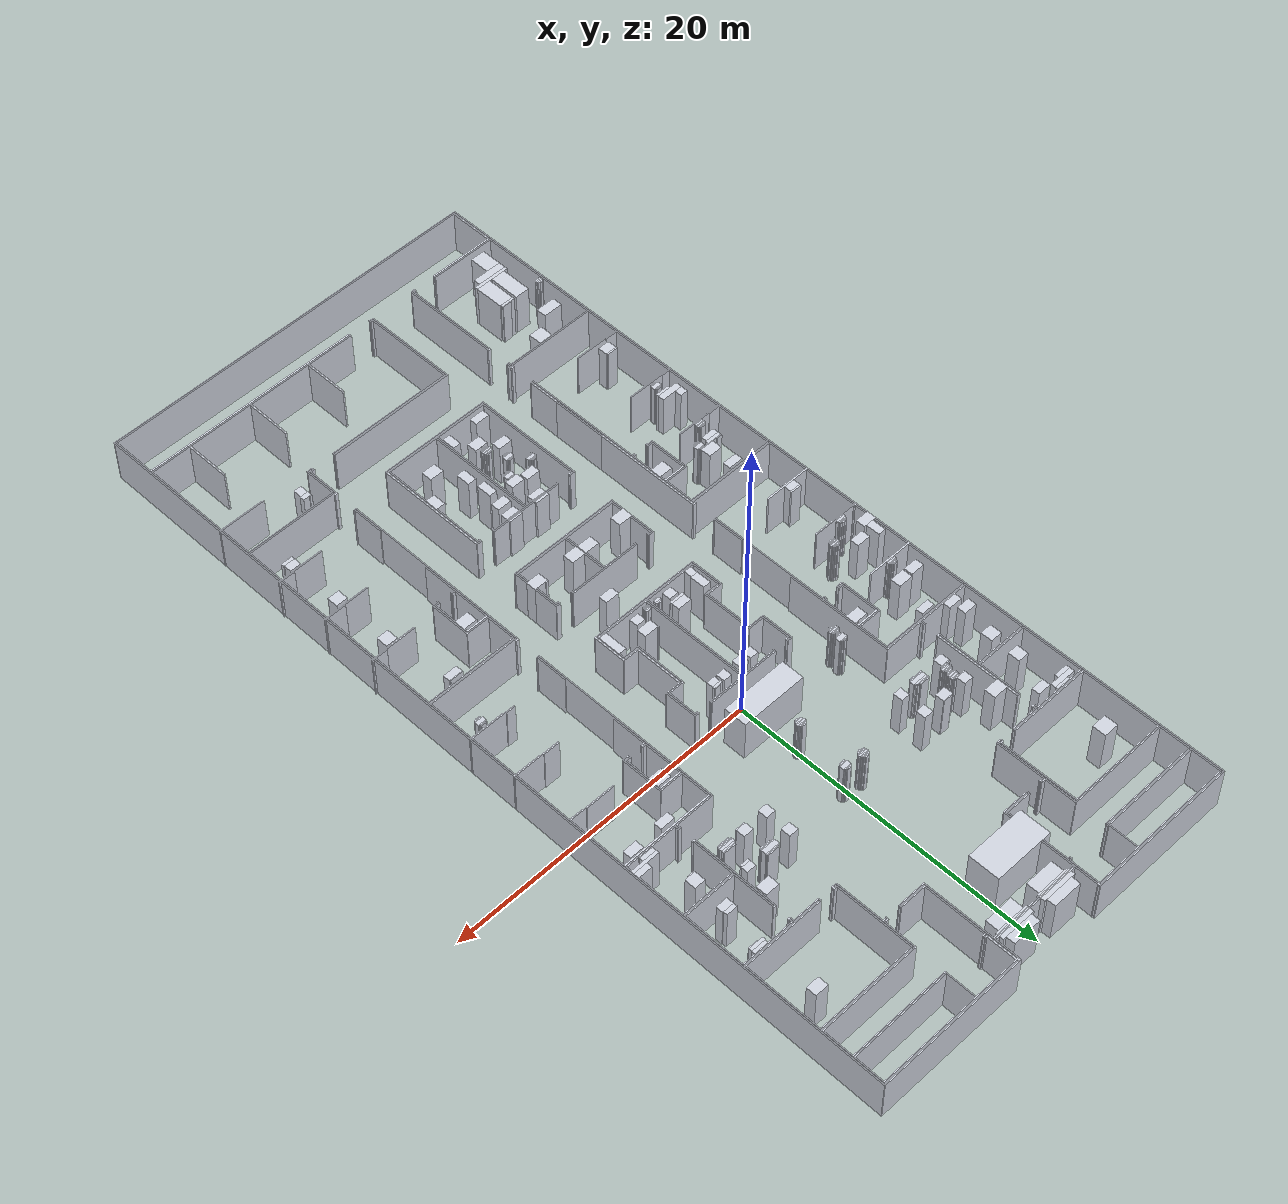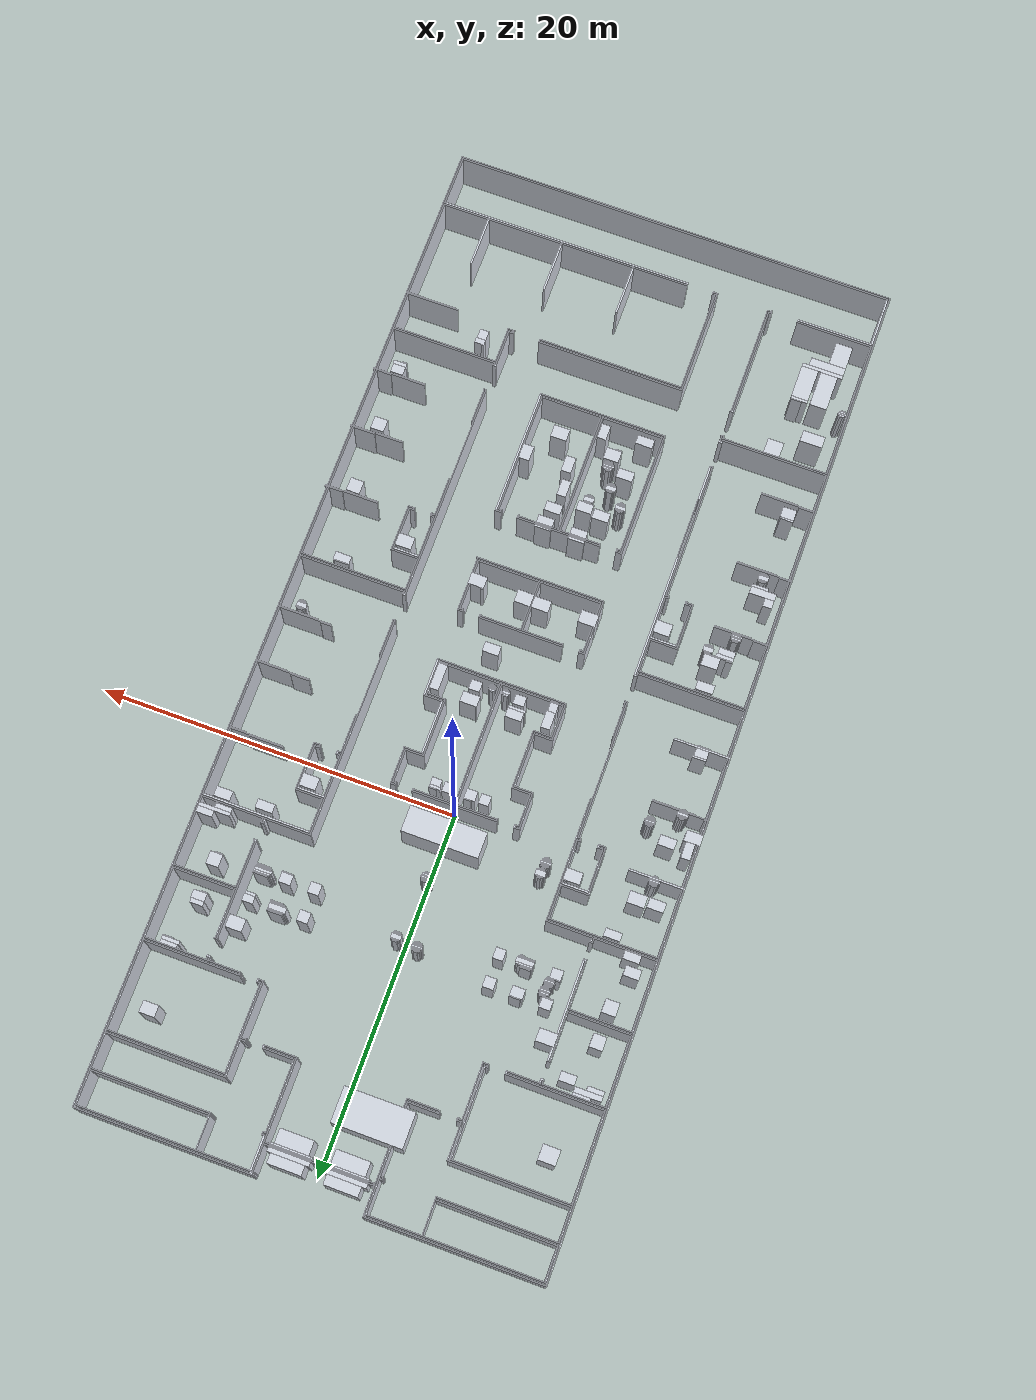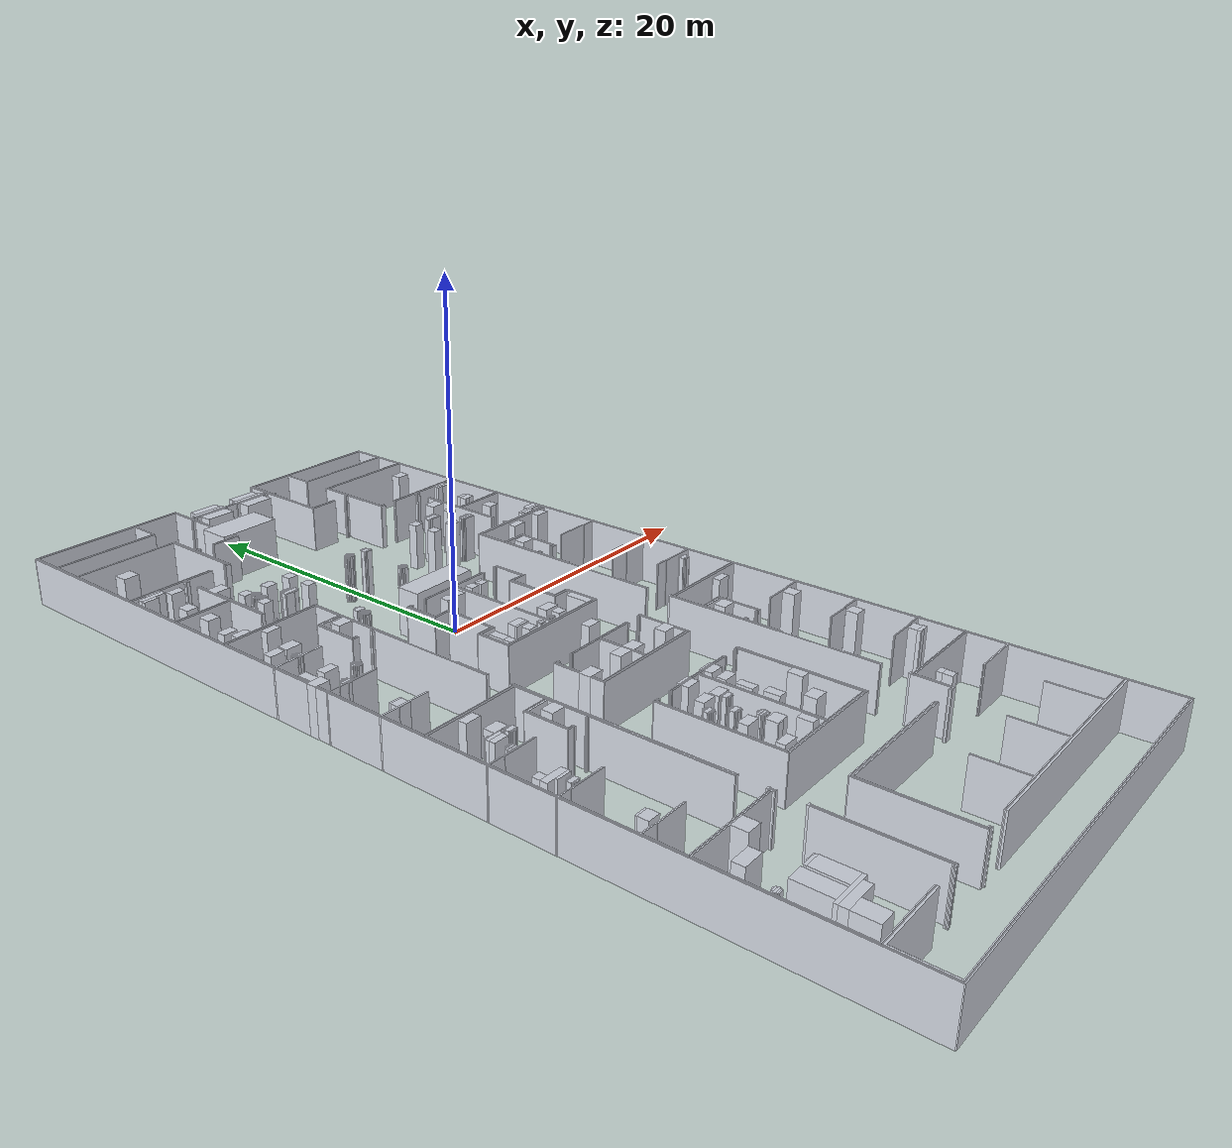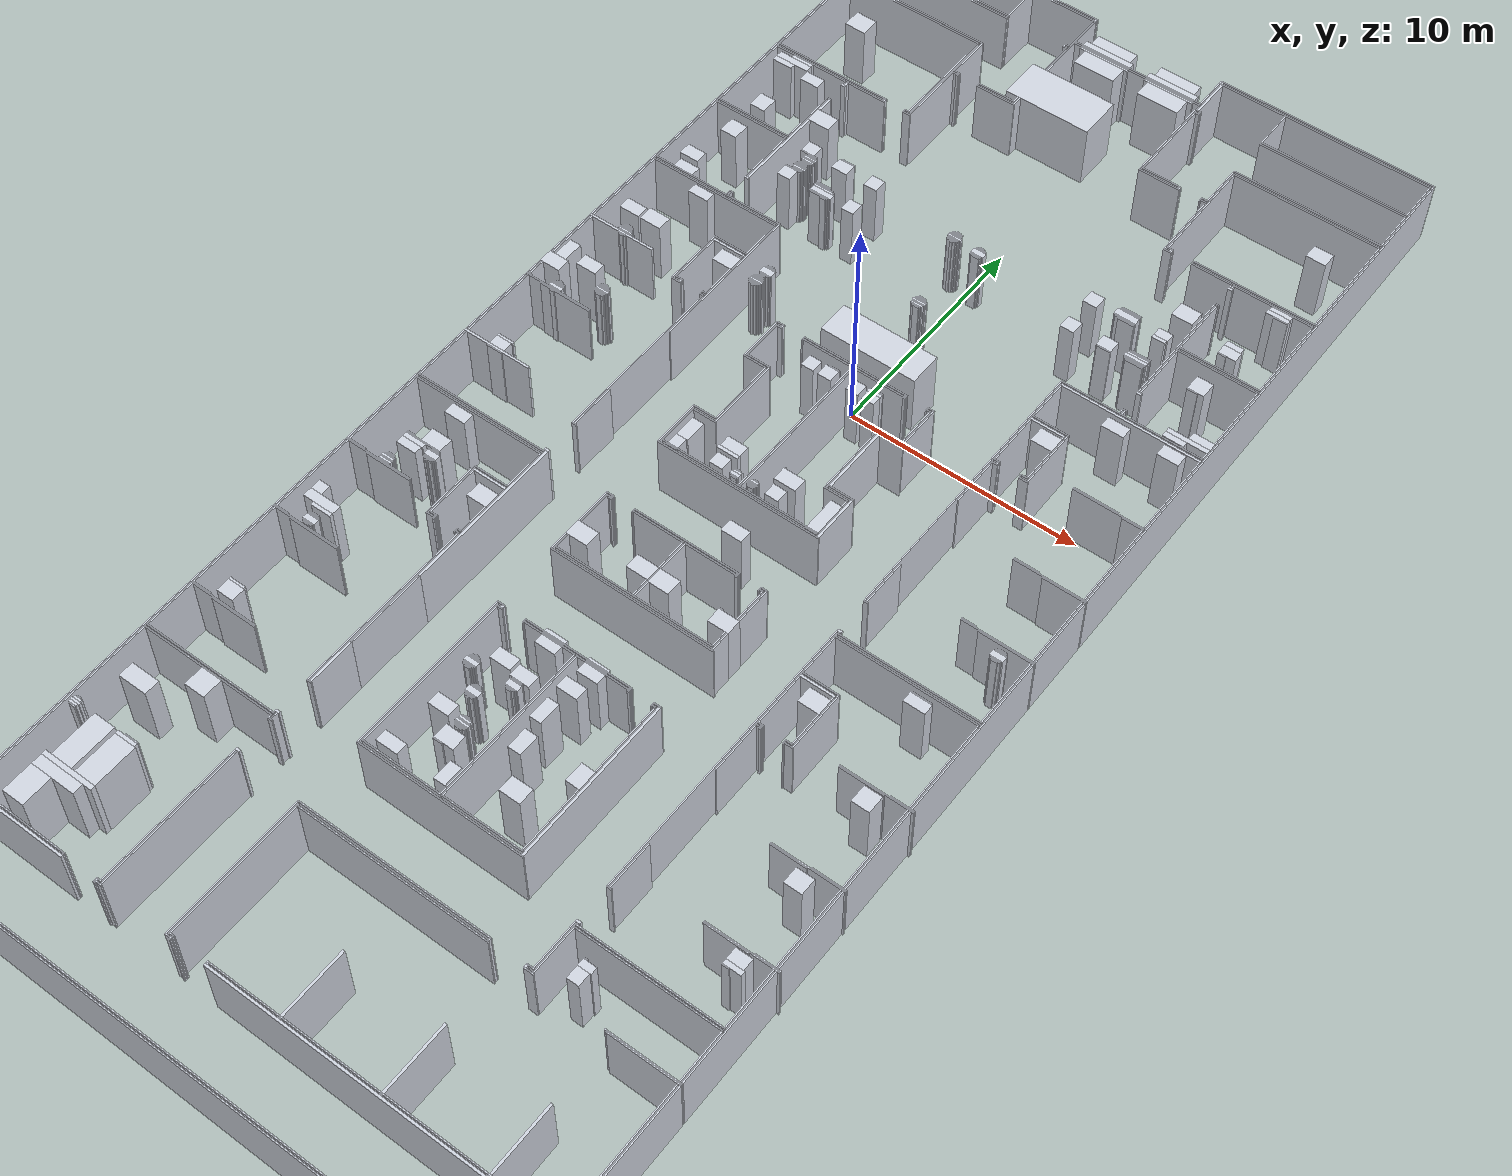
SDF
<?xml version="1.0"?>
  <sdf version="1.6">
    <model name="clinic_interior_walls">
      <static>true</static>
      <link name="link">
        <collision name="c_0">
  <pose>-7.77752 21.0535 1.425 0 0 0</pose>
  <geometry><box><size>9.65 0.05 2.85</size></box></geometry>
</collision>
<visual name="v_0">
  <pose>-7.77752 21.0535 1.425 0 0 0</pose>
  <geometry><box><size>9.65 0.05 2.85</size></box></geometry>
  <material>
    <ambient>0.82 0.84 0.88 1</ambient>
    <diffuse>0.82 0.84 0.88 1</diffuse>
  </material>
</visual>
<collision name="c_1">
  <pose>7.72248 21.0535 1.425 0 0 0</pose>
  <geometry><box><size>9.65 0.05 2.85</size></box></geometry>
</collision>
<visual name="v_1">
  <pose>7.72248 21.0535 1.425 0 0 0</pose>
  <geometry><box><size>9.65 0.05 2.85</size></box></geometry>
  <material>
    <ambient>0.82 0.84 0.88 1</ambient>
    <diffuse>0.82 0.84 0.88 1</diffuse>
  </material>
</visual>
<collision name="c_2">
  <pose>-3.00252 20.9785 1.425 0 0 0</pose>
  <geometry><box><size>0.1 0.1 2.85</size></box></geometry>
</collision>
<visual name="v_2">
  <pose>-3.00252 20.9785 1.425 0 0 0</pose>
  <geometry><box><size>0.1 0.1 2.85</size></box></geometry>
  <material>
    <ambient>0.82 0.84 0.88 1</ambient>
    <diffuse>0.82 0.84 0.88 1</diffuse>
  </material>
</visual>
<collision name="c_3">
  <pose>2.97248 20.9785 1.425 0 0 0</pose>
  <geometry><box><size>0.15 0.1 2.85</size></box></geometry>
</collision>
<visual name="v_3">
  <pose>2.97248 20.9785 1.425 0 0 0</pose>
  <geometry><box><size>0.15 0.1 2.85</size></box></geometry>
  <material>
    <ambient>0.82 0.84 0.88 1</ambient>
    <diffuse>0.82 0.84 0.88 1</diffuse>
  </material>
</visual>
<collision name="c_4">
  <pose>-7.72752 20.9035 1.425 0 0 0</pose>
  <geometry><box><size>9.55 0.05 2.85</size></box></geometry>
</collision>
<visual name="v_4">
  <pose>-7.72752 20.9035 1.425 0 0 0</pose>
  <geometry><box><size>9.55 0.05 2.85</size></box></geometry>
  <material>
    <ambient>0.82 0.84 0.88 1</ambient>
    <diffuse>0.82 0.84 0.88 1</diffuse>
  </material>
</visual>
<collision name="c_5">
  <pose>7.67248 20.9035 1.425 0 0 0</pose>
  <geometry><box><size>9.55 0.05 2.85</size></box></geometry>
</collision>
<visual name="v_5">
  <pose>7.67248 20.9035 1.425 0 0 0</pose>
  <geometry><box><size>9.55 0.05 2.85</size></box></geometry>
  <material>
    <ambient>0.82 0.84 0.88 1</ambient>
    <diffuse>0.82 0.84 0.88 1</diffuse>
  </material>
</visual>
<collision name="c_6">
  <pose>-1.47752 20.0035 1.425 0 0 0</pose>
  <geometry><box><size>1.85 0.55 2.85</size></box></geometry>
</collision>
<visual name="v_6">
  <pose>-1.47752 20.0035 1.425 0 0 0</pose>
  <geometry><box><size>1.85 0.55 2.85</size></box></geometry>
  <material>
    <ambient>0.82 0.84 0.88 1</ambient>
    <diffuse>0.82 0.84 0.88 1</diffuse>
  </material>
</visual>
<collision name="c_7">
  <pose>1.52248 20.0035 1.425 0 0 0</pose>
  <geometry><box><size>1.85 0.55 2.85</size></box></geometry>
</collision>
<visual name="v_7">
  <pose>1.52248 20.0035 1.425 0 0 0</pose>
  <geometry><box><size>1.85 0.55 2.85</size></box></geometry>
  <material>
    <ambient>0.82 0.84 0.88 1</ambient>
    <diffuse>0.82 0.84 0.88 1</diffuse>
  </material>
</visual>
<collision name="c_8">
  <pose>-2.97752 20.1785 1.425 0 0 0</pose>
  <geometry><box><size>0.05 1.4 2.85</size></box></geometry>
</collision>
<visual name="v_8">
  <pose>-2.97752 20.1785 1.425 0 0 0</pose>
  <geometry><box><size>0.05 1.4 2.85</size></box></geometry>
  <material>
    <ambient>0.82 0.84 0.88 1</ambient>
    <diffuse>0.82 0.84 0.88 1</diffuse>
  </material>
</visual>
<collision name="c_9">
  <pose>2.92248 20.1785 1.425 0 0 0</pose>
  <geometry><box><size>0.05 1.4 2.85</size></box></geometry>
</collision>
<visual name="v_9">
  <pose>2.92248 20.1785 1.425 0 0 0</pose>
  <geometry><box><size>0.05 1.4 2.85</size></box></geometry>
  <material>
    <ambient>0.82 0.84 0.88 1</ambient>
    <diffuse>0.82 0.84 0.88 1</diffuse>
  </material>
</visual>
<collision name="c_10">
  <pose>-1.52752 19.6035 1.425 0 0 0</pose>
  <geometry><box><size>2.25 0.25 2.85</size></box></geometry>
</collision>
<visual name="v_10">
  <pose>-1.52752 19.6035 1.425 0 0 0</pose>
  <geometry><box><size>2.25 0.25 2.85</size></box></geometry>
  <material>
    <ambient>0.82 0.84 0.88 1</ambient>
    <diffuse>0.82 0.84 0.88 1</diffuse>
  </material>
</visual>
<collision name="c_11">
  <pose>1.52248 19.6035 1.425 0 0 0</pose>
  <geometry><box><size>2.25 0.25 2.85</size></box></geometry>
</collision>
<visual name="v_11">
  <pose>1.52248 19.6035 1.425 0 0 0</pose>
  <geometry><box><size>2.25 0.25 2.85</size></box></geometry>
  <material>
    <ambient>0.82 0.84 0.88 1</ambient>
    <diffuse>0.82 0.84 0.88 1</diffuse>
  </material>
</visual>
<collision name="c_12">
  <pose>-0.0275166 19.4535 1.425 0 0 0</pose>
  <geometry><box><size>5.95 0.05 2.85</size></box></geometry>
</collision>
<visual name="v_12">
  <pose>-0.0275166 19.4535 1.425 0 0 0</pose>
  <geometry><box><size>5.95 0.05 2.85</size></box></geometry>
  <material>
    <ambient>0.82 0.84 0.88 1</ambient>
    <diffuse>0.82 0.84 0.88 1</diffuse>
  </material>
</visual>
<collision name="c_13">
  <pose>-2.95252 19.4035 1.425 0 0 0</pose>
  <geometry><box><size>0.1 0.05 2.85</size></box></geometry>
</collision>
<visual name="v_13">
  <pose>-2.95252 19.4035 1.425 0 0 0</pose>
  <geometry><box><size>0.1 0.05 2.85</size></box></geometry>
  <material>
    <ambient>0.82 0.84 0.88 1</ambient>
    <diffuse>0.82 0.84 0.88 1</diffuse>
  </material>
</visual>
<collision name="c_14">
  <pose>-1.52752 19.4035 1.425 0 0 0</pose>
  <geometry><box><size>2.25 0.05 2.85</size></box></geometry>
</collision>
<visual name="v_14">
  <pose>-1.52752 19.4035 1.425 0 0 0</pose>
  <geometry><box><size>2.25 0.05 2.85</size></box></geometry>
  <material>
    <ambient>0.82 0.84 0.88 1</ambient>
    <diffuse>0.82 0.84 0.88 1</diffuse>
  </material>
</visual>
<collision name="c_15">
  <pose>1.52248 19.4035 1.425 0 0 0</pose>
  <geometry><box><size>2.25 0.05 2.85</size></box></geometry>
</collision>
<visual name="v_15">
  <pose>1.52248 19.4035 1.425 0 0 0</pose>
  <geometry><box><size>2.25 0.05 2.85</size></box></geometry>
  <material>
    <ambient>0.82 0.84 0.88 1</ambient>
    <diffuse>0.82 0.84 0.88 1</diffuse>
  </material>
</visual>
<collision name="c_16">
  <pose>2.92248 19.4035 1.425 0 0 0</pose>
  <geometry><box><size>0.05 0.05 2.85</size></box></geometry>
</collision>
<visual name="v_16">
  <pose>2.92248 19.4035 1.425 0 0 0</pose>
  <geometry><box><size>0.05 0.05 2.85</size></box></geometry>
  <material>
    <ambient>0.82 0.84 0.88 1</ambient>
    <diffuse>0.82 0.84 0.88 1</diffuse>
  </material>
</visual>
<collision name="c_17">
  <pose>-0.0275166 19.3535 1.425 0 0 0</pose>
  <geometry><box><size>5.95 0.05 2.85</size></box></geometry>
</collision>
<visual name="v_17">
  <pose>-0.0275166 19.3535 1.425 0 0 0</pose>
  <geometry><box><size>5.95 0.05 2.85</size></box></geometry>
  <material>
    <ambient>0.82 0.84 0.88 1</ambient>
    <diffuse>0.82 0.84 0.88 1</diffuse>
  </material>
</visual>
<collision name="c_18">
  <pose>-1.52752 19.2785 1.425 0 0 0</pose>
  <geometry><box><size>2.25 0.1 2.85</size></box></geometry>
</collision>
<visual name="v_18">
  <pose>-1.52752 19.2785 1.425 0 0 0</pose>
  <geometry><box><size>2.25 0.1 2.85</size></box></geometry>
  <material>
    <ambient>0.82 0.84 0.88 1</ambient>
    <diffuse>0.82 0.84 0.88 1</diffuse>
  </material>
</visual>
<collision name="c_19">
  <pose>1.52248 19.2785 1.425 0 0 0</pose>
  <geometry><box><size>2.25 0.1 2.85</size></box></geometry>
</collision>
<visual name="v_19">
  <pose>1.52248 19.2785 1.425 0 0 0</pose>
  <geometry><box><size>2.25 0.1 2.85</size></box></geometry>
  <material>
    <ambient>0.82 0.84 0.88 1</ambient>
    <diffuse>0.82 0.84 0.88 1</diffuse>
  </material>
</visual>
<collision name="c_20">
  <pose>-12.4775 19.9785 1.425 0 0 0</pose>
  <geometry><box><size>0.05 1.8 2.85</size></box></geometry>
</collision>
<visual name="v_20">
  <pose>-12.4775 19.9785 1.425 0 0 0</pose>
  <geometry><box><size>0.05 1.8 2.85</size></box></geometry>
  <material>
    <ambient>0.82 0.84 0.88 1</ambient>
    <diffuse>0.82 0.84 0.88 1</diffuse>
  </material>
</visual>
<collision name="c_21">
  <pose>-6.02752 19.9785 1.425 0 0 0</pose>
  <geometry><box><size>0.05 1.8 2.85</size></box></geometry>
</collision>
<visual name="v_21">
  <pose>-6.02752 19.9785 1.425 0 0 0</pose>
  <geometry><box><size>0.05 1.8 2.85</size></box></geometry>
  <material>
    <ambient>0.82 0.84 0.88 1</ambient>
    <diffuse>0.82 0.84 0.88 1</diffuse>
  </material>
</visual>
<collision name="c_22">
  <pose>-3.07752 19.9785 1.425 0 0 0</pose>
  <geometry><box><size>0.05 1.8 2.85</size></box></geometry>
</collision>
<visual name="v_22">
  <pose>-3.07752 19.9785 1.425 0 0 0</pose>
  <geometry><box><size>0.05 1.8 2.85</size></box></geometry>
  <material>
    <ambient>0.82 0.84 0.88 1</ambient>
    <diffuse>0.82 0.84 0.88 1</diffuse>
  </material>
</visual>
<collision name="c_23">
  <pose>3.04748 19.9785 1.425 0 0 0</pose>
  <geometry><box><size>0.1 1.8 2.85</size></box></geometry>
</collision>
<visual name="v_23">
  <pose>3.04748 19.9785 1.425 0 0 0</pose>
  <geometry><box><size>0.1 1.8 2.85</size></box></geometry>
  <material>
    <ambient>0.82 0.84 0.88 1</ambient>
    <diffuse>0.82 0.84 0.88 1</diffuse>
  </material>
</visual>
<collision name="c_24">
  <pose>5.97248 19.9785 1.425 0 0 0</pose>
  <geometry><box><size>0.05 1.8 2.85</size></box></geometry>
</collision>
<visual name="v_24">
  <pose>5.97248 19.9785 1.425 0 0 0</pose>
  <geometry><box><size>0.05 1.8 2.85</size></box></geometry>
  <material>
    <ambient>0.82 0.84 0.88 1</ambient>
    <diffuse>0.82 0.84 0.88 1</diffuse>
  </material>
</visual>
<collision name="c_25">
  <pose>12.4225 19.9785 1.425 0 0 0</pose>
  <geometry><box><size>0.05 1.8 2.85</size></box></geometry>
</collision>
<visual name="v_25">
  <pose>12.4225 19.9785 1.425 0 0 0</pose>
  <geometry><box><size>0.05 1.8 2.85</size></box></geometry>
  <material>
    <ambient>0.82 0.84 0.88 1</ambient>
    <diffuse>0.82 0.84 0.88 1</diffuse>
  </material>
</visual>
<collision name="c_26">
  <pose>-9.25252 19.0535 1.425 0 0 0</pose>
  <geometry><box><size>6.5 0.05 2.85</size></box></geometry>
</collision>
<visual name="v_26">
  <pose>-9.25252 19.0535 1.425 0 0 0</pose>
  <geometry><box><size>6.5 0.05 2.85</size></box></geometry>
  <material>
    <ambient>0.82 0.84 0.88 1</ambient>
    <diffuse>0.82 0.84 0.88 1</diffuse>
  </material>
</visual>
<collision name="c_27">
  <pose>-3.15252 19.0535 1.425 0 0 0</pose>
  <geometry><box><size>0.2 0.05 2.85</size></box></geometry>
</collision>
<visual name="v_27">
  <pose>-3.15252 19.0535 1.425 0 0 0</pose>
  <geometry><box><size>0.2 0.05 2.85</size></box></geometry>
  <material>
    <ambient>0.82 0.84 0.88 1</ambient>
    <diffuse>0.82 0.84 0.88 1</diffuse>
  </material>
</visual>
<collision name="c_28">
  <pose>3.09748 19.0535 1.425 0 0 0</pose>
  <geometry><box><size>0.2 0.05 2.85</size></box></geometry>
</collision>
<visual name="v_28">
  <pose>3.09748 19.0535 1.425 0 0 0</pose>
  <geometry><box><size>0.2 0.05 2.85</size></box></geometry>
  <material>
    <ambient>0.82 0.84 0.88 1</ambient>
    <diffuse>0.82 0.84 0.88 1</diffuse>
  </material>
</visual>
<collision name="c_29">
  <pose>9.19748 19.0535 1.425 0 0 0</pose>
  <geometry><box><size>6.5 0.05 2.85</size></box></geometry>
</collision>
<visual name="v_29">
  <pose>9.19748 19.0535 1.425 0 0 0</pose>
  <geometry><box><size>6.5 0.05 2.85</size></box></geometry>
  <material>
    <ambient>0.82 0.84 0.88 1</ambient>
    <diffuse>0.82 0.84 0.88 1</diffuse>
  </material>
</visual>
<collision name="c_30">
  <pose>5.97248 19.0035 1.425 0 0 0</pose>
  <geometry><box><size>0.05 0.05 2.85</size></box></geometry>
</collision>
<visual name="v_30">
  <pose>5.97248 19.0035 1.425 0 0 0</pose>
  <geometry><box><size>0.05 0.05 2.85</size></box></geometry>
  <material>
    <ambient>0.82 0.84 0.88 1</ambient>
    <diffuse>0.82 0.84 0.88 1</diffuse>
  </material>
</visual>
<collision name="c_31">
  <pose>-6.02752 18.9785 1.425 0 0 0</pose>
  <geometry><box><size>0.05 0.1 2.85</size></box></geometry>
</collision>
<visual name="v_31">
  <pose>-6.02752 18.9785 1.425 0 0 0</pose>
  <geometry><box><size>0.05 0.1 2.85</size></box></geometry>
  <material>
    <ambient>0.82 0.84 0.88 1</ambient>
    <diffuse>0.82 0.84 0.88 1</diffuse>
  </material>
</visual>
<collision name="c_32">
  <pose>-3.22752 18.9785 1.425 0 0 0</pose>
  <geometry><box><size>0.05 0.1 2.85</size></box></geometry>
</collision>
<visual name="v_32">
  <pose>-3.22752 18.9785 1.425 0 0 0</pose>
  <geometry><box><size>0.05 0.1 2.85</size></box></geometry>
  <material>
    <ambient>0.82 0.84 0.88 1</ambient>
    <diffuse>0.82 0.84 0.88 1</diffuse>
  </material>
</visual>
<collision name="c_33">
  <pose>3.17248 18.9785 1.425 0 0 0</pose>
  <geometry><box><size>0.05 0.1 2.85</size></box></geometry>
</collision>
<visual name="v_33">
  <pose>3.17248 18.9785 1.425 0 0 0</pose>
  <geometry><box><size>0.05 0.1 2.85</size></box></geometry>
  <material>
    <ambient>0.82 0.84 0.88 1</ambient>
    <diffuse>0.82 0.84 0.88 1</diffuse>
  </material>
</visual>
<collision name="c_34">
  <pose>9.19748 18.9535 1.425 0 0 0</pose>
  <geometry><box><size>6.5 0.05 2.85</size></box></geometry>
</collision>
<visual name="v_34">
  <pose>9.19748 18.9535 1.425 0 0 0</pose>
  <geometry><box><size>6.5 0.05 2.85</size></box></geometry>
  <material>
    <ambient>0.82 0.84 0.88 1</ambient>
    <diffuse>0.82 0.84 0.88 1</diffuse>
  </material>
</visual>
<collision name="c_35">
  <pose>-9.25252 18.9035 1.425 0 0 0</pose>
  <geometry><box><size>6.5 0.05 2.85</size></box></geometry>
</collision>
<visual name="v_35">
  <pose>-9.25252 18.9035 1.425 0 0 0</pose>
  <geometry><box><size>6.5 0.05 2.85</size></box></geometry>
  <material>
    <ambient>0.82 0.84 0.88 1</ambient>
    <diffuse>0.82 0.84 0.88 1</diffuse>
  </material>
</visual>
<collision name="c_36">
  <pose>-3.15252 18.9035 1.425 0 0 0</pose>
  <geometry><box><size>0.2 0.05 2.85</size></box></geometry>
</collision>
<visual name="v_36">
  <pose>-3.15252 18.9035 1.425 0 0 0</pose>
  <geometry><box><size>0.2 0.05 2.85</size></box></geometry>
  <material>
    <ambient>0.82 0.84 0.88 1</ambient>
    <diffuse>0.82 0.84 0.88 1</diffuse>
  </material>
</visual>
<collision name="c_37">
  <pose>3.09748 18.9035 1.425 0 0 0</pose>
  <geometry><box><size>0.2 0.05 2.85</size></box></geometry>
</collision>
<visual name="v_37">
  <pose>3.09748 18.9035 1.425 0 0 0</pose>
  <geometry><box><size>0.2 0.05 2.85</size></box></geometry>
  <material>
    <ambient>0.82 0.84 0.88 1</ambient>
    <diffuse>0.82 0.84 0.88 1</diffuse>
  </material>
</visual>
<collision name="c_38">
  <pose>-1.47752 18.8285 1.425 0 0 0</pose>
  <geometry><box><size>1.85 0.8 2.85</size></box></geometry>
</collision>
<visual name="v_38">
  <pose>-1.47752 18.8285 1.425 0 0 0</pose>
  <geometry><box><size>1.85 0.8 2.85</size></box></geometry>
  <material>
    <ambient>0.82 0.84 0.88 1</ambient>
    <diffuse>0.82 0.84 0.88 1</diffuse>
  </material>
</visual>
<collision name="c_39">
  <pose>1.52248 18.8285 1.425 0 0 0</pose>
  <geometry><box><size>1.85 0.8 2.85</size></box></geometry>
</collision>
<visual name="v_39">
  <pose>1.52248 18.8285 1.425 0 0 0</pose>
  <geometry><box><size>1.85 0.8 2.85</size></box></geometry>
  <material>
    <ambient>0.82 0.84 0.88 1</ambient>
    <diffuse>0.82 0.84 0.88 1</diffuse>
  </material>
</visual>
<collision name="c_40">
  <pose>-2.97752 18.3285 1.425 0 0 0</pose>
  <geometry><box><size>0.05 2 2.85</size></box></geometry>
</collision>
<visual name="v_40">
  <pose>-2.97752 18.3285 1.425 0 0 0</pose>
  <geometry><box><size>0.05 2 2.85</size></box></geometry>
  <material>
    <ambient>0.82 0.84 0.88 1</ambient>
    <diffuse>0.82 0.84 0.88 1</diffuse>
  </material>
</visual>
<collision name="c_41">
  <pose>-3.07752 18.1035 1.425 0 0 0</pose>
  <geometry><box><size>0.05 1.55 2.85</size></box></geometry>
</collision>
<visual name="v_41">
  <pose>-3.07752 18.1035 1.425 0 0 0</pose>
  <geometry><box><size>0.05 1.55 2.85</size></box></geometry>
  <material>
    <ambient>0.82 0.84 0.88 1</ambient>
    <diffuse>0.82 0.84 0.88 1</diffuse>
  </material>
</visual>
<collision name="c_42">
  <pose>12.4225 18.0035 1.425 0 0 0</pose>
  <geometry><box><size>0.05 1.85 2.85</size></box></geometry>
</collision>
<visual name="v_42">
  <pose>12.4225 18.0035 1.425 0 0 0</pose>
  <geometry><box><size>0.05 1.85 2.85</size></box></geometry>
  <material>
    <ambient>0.82 0.84 0.88 1</ambient>
    <diffuse>0.82 0.84 0.88 1</diffuse>
  </material>
</visual>
<collision name="c_43">
  <pose>-12.4775 17.9785 1.425 0 0 0</pose>
  <geometry><box><size>0.05 1.8 2.85</size></box></geometry>
</collision>
<visual name="v_43">
  <pose>-12.4775 17.9785 1.425 0 0 0</pose>
  <geometry><box><size>0.05 1.8 2.85</size></box></geometry>
  <material>
    <ambient>0.82 0.84 0.88 1</ambient>
    <diffuse>0.82 0.84 0.88 1</diffuse>
  </material>
</visual>
<collision name="c_44">
  <pose>-9.20252 17.0535 1.425 0 0 0</pose>
  <geometry><box><size>6.6 0.05 2.85</size></box></geometry>
</collision>
<visual name="v_44">
  <pose>-9.20252 17.0535 1.425 0 0 0</pose>
  <geometry><box><size>6.6 0.05 2.85</size></box></geometry>
  <material>
    <ambient>0.82 0.84 0.88 1</ambient>
    <diffuse>0.82 0.84 0.88 1</diffuse>
  </material>
</visual>
<collision name="c_45">
  <pose>9.17248 17.0535 1.425 0 0 0</pose>
  <geometry><box><size>6.55 0.05 2.85</size></box></geometry>
</collision>
<visual name="v_45">
  <pose>9.17248 17.0535 1.425 0 0 0</pose>
  <geometry><box><size>6.55 0.05 2.85</size></box></geometry>
  <material>
    <ambient>0.82 0.84 0.88 1</ambient>
    <diffuse>0.82 0.84 0.88 1</diffuse>
  </material>
</visual>
<collision name="c_46">
  <pose>-9.27752 16.9535 1.425 0 0 0</pose>
  <geometry><box><size>6.45 0.05 2.85</size></box></geometry>
</collision>
<visual name="v_46">
  <pose>-9.27752 16.9535 1.425 0 0 0</pose>
  <geometry><box><size>6.45 0.05 2.85</size></box></geometry>
  <material>
    <ambient>0.82 0.84 0.88 1</ambient>
    <diffuse>0.82 0.84 0.88 1</diffuse>
  </material>
</visual>
<collision name="c_47">
  <pose>9.22248 16.9035 1.425 0 0 0</pose>
  <geometry><box><size>6.45 0.05 2.85</size></box></geometry>
</collision>
<visual name="v_47">
  <pose>9.22248 16.9035 1.425 0 0 0</pose>
  <geometry><box><size>6.45 0.05 2.85</size></box></geometry>
  <material>
    <ambient>0.82 0.84 0.88 1</ambient>
    <diffuse>0.82 0.84 0.88 1</diffuse>
  </material>
</visual>
<collision name="c_48">
  <pose>-1.72752 16.3535 1.425 0 0 0</pose>
  <geometry><box><size>3.85 1.95 2.85</size></box></geometry>
</collision>
<visual name="v_48">
  <pose>-1.72752 16.3535 1.425 0 0 0</pose>
  <geometry><box><size>3.85 1.95 2.85</size></box></geometry>
  <material>
    <ambient>0.82 0.84 0.88 1</ambient>
    <diffuse>0.82 0.84 0.88 1</diffuse>
  </material>
</visual>
<collision name="c_49">
  <pose>3.02248 16.9785 1.425 0 0 0</pose>
  <geometry><box><size>0.05 3.8 2.85</size></box></geometry>
</collision>
<visual name="v_49">
  <pose>3.02248 16.9785 1.425 0 0 0</pose>
  <geometry><box><size>0.05 3.8 2.85</size></box></geometry>
  <material>
    <ambient>0.82 0.84 0.88 1</ambient>
    <diffuse>0.82 0.84 0.88 1</diffuse>
  </material>
</visual>
<collision name="c_50">
  <pose>-5.92752 16.0535 1.425 0 0 0</pose>
  <geometry><box><size>0.05 1.95 2.85</size></box></geometry>
</collision>
<visual name="v_50">
  <pose>-5.92752 16.0535 1.425 0 0 0</pose>
  <geometry><box><size>0.05 1.95 2.85</size></box></geometry>
  <material>
    <ambient>0.82 0.84 0.88 1</ambient>
    <diffuse>0.82 0.84 0.88 1</diffuse>
  </material>
</visual>
<collision name="c_51">
  <pose>5.92248 16.0535 1.425 0 0 0</pose>
  <geometry><box><size>0.05 1.95 2.85</size></box></geometry>
</collision>
<visual name="v_51">
  <pose>5.92248 16.0535 1.425 0 0 0</pose>
  <geometry><box><size>0.05 1.95 2.85</size></box></geometry>
  <material>
    <ambient>0.82 0.84 0.88 1</ambient>
    <diffuse>0.82 0.84 0.88 1</diffuse>
  </material>
</visual>
<collision name="c_52">
  <pose>-3.07752 15.2285 1.425 0 0 0</pose>
  <geometry><box><size>0.05 0.3 2.85</size></box></geometry>
</collision>
<visual name="v_52">
  <pose>-3.07752 15.2285 1.425 0 0 0</pose>
  <geometry><box><size>0.05 0.3 2.85</size></box></geometry>
  <material>
    <ambient>0.82 0.84 0.88 1</ambient>
    <diffuse>0.82 0.84 0.88 1</diffuse>
  </material>
</visual>
<collision name="c_53">
  <pose>-5.80252 15.0535 1.425 0 0 0</pose>
  <geometry><box><size>0.3 0.05 2.85</size></box></geometry>
</collision>
<visual name="v_53">
  <pose>-5.80252 15.0535 1.425 0 0 0</pose>
  <geometry><box><size>0.3 0.05 2.85</size></box></geometry>
  <material>
    <ambient>0.82 0.84 0.88 1</ambient>
    <diffuse>0.82 0.84 0.88 1</diffuse>
  </material>
</visual>
<collision name="c_54">
  <pose>-3.90252 15.0535 1.425 0 0 0</pose>
  <geometry><box><size>1.7 0.05 2.85</size></box></geometry>
</collision>
<visual name="v_54">
  <pose>-3.90252 15.0535 1.425 0 0 0</pose>
  <geometry><box><size>1.7 0.05 2.85</size></box></geometry>
  <material>
    <ambient>0.82 0.84 0.88 1</ambient>
    <diffuse>0.82 0.84 0.88 1</diffuse>
  </material>
</visual>
<collision name="c_55">
  <pose>3.87248 15.0535 1.425 0 0 0</pose>
  <geometry><box><size>1.75 0.05 2.85</size></box></geometry>
</collision>
<visual name="v_55">
  <pose>3.87248 15.0535 1.425 0 0 0</pose>
  <geometry><box><size>1.75 0.05 2.85</size></box></geometry>
  <material>
    <ambient>0.82 0.84 0.88 1</ambient>
    <diffuse>0.82 0.84 0.88 1</diffuse>
  </material>
</visual>
<collision name="c_56">
  <pose>5.79748 15.0535 1.425 0 0 0</pose>
  <geometry><box><size>0.3 0.05 2.85</size></box></geometry>
</collision>
<visual name="v_56">
  <pose>5.79748 15.0535 1.425 0 0 0</pose>
  <geometry><box><size>0.3 0.05 2.85</size></box></geometry>
  <material>
    <ambient>0.82 0.84 0.88 1</ambient>
    <diffuse>0.82 0.84 0.88 1</diffuse>
  </material>
</visual>
<collision name="c_57">
  <pose>-5.70252 15.0035 1.425 0 0 0</pose>
  <geometry><box><size>0.1 0.05 2.85</size></box></geometry>
</collision>
<visual name="v_57">
  <pose>-5.70252 15.0035 1.425 0 0 0</pose>
  <geometry><box><size>0.1 0.05 2.85</size></box></geometry>
  <material>
    <ambient>0.82 0.84 0.88 1</ambient>
    <diffuse>0.82 0.84 0.88 1</diffuse>
  </material>
</visual>
<collision name="c_58">
  <pose>5.67248 15.0035 1.425 0 0 0</pose>
  <geometry><box><size>0.05 0.05 2.85</size></box></geometry>
</collision>
<visual name="v_58">
  <pose>5.67248 15.0035 1.425 0 0 0</pose>
  <geometry><box><size>0.05 0.05 2.85</size></box></geometry>
  <material>
    <ambient>0.82 0.84 0.88 1</ambient>
    <diffuse>0.82 0.84 0.88 1</diffuse>
  </material>
</visual>
<collision name="c_59">
  <pose>2.92248 17.1285 1.425 0 0 0</pose>
  <geometry><box><size>0.05 4.4 2.85</size></box></geometry>
</collision>
<visual name="v_59">
  <pose>2.92248 17.1285 1.425 0 0 0</pose>
  <geometry><box><size>0.05 4.4 2.85</size></box></geometry>
  <material>
    <ambient>0.82 0.84 0.88 1</ambient>
    <diffuse>0.82 0.84 0.88 1</diffuse>
  </material>
</visual>
<collision name="c_60">
  <pose>-2.97752 15.1535 1.425 0 0 0</pose>
  <geometry><box><size>0.05 0.45 2.85</size></box></geometry>
</collision>
<visual name="v_60">
  <pose>-2.97752 15.1535 1.425 0 0 0</pose>
  <geometry><box><size>0.05 0.45 2.85</size></box></geometry>
  <material>
    <ambient>0.82 0.84 0.88 1</ambient>
    <diffuse>0.82 0.84 0.88 1</diffuse>
  </material>
</visual>
<collision name="c_61">
  <pose>-4.72752 14.9785 1.425 0 0 0</pose>
  <geometry><box><size>0.05 0.1 2.85</size></box></geometry>
</collision>
<visual name="v_61">
  <pose>-4.72752 14.9785 1.425 0 0 0</pose>
  <geometry><box><size>0.05 0.1 2.85</size></box></geometry>
  <material>
    <ambient>0.82 0.84 0.88 1</ambient>
    <diffuse>0.82 0.84 0.88 1</diffuse>
  </material>
</visual>
<collision name="c_62">
  <pose>4.69748 14.9785 1.425 0 0 0</pose>
  <geometry><box><size>0.1 0.1 2.85</size></box></geometry>
</collision>
<visual name="v_62">
  <pose>4.69748 14.9785 1.425 0 0 0</pose>
  <geometry><box><size>0.1 0.1 2.85</size></box></geometry>
  <material>
    <ambient>0.82 0.84 0.88 1</ambient>
    <diffuse>0.82 0.84 0.88 1</diffuse>
  </material>
</visual>
<collision name="c_63">
  <pose>-5.80252 14.9535 1.425 0 0 0</pose>
  <geometry><box><size>0.3 0.05 2.85</size></box></geometry>
</collision>
<visual name="v_63">
  <pose>-5.80252 14.9535 1.425 0 0 0</pose>
  <geometry><box><size>0.3 0.05 2.85</size></box></geometry>
  <material>
    <ambient>0.82 0.84 0.88 1</ambient>
    <diffuse>0.82 0.84 0.88 1</diffuse>
  </material>
</visual>
<collision name="c_64">
  <pose>5.79748 14.9535 1.425 0 0 0</pose>
  <geometry><box><size>0.3 0.05 2.85</size></box></geometry>
</collision>
<visual name="v_64">
  <pose>5.79748 14.9535 1.425 0 0 0</pose>
  <geometry><box><size>0.3 0.05 2.85</size></box></geometry>
  <material>
    <ambient>0.82 0.84 0.88 1</ambient>
    <diffuse>0.82 0.84 0.88 1</diffuse>
  </material>
</visual>
<collision name="c_65">
  <pose>10.8225 15.2035 1.425 0 0 0</pose>
  <geometry><box><size>0.85 0.65 2.85</size></box></geometry>
</collision>
<visual name="v_65">
  <pose>10.8225 15.2035 1.425 0 0 0</pose>
  <geometry><box><size>0.85 0.65 2.85</size></box></geometry>
  <material>
    <ambient>0.82 0.84 0.88 1</ambient>
    <diffuse>0.82 0.84 0.88 1</diffuse>
  </material>
</visual>
<collision name="c_66">
  <pose>-5.70252 14.9035 1.425 0 0 0</pose>
  <geometry><box><size>0.1 0.05 2.85</size></box></geometry>
</collision>
<visual name="v_66">
  <pose>-5.70252 14.9035 1.425 0 0 0</pose>
  <geometry><box><size>0.1 0.05 2.85</size></box></geometry>
  <material>
    <ambient>0.82 0.84 0.88 1</ambient>
    <diffuse>0.82 0.84 0.88 1</diffuse>
  </material>
</visual>
<collision name="c_67">
  <pose>-3.85252 14.9035 1.425 0 0 0</pose>
  <geometry><box><size>1.8 0.05 2.85</size></box></geometry>
</collision>
<visual name="v_67">
  <pose>-3.85252 14.9035 1.425 0 0 0</pose>
  <geometry><box><size>1.8 0.05 2.85</size></box></geometry>
  <material>
    <ambient>0.82 0.84 0.88 1</ambient>
    <diffuse>0.82 0.84 0.88 1</diffuse>
  </material>
</visual>
<collision name="c_68">
  <pose>3.82248 14.9035 1.425 0 0 0</pose>
  <geometry><box><size>1.85 0.05 2.85</size></box></geometry>
</collision>
<visual name="v_68">
  <pose>3.82248 14.9035 1.425 0 0 0</pose>
  <geometry><box><size>1.85 0.05 2.85</size></box></geometry>
  <material>
    <ambient>0.82 0.84 0.88 1</ambient>
    <diffuse>0.82 0.84 0.88 1</diffuse>
  </material>
</visual>
<collision name="c_69">
  <pose>5.67248 14.9035 1.425 0 0 0</pose>
  <geometry><box><size>0.05 0.05 2.85</size></box></geometry>
</collision>
<visual name="v_69">
  <pose>5.67248 14.9035 1.425 0 0 0</pose>
  <geometry><box><size>0.05 0.05 2.85</size></box></geometry>
  <material>
    <ambient>0.82 0.84 0.88 1</ambient>
    <diffuse>0.82 0.84 0.88 1</diffuse>
  </material>
</visual>
<collision name="c_70">
  <pose>-10.5775 15.0535 1.425 0 0 0</pose>
  <geometry><box><size>0.95 0.85 2.85</size></box></geometry>
</collision>
<visual name="v_70">
  <pose>-10.5775 15.0535 1.425 0 0 0</pose>
  <geometry><box><size>0.95 0.85 2.85</size></box></geometry>
  <material>
    <ambient>0.82 0.84 0.88 1</ambient>
    <diffuse>0.82 0.84 0.88 1</diffuse>
  </material>
</visual>
<collision name="c_71">
  <pose>-12.4775 14.5035 1.425 0 0 0</pose>
  <geometry><box><size>0.05 4.85 2.85</size></box></geometry>
</collision>
<visual name="v_71">
  <pose>-12.4775 14.5035 1.425 0 0 0</pose>
  <geometry><box><size>0.05 4.85 2.85</size></box></geometry>
  <material>
    <ambient>0.82 0.84 0.88 1</ambient>
    <diffuse>0.82 0.84 0.88 1</diffuse>
  </material>
</visual>
<collision name="c_72">
  <pose>-6.07752 14.5035 1.425 0 0 0</pose>
  <geometry><box><size>0.05 4.85 2.85</size></box></geometry>
</collision>
<visual name="v_72">
  <pose>-6.07752 14.5035 1.425 0 0 0</pose>
  <geometry><box><size>0.05 4.85 2.85</size></box></geometry>
  <material>
    <ambient>0.82 0.84 0.88 1</ambient>
    <diffuse>0.82 0.84 0.88 1</diffuse>
  </material>
</visual>
<collision name="c_73">
  <pose>6.02248 14.4785 1.425 0 0 0</pose>
  <geometry><box><size>0.05 4.8 2.85</size></box></geometry>
</collision>
<visual name="v_73">
  <pose>6.02248 14.4785 1.425 0 0 0</pose>
  <geometry><box><size>0.05 4.8 2.85</size></box></geometry>
  <material>
    <ambient>0.82 0.84 0.88 1</ambient>
    <diffuse>0.82 0.84 0.88 1</diffuse>
  </material>
</visual>
<collision name="c_74">
  <pose>12.4225 14.4785 1.425 0 0 0</pose>
  <geometry><box><size>0.05 4.8 2.85</size></box></geometry>
</collision>
<visual name="v_74">
  <pose>12.4225 14.4785 1.425 0 0 0</pose>
  <geometry><box><size>0.05 4.8 2.85</size></box></geometry>
  <material>
    <ambient>0.82 0.84 0.88 1</ambient>
    <diffuse>0.82 0.84 0.88 1</diffuse>
  </material>
</visual>
<collision name="c_75">
  <pose>-9.82752 12.0535 1.425 0 0 0</pose>
  <geometry><box><size>5.35 0.05 2.85</size></box></geometry>
</collision>
<visual name="v_75">
  <pose>-9.82752 12.0535 1.425 0 0 0</pose>
  <geometry><box><size>5.35 0.05 2.85</size></box></geometry>
  <material>
    <ambient>0.82 0.84 0.88 1</ambient>
    <diffuse>0.82 0.84 0.88 1</diffuse>
  </material>
</visual>
<collision name="c_76">
  <pose>-6.15252 12.0535 1.425 0 0 0</pose>
  <geometry><box><size>0.2 0.05 2.85</size></box></geometry>
</collision>
<visual name="v_76">
  <pose>-6.15252 12.0535 1.425 0 0 0</pose>
  <geometry><box><size>0.2 0.05 2.85</size></box></geometry>
  <material>
    <ambient>0.82 0.84 0.88 1</ambient>
    <diffuse>0.82 0.84 0.88 1</diffuse>
  </material>
</visual>
<collision name="c_77">
  <pose>6.12248 12.0535 1.425 0 0 0</pose>
  <geometry><box><size>0.25 0.05 2.85</size></box></geometry>
</collision>
<visual name="v_77">
  <pose>6.12248 12.0535 1.425 0 0 0</pose>
  <geometry><box><size>0.25 0.05 2.85</size></box></geometry>
  <material>
    <ambient>0.82 0.84 0.88 1</ambient>
    <diffuse>0.82 0.84 0.88 1</diffuse>
  </material>
</visual>
<collision name="c_78">
  <pose>9.79748 12.0535 1.425 0 0 0</pose>
  <geometry><box><size>5.3 0.05 2.85</size></box></geometry>
</collision>
<visual name="v_78">
  <pose>9.79748 12.0535 1.425 0 0 0</pose>
  <geometry><box><size>5.3 0.05 2.85</size></box></geometry>
  <material>
    <ambient>0.82 0.84 0.88 1</ambient>
    <diffuse>0.82 0.84 0.88 1</diffuse>
  </material>
</visual>
<collision name="c_79">
  <pose>-5.92752 13.4285 1.425 0 0 0</pose>
  <geometry><box><size>0.05 3 2.85</size></box></geometry>
</collision>
<visual name="v_79">
  <pose>-5.92752 13.4285 1.425 0 0 0</pose>
  <geometry><box><size>0.05 3 2.85</size></box></geometry>
  <material>
    <ambient>0.82 0.84 0.88 1</ambient>
    <diffuse>0.82 0.84 0.88 1</diffuse>
  </material>
</visual>
<collision name="c_80">
  <pose>5.92248 13.4285 1.425 0 0 0</pose>
  <geometry><box><size>0.05 3 2.85</size></box></geometry>
</collision>
<visual name="v_80">
  <pose>5.92248 13.4285 1.425 0 0 0</pose>
  <geometry><box><size>0.05 3 2.85</size></box></geometry>
  <material>
    <ambient>0.82 0.84 0.88 1</ambient>
    <diffuse>0.82 0.84 0.88 1</diffuse>
  </material>
</visual>
<collision name="c_81">
  <pose>-7.20252 11.9785 1.425 0 0 0</pose>
  <geometry><box><size>0.1 0.1 2.85</size></box></geometry>
</collision>
<visual name="v_81">
  <pose>-7.20252 11.9785 1.425 0 0 0</pose>
  <geometry><box><size>0.1 0.1 2.85</size></box></geometry>
  <material>
    <ambient>0.82 0.84 0.88 1</ambient>
    <diffuse>0.82 0.84 0.88 1</diffuse>
  </material>
</visual>
<collision name="c_82">
  <pose>-6.22752 11.9785 1.425 0 0 0</pose>
  <geometry><box><size>0.05 0.1 2.85</size></box></geometry>
</collision>
<visual name="v_82">
  <pose>-6.22752 11.9785 1.425 0 0 0</pose>
  <geometry><box><size>0.05 0.1 2.85</size></box></geometry>
  <material>
    <ambient>0.82 0.84 0.88 1</ambient>
    <diffuse>0.82 0.84 0.88 1</diffuse>
  </material>
</visual>
<collision name="c_83">
  <pose>6.19748 11.9785 1.425 0 0 0</pose>
  <geometry><box><size>0.1 0.1 2.85</size></box></geometry>
</collision>
<visual name="v_83">
  <pose>6.19748 11.9785 1.425 0 0 0</pose>
  <geometry><box><size>0.1 0.1 2.85</size></box></geometry>
  <material>
    <ambient>0.82 0.84 0.88 1</ambient>
    <diffuse>0.82 0.84 0.88 1</diffuse>
  </material>
</visual>
<collision name="c_84">
  <pose>7.17248 11.9785 1.425 0 0 0</pose>
  <geometry><box><size>0.05 0.1 2.85</size></box></geometry>
</collision>
<visual name="v_84">
  <pose>7.17248 11.9785 1.425 0 0 0</pose>
  <geometry><box><size>0.05 0.1 2.85</size></box></geometry>
  <material>
    <ambient>0.82 0.84 0.88 1</ambient>
    <diffuse>0.82 0.84 0.88 1</diffuse>
  </material>
</visual>
<collision name="c_85">
  <pose>-10.7775 11.9035 1.425 0 0 0</pose>
  <geometry><box><size>3.45 0.05 2.85</size></box></geometry>
</collision>
<visual name="v_85">
  <pose>-10.7775 11.9035 1.425 0 0 0</pose>
  <geometry><box><size>3.45 0.05 2.85</size></box></geometry>
  <material>
    <ambient>0.82 0.84 0.88 1</ambient>
    <diffuse>0.82 0.84 0.88 1</diffuse>
  </material>
</visual>
<collision name="c_86">
  <pose>-8.07752 11.9035 1.425 0 0 0</pose>
  <geometry><box><size>1.85 0.05 2.85</size></box></geometry>
</collision>
<visual name="v_86">
  <pose>-8.07752 11.9035 1.425 0 0 0</pose>
  <geometry><box><size>1.85 0.05 2.85</size></box></geometry>
  <material>
    <ambient>0.82 0.84 0.88 1</ambient>
    <diffuse>0.82 0.84 0.88 1</diffuse>
  </material>
</visual>
<collision name="c_87">
  <pose>-6.07752 11.9035 1.425 0 0 0</pose>
  <geometry><box><size>0.35 0.05 2.85</size></box></geometry>
</collision>
<visual name="v_87">
  <pose>-6.07752 11.9035 1.425 0 0 0</pose>
  <geometry><box><size>0.35 0.05 2.85</size></box></geometry>
  <material>
    <ambient>0.82 0.84 0.88 1</ambient>
    <diffuse>0.82 0.84 0.88 1</diffuse>
  </material>
</visual>
<collision name="c_88">
  <pose>6.07248 11.9035 1.425 0 0 0</pose>
  <geometry><box><size>0.35 0.05 2.85</size></box></geometry>
</collision>
<visual name="v_88">
  <pose>6.07248 11.9035 1.425 0 0 0</pose>
  <geometry><box><size>0.35 0.05 2.85</size></box></geometry>
  <material>
    <ambient>0.82 0.84 0.88 1</ambient>
    <diffuse>0.82 0.84 0.88 1</diffuse>
  </material>
</visual>
<collision name="c_89">
  <pose>8.04748 11.9035 1.425 0 0 0</pose>
  <geometry><box><size>1.8 0.05 2.85</size></box></geometry>
</collision>
<visual name="v_89">
  <pose>8.04748 11.9035 1.425 0 0 0</pose>
  <geometry><box><size>1.8 0.05 2.85</size></box></geometry>
  <material>
    <ambient>0.82 0.84 0.88 1</ambient>
    <diffuse>0.82 0.84 0.88 1</diffuse>
  </material>
</visual>
<collision name="c_90">
  <pose>10.7225 11.9035 1.425 0 0 0</pose>
  <geometry><box><size>3.45 0.05 2.85</size></box></geometry>
</collision>
<visual name="v_90">
  <pose>10.7225 11.9035 1.425 0 0 0</pose>
  <geometry><box><size>3.45 0.05 2.85</size></box></geometry>
  <material>
    <ambient>0.82 0.84 0.88 1</ambient>
    <diffuse>0.82 0.84 0.88 1</diffuse>
  </material>
</visual>
<collision name="c_91">
  <pose>-11.1275 11.8035 1.425 0 0 0</pose>
  <geometry><box><size>0.95 0.15 2.85</size></box></geometry>
</collision>
<visual name="v_91">
  <pose>-11.1275 11.8035 1.425 0 0 0</pose>
  <geometry><box><size>0.95 0.15 2.85</size></box></geometry>
  <material>
    <ambient>0.82 0.84 0.88 1</ambient>
    <diffuse>0.82 0.84 0.88 1</diffuse>
  </material>
</visual>
<collision name="c_92">
  <pose>-9.07752 11.8035 1.425 0 0 0</pose>
  <geometry><box><size>0.05 0.15 2.85</size></box></geometry>
</collision>
<visual name="v_92">
  <pose>-9.07752 11.8035 1.425 0 0 0</pose>
  <geometry><box><size>0.05 0.15 2.85</size></box></geometry>
  <material>
    <ambient>0.82 0.84 0.88 1</ambient>
    <diffuse>0.82 0.84 0.88 1</diffuse>
  </material>
</visual>
<collision name="c_93">
  <pose>-8.95252 11.8035 1.425 0 0 0</pose>
  <geometry><box><size>0.1 0.15 2.85</size></box></geometry>
</collision>
<visual name="v_93">
  <pose>-8.95252 11.8035 1.425 0 0 0</pose>
  <geometry><box><size>0.1 0.15 2.85</size></box></geometry>
  <material>
    <ambient>0.82 0.84 0.88 1</ambient>
    <diffuse>0.82 0.84 0.88 1</diffuse>
  </material>
</visual>
<collision name="c_94">
  <pose>8.92248 11.8035 1.425 0 0 0</pose>
  <geometry><box><size>0.05 0.15 2.85</size></box></geometry>
</collision>
<visual name="v_94">
  <pose>8.92248 11.8035 1.425 0 0 0</pose>
  <geometry><box><size>0.05 0.15 2.85</size></box></geometry>
  <material>
    <ambient>0.82 0.84 0.88 1</ambient>
    <diffuse>0.82 0.84 0.88 1</diffuse>
  </material>
</visual>
<collision name="c_95">
  <pose>9.02248 11.8035 1.425 0 0 0</pose>
  <geometry><box><size>0.05 0.15 2.85</size></box></geometry>
</collision>
<visual name="v_95">
  <pose>9.02248 11.8035 1.425 0 0 0</pose>
  <geometry><box><size>0.05 0.15 2.85</size></box></geometry>
  <material>
    <ambient>0.82 0.84 0.88 1</ambient>
    <diffuse>0.82 0.84 0.88 1</diffuse>
  </material>
</visual>
<collision name="c_96">
  <pose>11.1475 11.7785 1.425 0 0 0</pose>
  <geometry><box><size>0.9 0.2 2.85</size></box></geometry>
</collision>
<visual name="v_96">
  <pose>11.1475 11.7785 1.425 0 0 0</pose>
  <geometry><box><size>0.9 0.2 2.85</size></box></geometry>
  <material>
    <ambient>0.82 0.84 0.88 1</ambient>
    <diffuse>0.82 0.84 0.88 1</diffuse>
  </material>
</visual>
<collision name="c_97">
  <pose>-9.00252 11.6785 1.425 0 0 0</pose>
  <geometry><box><size>0.2 0.1 2.85</size></box></geometry>
</collision>
<visual name="v_97">
  <pose>-9.00252 11.6785 1.425 0 0 0</pose>
  <geometry><box><size>0.2 0.1 2.85</size></box></geometry>
  <material>
    <ambient>0.82 0.84 0.88 1</ambient>
    <diffuse>0.82 0.84 0.88 1</diffuse>
  </material>
</visual>
<collision name="c_98">
  <pose>8.99748 11.6785 1.425 0 0 0</pose>
  <geometry><box><size>0.2 0.1 2.85</size></box></geometry>
</collision>
<visual name="v_98">
  <pose>8.99748 11.6785 1.425 0 0 0</pose>
  <geometry><box><size>0.2 0.1 2.85</size></box></geometry>
  <material>
    <ambient>0.82 0.84 0.88 1</ambient>
    <diffuse>0.82 0.84 0.88 1</diffuse>
  </material>
</visual>
<collision name="c_99">
  <pose>11.1225 11.5785 1.425 0 0 0</pose>
  <geometry><box><size>0.95 0.2 2.85</size></box></geometry>
</collision>
<visual name="v_99">
  <pose>11.1225 11.5785 1.425 0 0 0</pose>
  <geometry><box><size>0.95 0.2 2.85</size></box></geometry>
  <material>
    <ambient>0.82 0.84 0.88 1</ambient>
    <diffuse>0.82 0.84 0.88 1</diffuse>
  </material>
</visual>
<collision name="c_100">
  <pose>-11.4025 11.5785 1.425 0 0 0</pose>
  <geometry><box><size>1.5 0.3 2.85</size></box></geometry>
</collision>
<visual name="v_100">
  <pose>-11.4025 11.5785 1.425 0 0 0</pose>
  <geometry><box><size>1.5 0.3 2.85</size></box></geometry>
  <material>
    <ambient>0.82 0.84 0.88 1</ambient>
    <diffuse>0.82 0.84 0.88 1</diffuse>
  </material>
</visual>
<collision name="c_101">
  <pose>11.2975 11.4535 1.425 0 0 0</pose>
  <geometry><box><size>0.6 0.05 2.85</size></box></geometry>
</collision>
<visual name="v_101">
  <pose>11.2975 11.4535 1.425 0 0 0</pose>
  <geometry><box><size>0.6 0.05 2.85</size></box></geometry>
  <material>
    <ambient>0.82 0.84 0.88 1</ambient>
    <diffuse>0.82 0.84 0.88 1</diffuse>
  </material>
</visual>
<collision name="c_102">
  <pose>-11.7025 11.3035 1.425 0 0 0</pose>
  <geometry><box><size>0.9 0.25 2.85</size></box></geometry>
</collision>
<visual name="v_102">
  <pose>-11.7025 11.3035 1.425 0 0 0</pose>
  <geometry><box><size>0.9 0.25 2.85</size></box></geometry>
  <material>
    <ambient>0.82 0.84 0.88 1</ambient>
    <diffuse>0.82 0.84 0.88 1</diffuse>
  </material>
</visual>
<collision name="c_103">
  <pose>-10.1775 11.1785 1.425 0 0 0</pose>
  <geometry><box><size>0.85 0.5 2.85</size></box></geometry>
</collision>
<visual name="v_103">
  <pose>-10.1775 11.1785 1.425 0 0 0</pose>
  <geometry><box><size>0.85 0.5 2.85</size></box></geometry>
  <material>
    <ambient>0.82 0.84 0.88 1</ambient>
    <diffuse>0.82 0.84 0.88 1</diffuse>
  </material>
</visual>
<collision name="c_104">
  <pose>-9.00252 10.7035 1.425 0 0 0</pose>
  <geometry><box><size>0.2 0.05 2.85</size></box></geometry>
</collision>
<visual name="v_104">
  <pose>-9.00252 10.7035 1.425 0 0 0</pose>
  <geometry><box><size>0.2 0.05 2.85</size></box></geometry>
  <material>
    <ambient>0.82 0.84 0.88 1</ambient>
    <diffuse>0.82 0.84 0.88 1</diffuse>
  </material>
</visual>
<collision name="c_105">
  <pose>8.99748 10.7035 1.425 0 0 0</pose>
  <geometry><box><size>0.2 0.05 2.85</size></box></geometry>
</collision>
<visual name="v_105">
  <pose>8.99748 10.7035 1.425 0 0 0</pose>
  <geometry><box><size>0.2 0.05 2.85</size></box></geometry>
  <material>
    <ambient>0.82 0.84 0.88 1</ambient>
    <diffuse>0.82 0.84 0.88 1</diffuse>
  </material>
</visual>
<collision name="c_106">
  <pose>-8.95252 10.3285 1.425 0 0 0</pose>
  <geometry><box><size>0.1 0.7 2.85</size></box></geometry>
</collision>
<visual name="v_106">
  <pose>-8.95252 10.3285 1.425 0 0 0</pose>
  <geometry><box><size>0.1 0.7 2.85</size></box></geometry>
  <material>
    <ambient>0.82 0.84 0.88 1</ambient>
    <diffuse>0.82 0.84 0.88 1</diffuse>
  </material>
</visual>
<collision name="c_107">
  <pose>-8.50252 9.62852 1.425 0 0 0</pose>
  <geometry><box><size>1 0.7 2.85</size></box></geometry>
</collision>
<visual name="v_107">
  <pose>-8.50252 9.62852 1.425 0 0 0</pose>
  <geometry><box><size>1 0.7 2.85</size></box></geometry>
  <material>
    <ambient>0.82 0.84 0.88 1</ambient>
    <diffuse>0.82 0.84 0.88 1</diffuse>
  </material>
</visual>
<collision name="c_108">
  <pose>8.34748 9.62852 1.425 0 0 0</pose>
  <geometry><box><size>0.9 0.7 2.85</size></box></geometry>
</collision>
<visual name="v_108">
  <pose>8.34748 9.62852 1.425 0 0 0</pose>
  <geometry><box><size>0.9 0.7 2.85</size></box></geometry>
  <material>
    <ambient>0.82 0.84 0.88 1</ambient>
    <diffuse>0.82 0.84 0.88 1</diffuse>
  </material>
</visual>
<collision name="c_109">
  <pose>10.5975 9.30352 1.425 0 0 0</pose>
  <geometry><box><size>0.7 0.25 2.85</size></box></geometry>
</collision>
<visual name="v_109">
  <pose>10.5975 9.30352 1.425 0 0 0</pose>
  <geometry><box><size>0.7 0.25 2.85</size></box></geometry>
  <material>
    <ambient>0.82 0.84 0.88 1</ambient>
    <diffuse>0.82 0.84 0.88 1</diffuse>
  </material>
</visual>
<collision name="c_110">
  <pose>10.6225 8.95352 1.425 0 0 0</pose>
  <geometry><box><size>0.75 0.45 2.85</size></box></geometry>
</collision>
<visual name="v_110">
  <pose>10.6225 8.95352 1.425 0 0 0</pose>
  <geometry><box><size>0.75 0.45 2.85</size></box></geometry>
  <material>
    <ambient>0.82 0.84 0.88 1</ambient>
    <diffuse>0.82 0.84 0.88 1</diffuse>
  </material>
</visual>
<collision name="c_111">
  <pose>10.4225 8.70352 1.425 0 0 0</pose>
  <geometry><box><size>0.35 0.05 2.85</size></box></geometry>
</collision>
<visual name="v_111">
  <pose>10.4225 8.70352 1.425 0 0 0</pose>
  <geometry><box><size>0.35 0.05 2.85</size></box></geometry>
  <material>
    <ambient>0.82 0.84 0.88 1</ambient>
    <diffuse>0.82 0.84 0.88 1</diffuse>
  </material>
</visual>
<collision name="c_112">
  <pose>-11.0025 8.95352 1.425 0 0 0</pose>
  <geometry><box><size>0.7 0.75 2.85</size></box></geometry>
</collision>
<visual name="v_112">
  <pose>-11.0025 8.95352 1.425 0 0 0</pose>
  <geometry><box><size>0.7 0.75 2.85</size></box></geometry>
  <material>
    <ambient>0.82 0.84 0.88 1</ambient>
    <diffuse>0.82 0.84 0.88 1</diffuse>
  </material>
</visual>
<collision name="c_113">
  <pose>6.69748 8.45352 1.425 0 0 0</pose>
  <geometry><box><size>0.8 0.05 2.85</size></box></geometry>
</collision>
<visual name="v_113">
  <pose>6.69748 8.45352 1.425 0 0 0</pose>
  <geometry><box><size>0.8 0.05 2.85</size></box></geometry>
  <material>
    <ambient>0.82 0.84 0.88 1</ambient>
    <diffuse>0.82 0.84 0.88 1</diffuse>
  </material>
</visual>
<collision name="c_114">
  <pose>6.67248 8.40352 1.425 0 0 0</pose>
  <geometry><box><size>0.85 0.05 2.85</size></box></geometry>
</collision>
<visual name="v_114">
  <pose>6.67248 8.40352 1.425 0 0 0</pose>
  <geometry><box><size>0.85 0.05 2.85</size></box></geometry>
  <material>
    <ambient>0.82 0.84 0.88 1</ambient>
    <diffuse>0.82 0.84 0.88 1</diffuse>
  </material>
</visual>
<collision name="c_115">
  <pose>6.64748 8.35352 1.425 0 0 0</pose>
  <geometry><box><size>0.9 0.05 2.85</size></box></geometry>
</collision>
<visual name="v_115">
  <pose>6.64748 8.35352 1.425 0 0 0</pose>
  <geometry><box><size>0.9 0.05 2.85</size></box></geometry>
  <material>
    <ambient>0.82 0.84 0.88 1</ambient>
    <diffuse>0.82 0.84 0.88 1</diffuse>
  </material>
</visual>
<collision name="c_116">
  <pose>-6.30252 8.30352 1.425 0 0 0</pose>
  <geometry><box><size>0.6 0.05 2.85</size></box></geometry>
</collision>
<visual name="v_116">
  <pose>-6.30252 8.30352 1.425 0 0 0</pose>
  <geometry><box><size>0.6 0.05 2.85</size></box></geometry>
  <material>
    <ambient>0.82 0.84 0.88 1</ambient>
    <diffuse>0.82 0.84 0.88 1</diffuse>
  </material>
</visual>
<collision name="c_117">
  <pose>-12.4775 9.97852 1.425 0 0 0</pose>
  <geometry><box><size>0.05 3.8 2.85</size></box></geometry>
</collision>
<visual name="v_117">
  <pose>-12.4775 9.97852 1.425 0 0 0</pose>
  <geometry><box><size>0.05 3.8 2.85</size></box></geometry>
  <material>
    <ambient>0.82 0.84 0.88 1</ambient>
    <diffuse>0.82 0.84 0.88 1</diffuse>
  </material>
</visual>
<collision name="c_118">
  <pose>12.4225 9.97852 1.425 0 0 0</pose>
  <geometry><box><size>0.05 3.8 2.85</size></box></geometry>
</collision>
<visual name="v_118">
  <pose>12.4225 9.97852 1.425 0 0 0</pose>
  <geometry><box><size>0.05 3.8 2.85</size></box></geometry>
  <material>
    <ambient>0.82 0.84 0.88 1</ambient>
    <diffuse>0.82 0.84 0.88 1</diffuse>
  </material>
</visual>
<collision name="c_119">
  <pose>-9.07752 9.37852 1.425 0 0 0</pose>
  <geometry><box><size>0.05 2.6 2.85</size></box></geometry>
</collision>
<visual name="v_119">
  <pose>-9.07752 9.37852 1.425 0 0 0</pose>
  <geometry><box><size>0.05 2.6 2.85</size></box></geometry>
  <material>
    <ambient>0.82 0.84 0.88 1</ambient>
    <diffuse>0.82 0.84 0.88 1</diffuse>
  </material>
</visual>
<collision name="c_120">
  <pose>9.02248 9.37852 1.425 0 0 0</pose>
  <geometry><box><size>0.05 2.6 2.85</size></box></geometry>
</collision>
<visual name="v_120">
  <pose>9.02248 9.37852 1.425 0 0 0</pose>
  <geometry><box><size>0.05 2.6 2.85</size></box></geometry>
  <material>
    <ambient>0.82 0.84 0.88 1</ambient>
    <diffuse>0.82 0.84 0.88 1</diffuse>
  </material>
</visual>
<collision name="c_121">
  <pose>8.19748 8.22852 1.425 0 0 0</pose>
  <geometry><box><size>0.6 0.4 2.85</size></box></geometry>
</collision>
<visual name="v_121">
  <pose>8.19748 8.22852 1.425 0 0 0</pose>
  <geometry><box><size>0.6 0.4 2.85</size></box></geometry>
  <material>
    <ambient>0.82 0.84 0.88 1</ambient>
    <diffuse>0.82 0.84 0.88 1</diffuse>
  </material>
</visual>
<collision name="c_122">
  <pose>6.62248 8.17852 1.425 0 0 0</pose>
  <geometry><box><size>0.95 0.3 2.85</size></box></geometry>
</collision>
<visual name="v_122">
  <pose>6.62248 8.17852 1.425 0 0 0</pose>
  <geometry><box><size>0.95 0.3 2.85</size></box></geometry>
  <material>
    <ambient>0.82 0.84 0.88 1</ambient>
    <diffuse>0.82 0.84 0.88 1</diffuse>
  </material>
</visual>
<collision name="c_123">
  <pose>-10.7775 8.05352 1.425 0 0 0</pose>
  <geometry><box><size>3.45 0.05 2.85</size></box></geometry>
</collision>
<visual name="v_123">
  <pose>-10.7775 8.05352 1.425 0 0 0</pose>
  <geometry><box><size>3.45 0.05 2.85</size></box></geometry>
  <material>
    <ambient>0.82 0.84 0.88 1</ambient>
    <diffuse>0.82 0.84 0.88 1</diffuse>
  </material>
</visual>
<collision name="c_124">
  <pose>10.7225 8.05352 1.425 0 0 0</pose>
  <geometry><box><size>3.45 0.05 2.85</size></box></geometry>
</collision>
<visual name="v_124">
  <pose>10.7225 8.05352 1.425 0 0 0</pose>
  <geometry><box><size>3.45 0.05 2.85</size></box></geometry>
  <material>
    <ambient>0.82 0.84 0.88 1</ambient>
    <diffuse>0.82 0.84 0.88 1</diffuse>
  </material>
</visual>
<collision name="c_125">
  <pose>6.64748 8.00352 1.425 0 0 0</pose>
  <geometry><box><size>0.9 0.05 2.85</size></box></geometry>
</collision>
<visual name="v_125">
  <pose>6.64748 8.00352 1.425 0 0 0</pose>
  <geometry><box><size>0.9 0.05 2.85</size></box></geometry>
  <material>
    <ambient>0.82 0.84 0.88 1</ambient>
    <diffuse>0.82 0.84 0.88 1</diffuse>
  </material>
</visual>
<collision name="c_126">
  <pose>6.67248 7.95352 1.425 0 0 0</pose>
  <geometry><box><size>0.85 0.05 2.85</size></box></geometry>
</collision>
<visual name="v_126">
  <pose>6.67248 7.95352 1.425 0 0 0</pose>
  <geometry><box><size>0.85 0.05 2.85</size></box></geometry>
  <material>
    <ambient>0.82 0.84 0.88 1</ambient>
    <diffuse>0.82 0.84 0.88 1</diffuse>
  </material>
</visual>
<collision name="c_127">
  <pose>8.17248 7.95352 1.425 0 0 0</pose>
  <geometry><box><size>0.55 0.15 2.85</size></box></geometry>
</collision>
<visual name="v_127">
  <pose>8.17248 7.95352 1.425 0 0 0</pose>
  <geometry><box><size>0.55 0.15 2.85</size></box></geometry>
  <material>
    <ambient>0.82 0.84 0.88 1</ambient>
    <diffuse>0.82 0.84 0.88 1</diffuse>
  </material>
</visual>
<collision name="c_128">
  <pose>-10.7775 7.90352 1.425 0 0 0</pose>
  <geometry><box><size>3.45 0.05 2.85</size></box></geometry>
</collision>
<visual name="v_128">
  <pose>-10.7775 7.90352 1.425 0 0 0</pose>
  <geometry><box><size>3.45 0.05 2.85</size></box></geometry>
  <material>
    <ambient>0.82 0.84 0.88 1</ambient>
    <diffuse>0.82 0.84 0.88 1</diffuse>
  </material>
</visual>
<collision name="c_129">
  <pose>6.74748 7.90352 1.425 0 0 0</pose>
  <geometry><box><size>0.7 0.05 2.85</size></box></geometry>
</collision>
<visual name="v_129">
  <pose>6.74748 7.90352 1.425 0 0 0</pose>
  <geometry><box><size>0.7 0.05 2.85</size></box></geometry>
  <material>
    <ambient>0.82 0.84 0.88 1</ambient>
    <diffuse>0.82 0.84 0.88 1</diffuse>
  </material>
</visual>
<collision name="c_130">
  <pose>10.7225 7.90352 1.425 0 0 0</pose>
  <geometry><box><size>3.45 0.05 2.85</size></box></geometry>
</collision>
<visual name="v_130">
  <pose>10.7225 7.90352 1.425 0 0 0</pose>
  <geometry><box><size>3.45 0.05 2.85</size></box></geometry>
  <material>
    <ambient>0.82 0.84 0.88 1</ambient>
    <diffuse>0.82 0.84 0.88 1</diffuse>
  </material>
</visual>
<collision name="c_131">
  <pose>5.19748 8.12852 1.425 0 0 0</pose>
  <geometry><box><size>0.6 0.6 2.85</size></box></geometry>
</collision>
<visual name="v_131">
  <pose>5.19748 8.12852 1.425 0 0 0</pose>
  <geometry><box><size>0.6 0.6 2.85</size></box></geometry>
  <material>
    <ambient>0.82 0.84 0.88 1</ambient>
    <diffuse>0.82 0.84 0.88 1</diffuse>
  </material>
</visual>
<collision name="c_132">
  <pose>-0.752517 7.85352 1.425 0 0 0</pose>
  <geometry><box><size>0.2 0.05 2.85</size></box></geometry>
</collision>
<visual name="v_132">
  <pose>-0.752517 7.85352 1.425 0 0 0</pose>
  <geometry><box><size>0.2 0.05 2.85</size></box></geometry>
  <material>
    <ambient>0.82 0.84 0.88 1</ambient>
    <diffuse>0.82 0.84 0.88 1</diffuse>
  </material>
</visual>
<collision name="c_133">
  <pose>-7.90252 8.05352 1.425 0 0 0</pose>
  <geometry><box><size>0.6 0.55 2.85</size></box></geometry>
</collision>
<visual name="v_133">
  <pose>-7.90252 8.05352 1.425 0 0 0</pose>
  <geometry><box><size>0.6 0.55 2.85</size></box></geometry>
  <material>
    <ambient>0.82 0.84 0.88 1</ambient>
    <diffuse>0.82 0.84 0.88 1</diffuse>
  </material>
</visual>
<collision name="c_134">
  <pose>-0.752517 7.80352 1.425 0 0 0</pose>
  <geometry><box><size>0.4 0.05 2.85</size></box></geometry>
</collision>
<visual name="v_134">
  <pose>-0.752517 7.80352 1.425 0 0 0</pose>
  <geometry><box><size>0.4 0.05 2.85</size></box></geometry>
  <material>
    <ambient>0.82 0.84 0.88 1</ambient>
    <diffuse>0.82 0.84 0.88 1</diffuse>
  </material>
</visual>
<collision name="c_135">
  <pose>-4.85252 8.02852 1.425 0 0 0</pose>
  <geometry><box><size>0.6 0.6 2.85</size></box></geometry>
</collision>
<visual name="v_135">
  <pose>-4.85252 8.02852 1.425 0 0 0</pose>
  <geometry><box><size>0.6 0.6 2.85</size></box></geometry>
  <material>
    <ambient>0.82 0.84 0.88 1</ambient>
    <diffuse>0.82 0.84 0.88 1</diffuse>
  </material>
</visual>
<collision name="c_136">
  <pose>-6.35252 8.00352 1.425 0 0 0</pose>
  <geometry><box><size>0.7 0.55 2.85</size></box></geometry>
</collision>
<visual name="v_136">
  <pose>-6.35252 8.00352 1.425 0 0 0</pose>
  <geometry><box><size>0.7 0.55 2.85</size></box></geometry>
  <material>
    <ambient>0.82 0.84 0.88 1</ambient>
    <diffuse>0.82 0.84 0.88 1</diffuse>
  </material>
</visual>
<collision name="c_137">
  <pose>-7.82752 7.75352 1.425 0 0 0</pose>
  <geometry><box><size>0.75 0.05 2.85</size></box></geometry>
</collision>
<visual name="v_137">
  <pose>-7.82752 7.75352 1.425 0 0 0</pose>
  <geometry><box><size>0.75 0.05 2.85</size></box></geometry>
  <material>
    <ambient>0.82 0.84 0.88 1</ambient>
    <diffuse>0.82 0.84 0.88 1</diffuse>
  </material>
</visual>
<collision name="c_138">
  <pose>-0.777517 7.75352 1.425 0 0 0</pose>
  <geometry><box><size>0.45 0.05 2.85</size></box></geometry>
</collision>
<visual name="v_138">
  <pose>-0.777517 7.75352 1.425 0 0 0</pose>
  <geometry><box><size>0.45 0.05 2.85</size></box></geometry>
  <material>
    <ambient>0.82 0.84 0.88 1</ambient>
    <diffuse>0.82 0.84 0.88 1</diffuse>
  </material>
</visual>
<collision name="c_139">
  <pose>-7.60252 7.70352 1.425 0 0 0</pose>
  <geometry><box><size>0.4 0.05 2.85</size></box></geometry>
</collision>
<visual name="v_139">
  <pose>-7.60252 7.70352 1.425 0 0 0</pose>
  <geometry><box><size>0.4 0.05 2.85</size></box></geometry>
  <material>
    <ambient>0.82 0.84 0.88 1</ambient>
    <diffuse>0.82 0.84 0.88 1</diffuse>
  </material>
</visual>
<collision name="c_140">
  <pose>-0.752517 7.70352 1.425 0 0 0</pose>
  <geometry><box><size>0.5 0.05 2.85</size></box></geometry>
</collision>
<visual name="v_140">
  <pose>-0.752517 7.70352 1.425 0 0 0</pose>
  <geometry><box><size>0.5 0.05 2.85</size></box></geometry>
  <material>
    <ambient>0.82 0.84 0.88 1</ambient>
    <diffuse>0.82 0.84 0.88 1</diffuse>
  </material>
</visual>
<collision name="c_141">
  <pose>0.422483 7.70352 1.425 0 0 0</pose>
  <geometry><box><size>0.25 0.05 2.85</size></box></geometry>
</collision>
<visual name="v_141">
  <pose>0.422483 7.70352 1.425 0 0 0</pose>
  <geometry><box><size>0.25 0.05 2.85</size></box></geometry>
  <material>
    <ambient>0.82 0.84 0.88 1</ambient>
    <diffuse>0.82 0.84 0.88 1</diffuse>
  </material>
</visual>
<collision name="c_142">
  <pose>-7.60252 7.65352 1.425 0 0 0</pose>
  <geometry><box><size>0.5 0.05 2.85</size></box></geometry>
</collision>
<visual name="v_142">
  <pose>-7.60252 7.65352 1.425 0 0 0</pose>
  <geometry><box><size>0.5 0.05 2.85</size></box></geometry>
  <material>
    <ambient>0.82 0.84 0.88 1</ambient>
    <diffuse>0.82 0.84 0.88 1</diffuse>
  </material>
</visual>
<collision name="c_143">
  <pose>-0.777517 7.65352 1.425 0 0 0</pose>
  <geometry><box><size>0.55 0.05 2.85</size></box></geometry>
</collision>
<visual name="v_143">
  <pose>-0.777517 7.65352 1.425 0 0 0</pose>
  <geometry><box><size>0.55 0.05 2.85</size></box></geometry>
  <material>
    <ambient>0.82 0.84 0.88 1</ambient>
    <diffuse>0.82 0.84 0.88 1</diffuse>
  </material>
</visual>
<collision name="c_144">
  <pose>0.397483 7.65352 1.425 0 0 0</pose>
  <geometry><box><size>0.4 0.05 2.85</size></box></geometry>
</collision>
<visual name="v_144">
  <pose>0.397483 7.65352 1.425 0 0 0</pose>
  <geometry><box><size>0.4 0.05 2.85</size></box></geometry>
  <material>
    <ambient>0.82 0.84 0.88 1</ambient>
    <diffuse>0.82 0.84 0.88 1</diffuse>
  </material>
</visual>
<collision name="c_145">
  <pose>0.422483 7.60352 1.425 0 0 0</pose>
  <geometry><box><size>0.45 0.05 2.85</size></box></geometry>
</collision>
<visual name="v_145">
  <pose>0.422483 7.60352 1.425 0 0 0</pose>
  <geometry><box><size>0.45 0.05 2.85</size></box></geometry>
  <material>
    <ambient>0.82 0.84 0.88 1</ambient>
    <diffuse>0.82 0.84 0.88 1</diffuse>
  </material>
</visual>
<collision name="c_146">
  <pose>-7.62752 7.57852 1.425 0 0 0</pose>
  <geometry><box><size>0.55 0.1 2.85</size></box></geometry>
</collision>
<visual name="v_146">
  <pose>-7.62752 7.57852 1.425 0 0 0</pose>
  <geometry><box><size>0.55 0.1 2.85</size></box></geometry>
  <material>
    <ambient>0.82 0.84 0.88 1</ambient>
    <diffuse>0.82 0.84 0.88 1</diffuse>
  </material>
</visual>
<collision name="c_147">
  <pose>-0.752517 7.57852 1.425 0 0 0</pose>
  <geometry><box><size>0.6 0.1 2.85</size></box></geometry>
</collision>
<visual name="v_147">
  <pose>-0.752517 7.57852 1.425 0 0 0</pose>
  <geometry><box><size>0.6 0.1 2.85</size></box></geometry>
  <material>
    <ambient>0.82 0.84 0.88 1</ambient>
    <diffuse>0.82 0.84 0.88 1</diffuse>
  </material>
</visual>
<collision name="c_148">
  <pose>-7.60252 7.50352 1.425 0 0 0</pose>
  <geometry><box><size>0.6 0.05 2.85</size></box></geometry>
</collision>
<visual name="v_148">
  <pose>-7.60252 7.50352 1.425 0 0 0</pose>
  <geometry><box><size>0.6 0.05 2.85</size></box></geometry>
  <material>
    <ambient>0.82 0.84 0.88 1</ambient>
    <diffuse>0.82 0.84 0.88 1</diffuse>
  </material>
</visual>
<collision name="c_149">
  <pose>-0.777517 7.50352 1.425 0 0 0</pose>
  <geometry><box><size>0.55 0.05 2.85</size></box></geometry>
</collision>
<visual name="v_149">
  <pose>-0.777517 7.50352 1.425 0 0 0</pose>
  <geometry><box><size>0.55 0.05 2.85</size></box></geometry>
  <material>
    <ambient>0.82 0.84 0.88 1</ambient>
    <diffuse>0.82 0.84 0.88 1</diffuse>
  </material>
</visual>
<collision name="c_150">
  <pose>-0.752517 7.45352 1.425 0 0 0</pose>
  <geometry><box><size>0.5 0.05 2.85</size></box></geometry>
</collision>
<visual name="v_150">
  <pose>-0.752517 7.45352 1.425 0 0 0</pose>
  <geometry><box><size>0.5 0.05 2.85</size></box></geometry>
  <material>
    <ambient>0.82 0.84 0.88 1</ambient>
    <diffuse>0.82 0.84 0.88 1</diffuse>
  </material>
</visual>
<collision name="c_151">
  <pose>-7.62752 7.42852 1.425 0 0 0</pose>
  <geometry><box><size>0.55 0.1 2.85</size></box></geometry>
</collision>
<visual name="v_151">
  <pose>-7.62752 7.42852 1.425 0 0 0</pose>
  <geometry><box><size>0.55 0.1 2.85</size></box></geometry>
  <material>
    <ambient>0.82 0.84 0.88 1</ambient>
    <diffuse>0.82 0.84 0.88 1</diffuse>
  </material>
</visual>
<collision name="c_152">
  <pose>-0.777517 7.40352 1.425 0 0 0</pose>
  <geometry><box><size>0.45 0.05 2.85</size></box></geometry>
</collision>
<visual name="v_152">
  <pose>-0.777517 7.40352 1.425 0 0 0</pose>
  <geometry><box><size>0.45 0.05 2.85</size></box></geometry>
  <material>
    <ambient>0.82 0.84 0.88 1</ambient>
    <diffuse>0.82 0.84 0.88 1</diffuse>
  </material>
</visual>
<collision name="c_153">
  <pose>0.422483 7.45352 1.425 0 0 0</pose>
  <geometry><box><size>0.55 0.25 2.85</size></box></geometry>
</collision>
<visual name="v_153">
  <pose>0.422483 7.45352 1.425 0 0 0</pose>
  <geometry><box><size>0.55 0.25 2.85</size></box></geometry>
  <material>
    <ambient>0.82 0.84 0.88 1</ambient>
    <diffuse>0.82 0.84 0.88 1</diffuse>
  </material>
</visual>
<collision name="c_154">
  <pose>-7.60252 7.35352 1.425 0 0 0</pose>
  <geometry><box><size>0.5 0.05 2.85</size></box></geometry>
</collision>
<visual name="v_154">
  <pose>-7.60252 7.35352 1.425 0 0 0</pose>
  <geometry><box><size>0.5 0.05 2.85</size></box></geometry>
  <material>
    <ambient>0.82 0.84 0.88 1</ambient>
    <diffuse>0.82 0.84 0.88 1</diffuse>
  </material>
</visual>
<collision name="c_155">
  <pose>-0.777517 7.35352 1.425 0 0 0</pose>
  <geometry><box><size>0.35 0.05 2.85</size></box></geometry>
</collision>
<visual name="v_155">
  <pose>-0.777517 7.35352 1.425 0 0 0</pose>
  <geometry><box><size>0.35 0.05 2.85</size></box></geometry>
  <material>
    <ambient>0.82 0.84 0.88 1</ambient>
    <diffuse>0.82 0.84 0.88 1</diffuse>
  </material>
</visual>
<collision name="c_156">
  <pose>-7.60252 7.30352 1.425 0 0 0</pose>
  <geometry><box><size>0.4 0.05 2.85</size></box></geometry>
</collision>
<visual name="v_156">
  <pose>-7.60252 7.30352 1.425 0 0 0</pose>
  <geometry><box><size>0.4 0.05 2.85</size></box></geometry>
  <material>
    <ambient>0.82 0.84 0.88 1</ambient>
    <diffuse>0.82 0.84 0.88 1</diffuse>
  </material>
</visual>
<collision name="c_157">
  <pose>-0.752517 7.30352 1.425 0 0 0</pose>
  <geometry><box><size>0.1 0.05 2.85</size></box></geometry>
</collision>
<visual name="v_157">
  <pose>-0.752517 7.30352 1.425 0 0 0</pose>
  <geometry><box><size>0.1 0.05 2.85</size></box></geometry>
  <material>
    <ambient>0.82 0.84 0.88 1</ambient>
    <diffuse>0.82 0.84 0.88 1</diffuse>
  </material>
</visual>
<collision name="c_158">
  <pose>0.397483 7.30352 1.425 0 0 0</pose>
  <geometry><box><size>0.5 0.05 2.85</size></box></geometry>
</collision>
<visual name="v_158">
  <pose>0.397483 7.30352 1.425 0 0 0</pose>
  <geometry><box><size>0.5 0.05 2.85</size></box></geometry>
  <material>
    <ambient>0.82 0.84 0.88 1</ambient>
    <diffuse>0.82 0.84 0.88 1</diffuse>
  </material>
</visual>
<collision name="c_159">
  <pose>-7.62752 7.25352 1.425 0 0 0</pose>
  <geometry><box><size>0.35 0.05 2.85</size></box></geometry>
</collision>
<visual name="v_159">
  <pose>-7.62752 7.25352 1.425 0 0 0</pose>
  <geometry><box><size>0.35 0.05 2.85</size></box></geometry>
  <material>
    <ambient>0.82 0.84 0.88 1</ambient>
    <diffuse>0.82 0.84 0.88 1</diffuse>
  </material>
</visual>
<collision name="c_160">
  <pose>0.422483 7.25352 1.425 0 0 0</pose>
  <geometry><box><size>0.45 0.05 2.85</size></box></geometry>
</collision>
<visual name="v_160">
  <pose>0.422483 7.25352 1.425 0 0 0</pose>
  <geometry><box><size>0.45 0.05 2.85</size></box></geometry>
  <material>
    <ambient>0.82 0.84 0.88 1</ambient>
    <diffuse>0.82 0.84 0.88 1</diffuse>
  </material>
</visual>
<collision name="c_161">
  <pose>-7.70252 7.20352 1.425 0 0 0</pose>
  <geometry><box><size>0.4 0.05 2.85</size></box></geometry>
</collision>
<visual name="v_161">
  <pose>-7.70252 7.20352 1.425 0 0 0</pose>
  <geometry><box><size>0.4 0.05 2.85</size></box></geometry>
  <material>
    <ambient>0.82 0.84 0.88 1</ambient>
    <diffuse>0.82 0.84 0.88 1</diffuse>
  </material>
</visual>
<collision name="c_162">
  <pose>0.422483 7.20352 1.425 0 0 0</pose>
  <geometry><box><size>0.35 0.05 2.85</size></box></geometry>
</collision>
<visual name="v_162">
  <pose>0.422483 7.20352 1.425 0 0 0</pose>
  <geometry><box><size>0.35 0.05 2.85</size></box></geometry>
  <material>
    <ambient>0.82 0.84 0.88 1</ambient>
    <diffuse>0.82 0.84 0.88 1</diffuse>
  </material>
</visual>
<collision name="c_163">
  <pose>-7.67752 7.15352 1.425 0 0 0</pose>
  <geometry><box><size>0.45 0.05 2.85</size></box></geometry>
</collision>
<visual name="v_163">
  <pose>-7.67752 7.15352 1.425 0 0 0</pose>
  <geometry><box><size>0.45 0.05 2.85</size></box></geometry>
  <material>
    <ambient>0.82 0.84 0.88 1</ambient>
    <diffuse>0.82 0.84 0.88 1</diffuse>
  </material>
</visual>
<collision name="c_164">
  <pose>-7.70252 7.10352 1.425 0 0 0</pose>
  <geometry><box><size>0.5 0.05 2.85</size></box></geometry>
</collision>
<visual name="v_164">
  <pose>-7.70252 7.10352 1.425 0 0 0</pose>
  <geometry><box><size>0.5 0.05 2.85</size></box></geometry>
  <material>
    <ambient>0.82 0.84 0.88 1</ambient>
    <diffuse>0.82 0.84 0.88 1</diffuse>
  </material>
</visual>
<collision name="c_165">
  <pose>-7.67752 7.05352 1.425 0 0 0</pose>
  <geometry><box><size>0.55 0.05 2.85</size></box></geometry>
</collision>
<visual name="v_165">
  <pose>-7.67752 7.05352 1.425 0 0 0</pose>
  <geometry><box><size>0.55 0.05 2.85</size></box></geometry>
  <material>
    <ambient>0.82 0.84 0.88 1</ambient>
    <diffuse>0.82 0.84 0.88 1</diffuse>
  </material>
</visual>
<collision name="c_166">
  <pose>-7.70252 7.00352 1.425 0 0 0</pose>
  <geometry><box><size>0.6 0.05 2.85</size></box></geometry>
</collision>
<visual name="v_166">
  <pose>-7.70252 7.00352 1.425 0 0 0</pose>
  <geometry><box><size>0.6 0.05 2.85</size></box></geometry>
  <material>
    <ambient>0.82 0.84 0.88 1</ambient>
    <diffuse>0.82 0.84 0.88 1</diffuse>
  </material>
</visual>
<collision name="c_167">
  <pose>-7.67752 6.92852 1.425 0 0 0</pose>
  <geometry><box><size>0.55 0.1 2.85</size></box></geometry>
</collision>
<visual name="v_167">
  <pose>-7.67752 6.92852 1.425 0 0 0</pose>
  <geometry><box><size>0.55 0.1 2.85</size></box></geometry>
  <material>
    <ambient>0.82 0.84 0.88 1</ambient>
    <diffuse>0.82 0.84 0.88 1</diffuse>
  </material>
</visual>
<collision name="c_168">
  <pose>-7.70252 6.85352 1.425 0 0 0</pose>
  <geometry><box><size>0.5 0.05 2.85</size></box></geometry>
</collision>
<visual name="v_168">
  <pose>-7.70252 6.85352 1.425 0 0 0</pose>
  <geometry><box><size>0.5 0.05 2.85</size></box></geometry>
  <material>
    <ambient>0.82 0.84 0.88 1</ambient>
    <diffuse>0.82 0.84 0.88 1</diffuse>
  </material>
</visual>
<collision name="c_169">
  <pose>8.09748 6.85352 1.425 0 0 0</pose>
  <geometry><box><size>0.8 0.05 2.85</size></box></geometry>
</collision>
<visual name="v_169">
  <pose>8.09748 6.85352 1.425 0 0 0</pose>
  <geometry><box><size>0.8 0.05 2.85</size></box></geometry>
  <material>
    <ambient>0.82 0.84 0.88 1</ambient>
    <diffuse>0.82 0.84 0.88 1</diffuse>
  </material>
</visual>
<collision name="c_170">
  <pose>-7.67752 6.80352 1.425 0 0 0</pose>
  <geometry><box><size>0.45 0.05 2.85</size></box></geometry>
</collision>
<visual name="v_170">
  <pose>-7.67752 6.80352 1.425 0 0 0</pose>
  <geometry><box><size>0.45 0.05 2.85</size></box></geometry>
  <material>
    <ambient>0.82 0.84 0.88 1</ambient>
    <diffuse>0.82 0.84 0.88 1</diffuse>
  </material>
</visual>
<collision name="c_171">
  <pose>8.07248 6.80352 1.425 0 0 0</pose>
  <geometry><box><size>0.85 0.05 2.85</size></box></geometry>
</collision>
<visual name="v_171">
  <pose>8.07248 6.80352 1.425 0 0 0</pose>
  <geometry><box><size>0.85 0.05 2.85</size></box></geometry>
  <material>
    <ambient>0.82 0.84 0.88 1</ambient>
    <diffuse>0.82 0.84 0.88 1</diffuse>
  </material>
</visual>
<collision name="c_172">
  <pose>-11.0275 7.10352 1.425 0 0 0</pose>
  <geometry><box><size>0.75 0.75 2.85</size></box></geometry>
</collision>
<visual name="v_172">
  <pose>-11.0275 7.10352 1.425 0 0 0</pose>
  <geometry><box><size>0.75 0.75 2.85</size></box></geometry>
  <material>
    <ambient>0.82 0.84 0.88 1</ambient>
    <diffuse>0.82 0.84 0.88 1</diffuse>
  </material>
</visual>
<collision name="c_173">
  <pose>-7.85252 6.75352 1.425 0 0 0</pose>
  <geometry><box><size>0.7 0.05 2.85</size></box></geometry>
</collision>
<visual name="v_173">
  <pose>-7.85252 6.75352 1.425 0 0 0</pose>
  <geometry><box><size>0.7 0.05 2.85</size></box></geometry>
  <material>
    <ambient>0.82 0.84 0.88 1</ambient>
    <diffuse>0.82 0.84 0.88 1</diffuse>
  </material>
</visual>
<collision name="c_174">
  <pose>-6.30252 6.75352 1.425 0 0 0</pose>
  <geometry><box><size>0.6 0.05 2.85</size></box></geometry>
</collision>
<visual name="v_174">
  <pose>-6.30252 6.75352 1.425 0 0 0</pose>
  <geometry><box><size>0.6 0.05 2.85</size></box></geometry>
  <material>
    <ambient>0.82 0.84 0.88 1</ambient>
    <diffuse>0.82 0.84 0.88 1</diffuse>
  </material>
</visual>
<collision name="c_175">
  <pose>8.04748 6.72852 1.425 0 0 0</pose>
  <geometry><box><size>0.9 0.1 2.85</size></box></geometry>
</collision>
<visual name="v_175">
  <pose>8.04748 6.72852 1.425 0 0 0</pose>
  <geometry><box><size>0.9 0.1 2.85</size></box></geometry>
  <material>
    <ambient>0.82 0.84 0.88 1</ambient>
    <diffuse>0.82 0.84 0.88 1</diffuse>
  </material>
</visual>
<collision name="c_176">
  <pose>-6.32752 6.70352 1.425 0 0 0</pose>
  <geometry><box><size>0.65 0.05 2.85</size></box></geometry>
</collision>
<visual name="v_176">
  <pose>-6.32752 6.70352 1.425 0 0 0</pose>
  <geometry><box><size>0.65 0.05 2.85</size></box></geometry>
  <material>
    <ambient>0.82 0.84 0.88 1</ambient>
    <diffuse>0.82 0.84 0.88 1</diffuse>
  </material>
</visual>
<collision name="c_177">
  <pose>-6.25252 6.65352 1.425 0 0 0</pose>
  <geometry><box><size>0.8 0.05 2.85</size></box></geometry>
</collision>
<visual name="v_177">
  <pose>-6.25252 6.65352 1.425 0 0 0</pose>
  <geometry><box><size>0.8 0.05 2.85</size></box></geometry>
  <material>
    <ambient>0.82 0.84 0.88 1</ambient>
    <diffuse>0.82 0.84 0.88 1</diffuse>
  </material>
</visual>
<collision name="c_178">
  <pose>10.5975 6.92852 1.425 0 0 0</pose>
  <geometry><box><size>0.7 0.7 2.85</size></box></geometry>
</collision>
<visual name="v_178">
  <pose>10.5975 6.92852 1.425 0 0 0</pose>
  <geometry><box><size>0.7 0.7 2.85</size></box></geometry>
  <material>
    <ambient>0.82 0.84 0.88 1</ambient>
    <diffuse>0.82 0.84 0.88 1</diffuse>
  </material>
</visual>
<collision name="c_179">
  <pose>8.02248 6.60352 1.425 0 0 0</pose>
  <geometry><box><size>0.95 0.15 2.85</size></box></geometry>
</collision>
<visual name="v_179">
  <pose>8.02248 6.60352 1.425 0 0 0</pose>
  <geometry><box><size>0.95 0.15 2.85</size></box></geometry>
  <material>
    <ambient>0.82 0.84 0.88 1</ambient>
    <diffuse>0.82 0.84 0.88 1</diffuse>
  </material>
</visual>
<collision name="c_180">
  <pose>-6.20252 6.57852 1.425 0 0 0</pose>
  <geometry><box><size>0.9 0.1 2.85</size></box></geometry>
</collision>
<visual name="v_180">
  <pose>-6.20252 6.57852 1.425 0 0 0</pose>
  <geometry><box><size>0.9 0.1 2.85</size></box></geometry>
  <material>
    <ambient>0.82 0.84 0.88 1</ambient>
    <diffuse>0.82 0.84 0.88 1</diffuse>
  </material>
</visual>
<collision name="c_181">
  <pose>10.4725 6.55352 1.425 0 0 0</pose>
  <geometry><box><size>0.45 0.05 2.85</size></box></geometry>
</collision>
<visual name="v_181">
  <pose>10.4725 6.55352 1.425 0 0 0</pose>
  <geometry><box><size>0.45 0.05 2.85</size></box></geometry>
  <material>
    <ambient>0.82 0.84 0.88 1</ambient>
    <diffuse>0.82 0.84 0.88 1</diffuse>
  </material>
</visual>
<collision name="c_182">
  <pose>8.04748 6.50352 1.425 0 0 0</pose>
  <geometry><box><size>0.9 0.05 2.85</size></box></geometry>
</collision>
<visual name="v_182">
  <pose>8.04748 6.50352 1.425 0 0 0</pose>
  <geometry><box><size>0.9 0.05 2.85</size></box></geometry>
  <material>
    <ambient>0.82 0.84 0.88 1</ambient>
    <diffuse>0.82 0.84 0.88 1</diffuse>
  </material>
</visual>
<collision name="c_183">
  <pose>8.02248 6.45352 1.425 0 0 0</pose>
  <geometry><box><size>0.85 0.05 2.85</size></box></geometry>
</collision>
<visual name="v_183">
  <pose>8.02248 6.45352 1.425 0 0 0</pose>
  <geometry><box><size>0.85 0.05 2.85</size></box></geometry>
  <material>
    <ambient>0.82 0.84 0.88 1</ambient>
    <diffuse>0.82 0.84 0.88 1</diffuse>
  </material>
</visual>
<collision name="c_184">
  <pose>8.04748 6.40352 1.425 0 0 0</pose>
  <geometry><box><size>0.8 0.05 2.85</size></box></geometry>
</collision>
<visual name="v_184">
  <pose>8.04748 6.40352 1.425 0 0 0</pose>
  <geometry><box><size>0.8 0.05 2.85</size></box></geometry>
  <material>
    <ambient>0.82 0.84 0.88 1</ambient>
    <diffuse>0.82 0.84 0.88 1</diffuse>
  </material>
</visual>
<collision name="c_185">
  <pose>6.77248 6.60352 1.425 0 0 0</pose>
  <geometry><box><size>0.65 0.55 2.85</size></box></geometry>
</collision>
<visual name="v_185">
  <pose>6.77248 6.60352 1.425 0 0 0</pose>
  <geometry><box><size>0.65 0.55 2.85</size></box></geometry>
  <material>
    <ambient>0.82 0.84 0.88 1</ambient>
    <diffuse>0.82 0.84 0.88 1</diffuse>
  </material>
</visual>
<collision name="c_186">
  <pose>8.07248 6.35352 1.425 0 0 0</pose>
  <geometry><box><size>0.75 0.05 2.85</size></box></geometry>
</collision>
<visual name="v_186">
  <pose>8.07248 6.35352 1.425 0 0 0</pose>
  <geometry><box><size>0.75 0.05 2.85</size></box></geometry>
  <material>
    <ambient>0.82 0.84 0.88 1</ambient>
    <diffuse>0.82 0.84 0.88 1</diffuse>
  </material>
</visual>
<collision name="c_187">
  <pose>5.19748 6.57852 1.425 0 0 0</pose>
  <geometry><box><size>0.6 0.6 2.85</size></box></geometry>
</collision>
<visual name="v_187">
  <pose>5.19748 6.57852 1.425 0 0 0</pose>
  <geometry><box><size>0.6 0.6 2.85</size></box></geometry>
  <material>
    <ambient>0.82 0.84 0.88 1</ambient>
    <diffuse>0.82 0.84 0.88 1</diffuse>
  </material>
</visual>
<collision name="c_188">
  <pose>-6.17752 6.40352 1.425 0 0 0</pose>
  <geometry><box><size>0.95 0.25 2.85</size></box></geometry>
</collision>
<visual name="v_188">
  <pose>-6.17752 6.40352 1.425 0 0 0</pose>
  <geometry><box><size>0.95 0.25 2.85</size></box></geometry>
  <material>
    <ambient>0.82 0.84 0.88 1</ambient>
    <diffuse>0.82 0.84 0.88 1</diffuse>
  </material>
</visual>
<collision name="c_189">
  <pose>6.79748 6.30352 1.425 0 0 0</pose>
  <geometry><box><size>0.6 0.05 2.85</size></box></geometry>
</collision>
<visual name="v_189">
  <pose>6.79748 6.30352 1.425 0 0 0</pose>
  <geometry><box><size>0.6 0.05 2.85</size></box></geometry>
  <material>
    <ambient>0.82 0.84 0.88 1</ambient>
    <diffuse>0.82 0.84 0.88 1</diffuse>
  </material>
</visual>
<collision name="c_190">
  <pose>-6.20252 6.25352 1.425 0 0 0</pose>
  <geometry><box><size>0.9 0.05 2.85</size></box></geometry>
</collision>
<visual name="v_190">
  <pose>-6.20252 6.25352 1.425 0 0 0</pose>
  <geometry><box><size>0.9 0.05 2.85</size></box></geometry>
  <material>
    <ambient>0.82 0.84 0.88 1</ambient>
    <diffuse>0.82 0.84 0.88 1</diffuse>
  </material>
</visual>
<collision name="c_191">
  <pose>-4.82752 6.47852 1.425 0 0 0</pose>
  <geometry><box><size>0.55 0.6 2.85</size></box></geometry>
</collision>
<visual name="v_191">
  <pose>-4.82752 6.47852 1.425 0 0 0</pose>
  <geometry><box><size>0.55 0.6 2.85</size></box></geometry>
  <material>
    <ambient>0.82 0.84 0.88 1</ambient>
    <diffuse>0.82 0.84 0.88 1</diffuse>
  </material>
</visual>
<collision name="c_192">
  <pose>-7.90252 6.45352 1.425 0 0 0</pose>
  <geometry><box><size>0.6 0.55 2.85</size></box></geometry>
</collision>
<visual name="v_192">
  <pose>-7.90252 6.45352 1.425 0 0 0</pose>
  <geometry><box><size>0.6 0.55 2.85</size></box></geometry>
  <material>
    <ambient>0.82 0.84 0.88 1</ambient>
    <diffuse>0.82 0.84 0.88 1</diffuse>
  </material>
</visual>
<collision name="c_193">
  <pose>-6.22752 6.20352 1.425 0 0 0</pose>
  <geometry><box><size>0.85 0.05 2.85</size></box></geometry>
</collision>
<visual name="v_193">
  <pose>-6.22752 6.20352 1.425 0 0 0</pose>
  <geometry><box><size>0.85 0.05 2.85</size></box></geometry>
  <material>
    <ambient>0.82 0.84 0.88 1</ambient>
    <diffuse>0.82 0.84 0.88 1</diffuse>
  </material>
</visual>
<collision name="c_194">
  <pose>-5.97752 6.15352 1.425 0 0 0</pose>
  <geometry><box><size>0.25 0.05 2.85</size></box></geometry>
</collision>
<visual name="v_194">
  <pose>-5.97752 6.15352 1.425 0 0 0</pose>
  <geometry><box><size>0.25 0.05 2.85</size></box></geometry>
  <material>
    <ambient>0.82 0.84 0.88 1</ambient>
    <diffuse>0.82 0.84 0.88 1</diffuse>
  </material>
</visual>
<collision name="c_195">
  <pose>8.92248 8.00352 1.425 0 0 0</pose>
  <geometry><box><size>0.05 5.35 2.85</size></box></geometry>
</collision>
<visual name="v_195">
  <pose>8.92248 8.00352 1.425 0 0 0</pose>
  <geometry><box><size>0.05 5.35 2.85</size></box></geometry>
  <material>
    <ambient>0.82 0.84 0.88 1</ambient>
    <diffuse>0.82 0.84 0.88 1</diffuse>
  </material>
</visual>
<collision name="c_196">
  <pose>-8.95252 7.30352 1.425 0 0 0</pose>
  <geometry><box><size>0.1 3.95 2.85</size></box></geometry>
</collision>
<visual name="v_196">
  <pose>-8.95252 7.30352 1.425 0 0 0</pose>
  <geometry><box><size>0.1 3.95 2.85</size></box></geometry>
  <material>
    <ambient>0.82 0.84 0.88 1</ambient>
    <diffuse>0.82 0.84 0.88 1</diffuse>
  </material>
</visual>
<collision name="c_197">
  <pose>-9.07752 6.60352 1.425 0 0 0</pose>
  <geometry><box><size>0.05 2.55 2.85</size></box></geometry>
</collision>
<visual name="v_197">
  <pose>-9.07752 6.60352 1.425 0 0 0</pose>
  <geometry><box><size>0.05 2.55 2.85</size></box></geometry>
  <material>
    <ambient>0.82 0.84 0.88 1</ambient>
    <diffuse>0.82 0.84 0.88 1</diffuse>
  </material>
</visual>
<collision name="c_198">
  <pose>9.02248 6.60352 1.425 0 0 0</pose>
  <geometry><box><size>0.05 2.55 2.85</size></box></geometry>
</collision>
<visual name="v_198">
  <pose>9.02248 6.60352 1.425 0 0 0</pose>
  <geometry><box><size>0.05 2.55 2.85</size></box></geometry>
  <material>
    <ambient>0.82 0.84 0.88 1</ambient>
    <diffuse>0.82 0.84 0.88 1</diffuse>
  </material>
</visual>
<collision name="c_199">
  <pose>-9.00252 5.27852 1.425 0 0 0</pose>
  <geometry><box><size>0.2 0.1 2.85</size></box></geometry>
</collision>
<visual name="v_199">
  <pose>-9.00252 5.27852 1.425 0 0 0</pose>
  <geometry><box><size>0.2 0.1 2.85</size></box></geometry>
  <material>
    <ambient>0.82 0.84 0.88 1</ambient>
    <diffuse>0.82 0.84 0.88 1</diffuse>
  </material>
</visual>
<collision name="c_200">
  <pose>8.99748 5.27852 1.425 0 0 0</pose>
  <geometry><box><size>0.2 0.1 2.85</size></box></geometry>
</collision>
<visual name="v_200">
  <pose>8.99748 5.27852 1.425 0 0 0</pose>
  <geometry><box><size>0.2 0.1 2.85</size></box></geometry>
  <material>
    <ambient>0.82 0.84 0.88 1</ambient>
    <diffuse>0.82 0.84 0.88 1</diffuse>
  </material>
</visual>
<collision name="c_201">
  <pose>12.4225 6.40352 1.425 0 0 0</pose>
  <geometry><box><size>0.05 2.95 2.85</size></box></geometry>
</collision>
<visual name="v_201">
  <pose>12.4225 6.40352 1.425 0 0 0</pose>
  <geometry><box><size>0.05 2.95 2.85</size></box></geometry>
  <material>
    <ambient>0.82 0.84 0.88 1</ambient>
    <diffuse>0.82 0.84 0.88 1</diffuse>
  </material>
</visual>
<collision name="c_202">
  <pose>-11.4775 5.05352 1.425 0 0 0</pose>
  <geometry><box><size>0.85 0.55 2.85</size></box></geometry>
</collision>
<visual name="v_202">
  <pose>-11.4775 5.05352 1.425 0 0 0</pose>
  <geometry><box><size>0.85 0.55 2.85</size></box></geometry>
  <material>
    <ambient>0.82 0.84 0.88 1</ambient>
    <diffuse>0.82 0.84 0.88 1</diffuse>
  </material>
</visual>
<collision name="c_203">
  <pose>11.9975 4.75352 1.425 0 0 0</pose>
  <geometry><box><size>0.9 0.35 2.85</size></box></geometry>
</collision>
<visual name="v_203">
  <pose>11.9975 4.75352 1.425 0 0 0</pose>
  <geometry><box><size>0.9 0.35 2.85</size></box></geometry>
  <material>
    <ambient>0.82 0.84 0.88 1</ambient>
    <diffuse>0.82 0.84 0.88 1</diffuse>
  </material>
</visual>
<collision name="c_204">
  <pose>11.5725 4.47852 1.425 0 0 0</pose>
  <geometry><box><size>1.75 0.2 2.85</size></box></geometry>
</collision>
<visual name="v_204">
  <pose>11.5725 4.47852 1.425 0 0 0</pose>
  <geometry><box><size>1.75 0.2 2.85</size></box></geometry>
  <material>
    <ambient>0.82 0.84 0.88 1</ambient>
    <diffuse>0.82 0.84 0.88 1</diffuse>
  </material>
</visual>
<collision name="c_205">
  <pose>-9.00252 4.30352 1.425 0 0 0</pose>
  <geometry><box><size>0.2 0.05 2.85</size></box></geometry>
</collision>
<visual name="v_205">
  <pose>-9.00252 4.30352 1.425 0 0 0</pose>
  <geometry><box><size>0.2 0.05 2.85</size></box></geometry>
  <material>
    <ambient>0.82 0.84 0.88 1</ambient>
    <diffuse>0.82 0.84 0.88 1</diffuse>
  </material>
</visual>
<collision name="c_206">
  <pose>0.0474834 4.30352 1.425 0 0 0</pose>
  <geometry><box><size>0.3 0.05 2.85</size></box></geometry>
</collision>
<visual name="v_206">
  <pose>0.0474834 4.30352 1.425 0 0 0</pose>
  <geometry><box><size>0.3 0.05 2.85</size></box></geometry>
  <material>
    <ambient>0.82 0.84 0.88 1</ambient>
    <diffuse>0.82 0.84 0.88 1</diffuse>
  </material>
</visual>
<collision name="c_207">
  <pose>8.99748 4.30352 1.425 0 0 0</pose>
  <geometry><box><size>0.2 0.05 2.85</size></box></geometry>
</collision>
<visual name="v_207">
  <pose>8.99748 4.30352 1.425 0 0 0</pose>
  <geometry><box><size>0.2 0.05 2.85</size></box></geometry>
  <material>
    <ambient>0.82 0.84 0.88 1</ambient>
    <diffuse>0.82 0.84 0.88 1</diffuse>
  </material>
</visual>
<collision name="c_208">
  <pose>0.0474834 4.25352 1.425 0 0 0</pose>
  <geometry><box><size>0.4 0.05 2.85</size></box></geometry>
</collision>
<visual name="v_208">
  <pose>0.0474834 4.25352 1.425 0 0 0</pose>
  <geometry><box><size>0.4 0.05 2.85</size></box></geometry>
  <material>
    <ambient>0.82 0.84 0.88 1</ambient>
    <diffuse>0.82 0.84 0.88 1</diffuse>
  </material>
</visual>
<collision name="c_209">
  <pose>0.0474834 4.20352 1.425 0 0 0</pose>
  <geometry><box><size>0.5 0.05 2.85</size></box></geometry>
</collision>
<visual name="v_209">
  <pose>0.0474834 4.20352 1.425 0 0 0</pose>
  <geometry><box><size>0.5 0.05 2.85</size></box></geometry>
  <material>
    <ambient>0.82 0.84 0.88 1</ambient>
    <diffuse>0.82 0.84 0.88 1</diffuse>
  </material>
</visual>
<collision name="c_210">
  <pose>11.1475 4.25352 1.425 0 0 0</pose>
  <geometry><box><size>0.9 0.25 2.85</size></box></geometry>
</collision>
<visual name="v_210">
  <pose>11.1475 4.25352 1.425 0 0 0</pose>
  <geometry><box><size>0.9 0.25 2.85</size></box></geometry>
  <material>
    <ambient>0.82 0.84 0.88 1</ambient>
    <diffuse>0.82 0.84 0.88 1</diffuse>
  </material>
</visual>
<collision name="c_211">
  <pose>0.0724834 4.15352 1.425 0 0 0</pose>
  <geometry><box><size>0.55 0.05 2.85</size></box></geometry>
</collision>
<visual name="v_211">
  <pose>0.0724834 4.15352 1.425 0 0 0</pose>
  <geometry><box><size>0.55 0.05 2.85</size></box></geometry>
  <material>
    <ambient>0.82 0.84 0.88 1</ambient>
    <diffuse>0.82 0.84 0.88 1</diffuse>
  </material>
</visual>
<collision name="c_212">
  <pose>-12.4775 5.97852 1.425 0 0 0</pose>
  <geometry><box><size>0.05 3.8 2.85</size></box></geometry>
</collision>
<visual name="v_212">
  <pose>-12.4775 5.97852 1.425 0 0 0</pose>
  <geometry><box><size>0.05 3.8 2.85</size></box></geometry>
  <material>
    <ambient>0.82 0.84 0.88 1</ambient>
    <diffuse>0.82 0.84 0.88 1</diffuse>
  </material>
</visual>
<collision name="c_213">
  <pose>-11.2025 4.30352 1.425 0 0 0</pose>
  <geometry><box><size>0.9 0.45 2.85</size></box></geometry>
</collision>
<visual name="v_213">
  <pose>-11.2025 4.30352 1.425 0 0 0</pose>
  <geometry><box><size>0.9 0.45 2.85</size></box></geometry>
  <material>
    <ambient>0.82 0.84 0.88 1</ambient>
    <diffuse>0.82 0.84 0.88 1</diffuse>
  </material>
</visual>
<collision name="c_214">
  <pose>12.4225 4.22852 1.425 0 0 0</pose>
  <geometry><box><size>0.05 0.3 2.85</size></box></geometry>
</collision>
<visual name="v_214">
  <pose>12.4225 4.22852 1.425 0 0 0</pose>
  <geometry><box><size>0.05 0.3 2.85</size></box></geometry>
  <material>
    <ambient>0.82 0.84 0.88 1</ambient>
    <diffuse>0.82 0.84 0.88 1</diffuse>
  </material>
</visual>
<collision name="c_215">
  <pose>-9.07752 4.17852 1.425 0 0 0</pose>
  <geometry><box><size>0.05 0.2 2.85</size></box></geometry>
</collision>
<visual name="v_215">
  <pose>-9.07752 4.17852 1.425 0 0 0</pose>
  <geometry><box><size>0.05 0.2 2.85</size></box></geometry>
  <material>
    <ambient>0.82 0.84 0.88 1</ambient>
    <diffuse>0.82 0.84 0.88 1</diffuse>
  </material>
</visual>
<collision name="c_216">
  <pose>-8.97752 4.17852 1.425 0 0 0</pose>
  <geometry><box><size>0.05 0.2 2.85</size></box></geometry>
</collision>
<visual name="v_216">
  <pose>-8.97752 4.17852 1.425 0 0 0</pose>
  <geometry><box><size>0.05 0.2 2.85</size></box></geometry>
  <material>
    <ambient>0.82 0.84 0.88 1</ambient>
    <diffuse>0.82 0.84 0.88 1</diffuse>
  </material>
</visual>
<collision name="c_217">
  <pose>8.92248 4.17852 1.425 0 0 0</pose>
  <geometry><box><size>0.05 0.2 2.85</size></box></geometry>
</collision>
<visual name="v_217">
  <pose>8.92248 4.17852 1.425 0 0 0</pose>
  <geometry><box><size>0.05 0.2 2.85</size></box></geometry>
  <material>
    <ambient>0.82 0.84 0.88 1</ambient>
    <diffuse>0.82 0.84 0.88 1</diffuse>
  </material>
</visual>
<collision name="c_218">
  <pose>9.02248 4.17852 1.425 0 0 0</pose>
  <geometry><box><size>0.05 0.2 2.85</size></box></geometry>
</collision>
<visual name="v_218">
  <pose>9.02248 4.17852 1.425 0 0 0</pose>
  <geometry><box><size>0.05 0.2 2.85</size></box></geometry>
  <material>
    <ambient>0.82 0.84 0.88 1</ambient>
    <diffuse>0.82 0.84 0.88 1</diffuse>
  </material>
</visual>
<collision name="c_219">
  <pose>11.5475 4.10352 1.425 0 0 0</pose>
  <geometry><box><size>0.1 0.05 2.85</size></box></geometry>
</collision>
<visual name="v_219">
  <pose>11.5475 4.10352 1.425 0 0 0</pose>
  <geometry><box><size>0.1 0.05 2.85</size></box></geometry>
  <material>
    <ambient>0.82 0.84 0.88 1</ambient>
    <diffuse>0.82 0.84 0.88 1</diffuse>
  </material>
</visual>
<collision name="c_220">
  <pose>0.0474834 4.07852 1.425 0 0 0</pose>
  <geometry><box><size>0.6 0.1 2.85</size></box></geometry>
</collision>
<visual name="v_220">
  <pose>0.0474834 4.07852 1.425 0 0 0</pose>
  <geometry><box><size>0.6 0.1 2.85</size></box></geometry>
  <material>
    <ambient>0.82 0.84 0.88 1</ambient>
    <diffuse>0.82 0.84 0.88 1</diffuse>
  </material>
</visual>
<collision name="c_221">
  <pose>-10.7775 4.05352 1.425 0 0 0</pose>
  <geometry><box><size>3.45 0.05 2.85</size></box></geometry>
</collision>
<visual name="v_221">
  <pose>-10.7775 4.05352 1.425 0 0 0</pose>
  <geometry><box><size>3.45 0.05 2.85</size></box></geometry>
  <material>
    <ambient>0.82 0.84 0.88 1</ambient>
    <diffuse>0.82 0.84 0.88 1</diffuse>
  </material>
</visual>
<collision name="c_222">
  <pose>-7.72752 4.05352 1.425 0 0 0</pose>
  <geometry><box><size>2.55 0.05 2.85</size></box></geometry>
</collision>
<visual name="v_222">
  <pose>-7.72752 4.05352 1.425 0 0 0</pose>
  <geometry><box><size>2.55 0.05 2.85</size></box></geometry>
  <material>
    <ambient>0.82 0.84 0.88 1</ambient>
    <diffuse>0.82 0.84 0.88 1</diffuse>
  </material>
</visual>
<collision name="c_223">
  <pose>7.67248 4.05352 1.425 0 0 0</pose>
  <geometry><box><size>2.55 0.05 2.85</size></box></geometry>
</collision>
<visual name="v_223">
  <pose>7.67248 4.05352 1.425 0 0 0</pose>
  <geometry><box><size>2.55 0.05 2.85</size></box></geometry>
  <material>
    <ambient>0.82 0.84 0.88 1</ambient>
    <diffuse>0.82 0.84 0.88 1</diffuse>
  </material>
</visual>
<collision name="c_224">
  <pose>10.7225 4.05352 1.425 0 0 0</pose>
  <geometry><box><size>3.45 0.05 2.85</size></box></geometry>
</collision>
<visual name="v_224">
  <pose>10.7225 4.05352 1.425 0 0 0</pose>
  <geometry><box><size>3.45 0.05 2.85</size></box></geometry>
  <material>
    <ambient>0.82 0.84 0.88 1</ambient>
    <diffuse>0.82 0.84 0.88 1</diffuse>
  </material>
</visual>
<collision name="c_225">
  <pose>0.0724834 4.00352 1.425 0 0 0</pose>
  <geometry><box><size>0.55 0.05 2.85</size></box></geometry>
</collision>
<visual name="v_225">
  <pose>0.0724834 4.00352 1.425 0 0 0</pose>
  <geometry><box><size>0.55 0.05 2.85</size></box></geometry>
  <material>
    <ambient>0.82 0.84 0.88 1</ambient>
    <diffuse>0.82 0.84 0.88 1</diffuse>
  </material>
</visual>
<collision name="c_226">
  <pose>0.0474834 3.92852 1.425 0 0 0</pose>
  <geometry><box><size>0.5 0.1 2.85</size></box></geometry>
</collision>
<visual name="v_226">
  <pose>0.0474834 3.92852 1.425 0 0 0</pose>
  <geometry><box><size>0.5 0.1 2.85</size></box></geometry>
  <material>
    <ambient>0.82 0.84 0.88 1</ambient>
    <diffuse>0.82 0.84 0.88 1</diffuse>
  </material>
</visual>
<collision name="c_227">
  <pose>9.47248 3.92852 1.425 0 0 0</pose>
  <geometry><box><size>5.95 0.1 2.85</size></box></geometry>
</collision>
<visual name="v_227">
  <pose>9.47248 3.92852 1.425 0 0 0</pose>
  <geometry><box><size>5.95 0.1 2.85</size></box></geometry>
  <material>
    <ambient>0.82 0.84 0.88 1</ambient>
    <diffuse>0.82 0.84 0.88 1</diffuse>
  </material>
</visual>
<collision name="c_228">
  <pose>-9.52752 3.90352 1.425 0 0 0</pose>
  <geometry><box><size>5.95 0.05 2.85</size></box></geometry>
</collision>
<visual name="v_228">
  <pose>-9.52752 3.90352 1.425 0 0 0</pose>
  <geometry><box><size>5.95 0.05 2.85</size></box></geometry>
  <material>
    <ambient>0.82 0.84 0.88 1</ambient>
    <diffuse>0.82 0.84 0.88 1</diffuse>
  </material>
</visual>
<collision name="c_229">
  <pose>0.0474834 3.85352 1.425 0 0 0</pose>
  <geometry><box><size>0.4 0.05 2.85</size></box></geometry>
</collision>
<visual name="v_229">
  <pose>0.0474834 3.85352 1.425 0 0 0</pose>
  <geometry><box><size>0.4 0.05 2.85</size></box></geometry>
  <material>
    <ambient>0.82 0.84 0.88 1</ambient>
    <diffuse>0.82 0.84 0.88 1</diffuse>
  </material>
</visual>
<collision name="c_230">
  <pose>0.0724834 3.80352 1.425 0 0 0</pose>
  <geometry><box><size>0.25 0.05 2.85</size></box></geometry>
</collision>
<visual name="v_230">
  <pose>0.0724834 3.80352 1.425 0 0 0</pose>
  <geometry><box><size>0.25 0.05 2.85</size></box></geometry>
  <material>
    <ambient>0.82 0.84 0.88 1</ambient>
    <diffuse>0.82 0.84 0.88 1</diffuse>
  </material>
</visual>
<collision name="c_231">
  <pose>-9.90252 3.55352 1.425 0 0 0</pose>
  <geometry><box><size>0.9 0.45 2.85</size></box></geometry>
</collision>
<visual name="v_231">
  <pose>-9.90252 3.55352 1.425 0 0 0</pose>
  <geometry><box><size>0.9 0.45 2.85</size></box></geometry>
  <material>
    <ambient>0.82 0.84 0.88 1</ambient>
    <diffuse>0.82 0.84 0.88 1</diffuse>
  </material>
</visual>
<collision name="c_232">
  <pose>11.4475 3.55352 1.425 0 0 0</pose>
  <geometry><box><size>0.9 0.55 2.85</size></box></geometry>
</collision>
<visual name="v_232">
  <pose>11.4475 3.55352 1.425 0 0 0</pose>
  <geometry><box><size>0.9 0.55 2.85</size></box></geometry>
  <material>
    <ambient>0.82 0.84 0.88 1</ambient>
    <diffuse>0.82 0.84 0.88 1</diffuse>
  </material>
</visual>
<collision name="c_233">
  <pose>9.17248 3.42852 1.425 0 0 0</pose>
  <geometry><box><size>0.95 0.5 2.85</size></box></geometry>
</collision>
<visual name="v_233">
  <pose>9.17248 3.42852 1.425 0 0 0</pose>
  <geometry><box><size>0.95 0.5 2.85</size></box></geometry>
  <material>
    <ambient>0.82 0.84 0.88 1</ambient>
    <diffuse>0.82 0.84 0.88 1</diffuse>
  </material>
</visual>
<collision name="c_234">
  <pose>-6.57752 2.97852 1.425 0 0 0</pose>
  <geometry><box><size>0.05 1.8 2.85</size></box></geometry>
</collision>
<visual name="v_234">
  <pose>-6.57752 2.97852 1.425 0 0 0</pose>
  <geometry><box><size>0.05 1.8 2.85</size></box></geometry>
  <material>
    <ambient>0.82 0.84 0.88 1</ambient>
    <diffuse>0.82 0.84 0.88 1</diffuse>
  </material>
</visual>
<collision name="c_235">
  <pose>6.52248 2.97852 1.425 0 0 0</pose>
  <geometry><box><size>0.05 1.8 2.85</size></box></geometry>
</collision>
<visual name="v_235">
  <pose>6.52248 2.97852 1.425 0 0 0</pose>
  <geometry><box><size>0.05 1.8 2.85</size></box></geometry>
  <material>
    <ambient>0.82 0.84 0.88 1</ambient>
    <diffuse>0.82 0.84 0.88 1</diffuse>
  </material>
</visual>
<collision name="c_236">
  <pose>-5.37752 2.10352 1.425 0 0 0</pose>
  <geometry><box><size>0.15 0.05 2.85</size></box></geometry>
</collision>
<visual name="v_236">
  <pose>-5.37752 2.10352 1.425 0 0 0</pose>
  <geometry><box><size>0.15 0.05 2.85</size></box></geometry>
  <material>
    <ambient>0.82 0.84 0.88 1</ambient>
    <diffuse>0.82 0.84 0.88 1</diffuse>
  </material>
</visual>
<collision name="c_237">
  <pose>-7.32752 2.05352 1.425 0 0 0</pose>
  <geometry><box><size>1.55 0.05 2.85</size></box></geometry>
</collision>
<visual name="v_237">
  <pose>-7.32752 2.05352 1.425 0 0 0</pose>
  <geometry><box><size>1.55 0.05 2.85</size></box></geometry>
  <material>
    <ambient>0.82 0.84 0.88 1</ambient>
    <diffuse>0.82 0.84 0.88 1</diffuse>
  </material>
</visual>
<collision name="c_238">
  <pose>-5.37752 2.05352 1.425 0 0 0</pose>
  <geometry><box><size>0.35 0.05 2.85</size></box></geometry>
</collision>
<visual name="v_238">
  <pose>-5.37752 2.05352 1.425 0 0 0</pose>
  <geometry><box><size>0.35 0.05 2.85</size></box></geometry>
  <material>
    <ambient>0.82 0.84 0.88 1</ambient>
    <diffuse>0.82 0.84 0.88 1</diffuse>
  </material>
</visual>
<collision name="c_239">
  <pose>7.27248 2.05352 1.425 0 0 0</pose>
  <geometry><box><size>1.55 0.05 2.85</size></box></geometry>
</collision>
<visual name="v_239">
  <pose>7.27248 2.05352 1.425 0 0 0</pose>
  <geometry><box><size>1.55 0.05 2.85</size></box></geometry>
  <material>
    <ambient>0.82 0.84 0.88 1</ambient>
    <diffuse>0.82 0.84 0.88 1</diffuse>
  </material>
</visual>
<collision name="c_240">
  <pose>-5.37752 2.00352 1.425 0 0 0</pose>
  <geometry><box><size>0.45 0.05 2.85</size></box></geometry>
</collision>
<visual name="v_240">
  <pose>-5.37752 2.00352 1.425 0 0 0</pose>
  <geometry><box><size>0.45 0.05 2.85</size></box></geometry>
  <material>
    <ambient>0.82 0.84 0.88 1</ambient>
    <diffuse>0.82 0.84 0.88 1</diffuse>
  </material>
</visual>
<collision name="c_241">
  <pose>-7.27752 1.92852 1.425 0 0 0</pose>
  <geometry><box><size>1.45 0.1 2.85</size></box></geometry>
</collision>
<visual name="v_241">
  <pose>-7.27752 1.92852 1.425 0 0 0</pose>
  <geometry><box><size>1.45 0.1 2.85</size></box></geometry>
  <material>
    <ambient>0.82 0.84 0.88 1</ambient>
    <diffuse>0.82 0.84 0.88 1</diffuse>
  </material>
</visual>
<collision name="c_242">
  <pose>7.22248 1.92852 1.425 0 0 0</pose>
  <geometry><box><size>1.45 0.1 2.85</size></box></geometry>
</collision>
<visual name="v_242">
  <pose>7.22248 1.92852 1.425 0 0 0</pose>
  <geometry><box><size>1.45 0.1 2.85</size></box></geometry>
  <material>
    <ambient>0.82 0.84 0.88 1</ambient>
    <diffuse>0.82 0.84 0.88 1</diffuse>
  </material>
</visual>
<collision name="c_243">
  <pose>-6.57752 1.82852 1.425 0 0 0</pose>
  <geometry><box><size>0.05 0.1 2.85</size></box></geometry>
</collision>
<visual name="v_243">
  <pose>-6.57752 1.82852 1.425 0 0 0</pose>
  <geometry><box><size>0.05 0.1 2.85</size></box></geometry>
  <material>
    <ambient>0.82 0.84 0.88 1</ambient>
    <diffuse>0.82 0.84 0.88 1</diffuse>
  </material>
</visual>
<collision name="c_244">
  <pose>7.92248 1.82852 1.425 0 0 0</pose>
  <geometry><box><size>0.05 0.1 2.85</size></box></geometry>
</collision>
<visual name="v_244">
  <pose>7.92248 1.82852 1.425 0 0 0</pose>
  <geometry><box><size>0.05 0.1 2.85</size></box></geometry>
  <material>
    <ambient>0.82 0.84 0.88 1</ambient>
    <diffuse>0.82 0.84 0.88 1</diffuse>
  </material>
</visual>
<collision name="c_245">
  <pose>-6.65252 1.75352 1.425 0 0 0</pose>
  <geometry><box><size>0.2 0.05 2.85</size></box></geometry>
</collision>
<visual name="v_245">
  <pose>-6.65252 1.75352 1.425 0 0 0</pose>
  <geometry><box><size>0.2 0.05 2.85</size></box></geometry>
  <material>
    <ambient>0.82 0.84 0.88 1</ambient>
    <diffuse>0.82 0.84 0.88 1</diffuse>
  </material>
</visual>
<collision name="c_246">
  <pose>-5.37752 1.82852 1.425 0 0 0</pose>
  <geometry><box><size>0.55 0.3 2.85</size></box></geometry>
</collision>
<visual name="v_246">
  <pose>-5.37752 1.82852 1.425 0 0 0</pose>
  <geometry><box><size>0.55 0.3 2.85</size></box></geometry>
  <material>
    <ambient>0.82 0.84 0.88 1</ambient>
    <diffuse>0.82 0.84 0.88 1</diffuse>
  </material>
</visual>
<collision name="c_247">
  <pose>-5.37752 1.65352 1.425 0 0 0</pose>
  <geometry><box><size>0.45 0.05 2.85</size></box></geometry>
</collision>
<visual name="v_247">
  <pose>-5.37752 1.65352 1.425 0 0 0</pose>
  <geometry><box><size>0.45 0.05 2.85</size></box></geometry>
  <material>
    <ambient>0.82 0.84 0.88 1</ambient>
    <diffuse>0.82 0.84 0.88 1</diffuse>
  </material>
</visual>
<collision name="c_248">
  <pose>-5.37752 1.60352 1.425 0 0 0</pose>
  <geometry><box><size>0.35 0.05 2.85</size></box></geometry>
</collision>
<visual name="v_248">
  <pose>-5.37752 1.60352 1.425 0 0 0</pose>
  <geometry><box><size>0.35 0.05 2.85</size></box></geometry>
  <material>
    <ambient>0.82 0.84 0.88 1</ambient>
    <diffuse>0.82 0.84 0.88 1</diffuse>
  </material>
</visual>
<collision name="c_249">
  <pose>-5.40252 1.55352 1.425 0 0 0</pose>
  <geometry><box><size>0.2 0.05 2.85</size></box></geometry>
</collision>
<visual name="v_249">
  <pose>-5.40252 1.55352 1.425 0 0 0</pose>
  <geometry><box><size>0.2 0.05 2.85</size></box></geometry>
  <material>
    <ambient>0.82 0.84 0.88 1</ambient>
    <diffuse>0.82 0.84 0.88 1</diffuse>
  </material>
</visual>
<collision name="c_250">
  <pose>-5.45252 1.50352 1.425 0 0 0</pose>
  <geometry><box><size>0.2 0.05 2.85</size></box></geometry>
</collision>
<visual name="v_250">
  <pose>-5.45252 1.50352 1.425 0 0 0</pose>
  <geometry><box><size>0.2 0.05 2.85</size></box></geometry>
  <material>
    <ambient>0.82 0.84 0.88 1</ambient>
    <diffuse>0.82 0.84 0.88 1</diffuse>
  </material>
</visual>
<collision name="c_251">
  <pose>-5.45252 1.45352 1.425 0 0 0</pose>
  <geometry><box><size>0.4 0.05 2.85</size></box></geometry>
</collision>
<visual name="v_251">
  <pose>-5.45252 1.45352 1.425 0 0 0</pose>
  <geometry><box><size>0.4 0.05 2.85</size></box></geometry>
  <material>
    <ambient>0.82 0.84 0.88 1</ambient>
    <diffuse>0.82 0.84 0.88 1</diffuse>
  </material>
</visual>
<collision name="c_252">
  <pose>-5.47752 1.40352 1.425 0 0 0</pose>
  <geometry><box><size>0.45 0.05 2.85</size></box></geometry>
</collision>
<visual name="v_252">
  <pose>-5.47752 1.40352 1.425 0 0 0</pose>
  <geometry><box><size>0.45 0.05 2.85</size></box></geometry>
  <material>
    <ambient>0.82 0.84 0.88 1</ambient>
    <diffuse>0.82 0.84 0.88 1</diffuse>
  </material>
</visual>
<collision name="c_253">
  <pose>-5.45252 1.35352 1.425 0 0 0</pose>
  <geometry><box><size>0.5 0.05 2.85</size></box></geometry>
</collision>
<visual name="v_253">
  <pose>-5.45252 1.35352 1.425 0 0 0</pose>
  <geometry><box><size>0.5 0.05 2.85</size></box></geometry>
  <material>
    <ambient>0.82 0.84 0.88 1</ambient>
    <diffuse>0.82 0.84 0.88 1</diffuse>
  </material>
</visual>
<collision name="c_254">
  <pose>-5.47752 1.30352 1.425 0 0 0</pose>
  <geometry><box><size>0.55 0.05 2.85</size></box></geometry>
</collision>
<visual name="v_254">
  <pose>-5.47752 1.30352 1.425 0 0 0</pose>
  <geometry><box><size>0.55 0.05 2.85</size></box></geometry>
  <material>
    <ambient>0.82 0.84 0.88 1</ambient>
    <diffuse>0.82 0.84 0.88 1</diffuse>
  </material>
</visual>
<collision name="c_255">
  <pose>-5.45252 1.22852 1.425 0 0 0</pose>
  <geometry><box><size>0.6 0.1 2.85</size></box></geometry>
</collision>
<visual name="v_255">
  <pose>-5.45252 1.22852 1.425 0 0 0</pose>
  <geometry><box><size>0.6 0.1 2.85</size></box></geometry>
  <material>
    <ambient>0.82 0.84 0.88 1</ambient>
    <diffuse>0.82 0.84 0.88 1</diffuse>
  </material>
</visual>
<collision name="c_256">
  <pose>-5.47752 1.15352 1.425 0 0 0</pose>
  <geometry><box><size>0.55 0.05 2.85</size></box></geometry>
</collision>
<visual name="v_256">
  <pose>-5.47752 1.15352 1.425 0 0 0</pose>
  <geometry><box><size>0.55 0.05 2.85</size></box></geometry>
  <material>
    <ambient>0.82 0.84 0.88 1</ambient>
    <diffuse>0.82 0.84 0.88 1</diffuse>
  </material>
</visual>
<collision name="c_257">
  <pose>7.49748 1.42852 1.425 0 0 0</pose>
  <geometry><box><size>0.9 0.7 2.85</size></box></geometry>
</collision>
<visual name="v_257">
  <pose>7.49748 1.42852 1.425 0 0 0</pose>
  <geometry><box><size>0.9 0.7 2.85</size></box></geometry>
  <material>
    <ambient>0.82 0.84 0.88 1</ambient>
    <diffuse>0.82 0.84 0.88 1</diffuse>
  </material>
</visual>
<collision name="c_258">
  <pose>-10.4775 1.40352 1.425 0 0 0</pose>
  <geometry><box><size>0.95 0.65 2.85</size></box></geometry>
</collision>
<visual name="v_258">
  <pose>-10.4775 1.40352 1.425 0 0 0</pose>
  <geometry><box><size>0.95 0.65 2.85</size></box></geometry>
  <material>
    <ambient>0.82 0.84 0.88 1</ambient>
    <diffuse>0.82 0.84 0.88 1</diffuse>
  </material>
</visual>
<collision name="c_259">
  <pose>-7.00252 1.40352 1.425 0 0 0</pose>
  <geometry><box><size>0.9 0.65 2.85</size></box></geometry>
</collision>
<visual name="v_259">
  <pose>-7.00252 1.40352 1.425 0 0 0</pose>
  <geometry><box><size>0.9 0.65 2.85</size></box></geometry>
  <material>
    <ambient>0.82 0.84 0.88 1</ambient>
    <diffuse>0.82 0.84 0.88 1</diffuse>
  </material>
</visual>
<collision name="c_260">
  <pose>-11.5025 1.35352 1.425 0 0 0</pose>
  <geometry><box><size>0.9 0.55 2.85</size></box></geometry>
</collision>
<visual name="v_260">
  <pose>-11.5025 1.35352 1.425 0 0 0</pose>
  <geometry><box><size>0.9 0.55 2.85</size></box></geometry>
  <material>
    <ambient>0.82 0.84 0.88 1</ambient>
    <diffuse>0.82 0.84 0.88 1</diffuse>
  </material>
</visual>
<collision name="c_261">
  <pose>-5.45252 1.10352 1.425 0 0 0</pose>
  <geometry><box><size>0.5 0.05 2.85</size></box></geometry>
</collision>
<visual name="v_261">
  <pose>-5.45252 1.10352 1.425 0 0 0</pose>
  <geometry><box><size>0.5 0.05 2.85</size></box></geometry>
  <material>
    <ambient>0.82 0.84 0.88 1</ambient>
    <diffuse>0.82 0.84 0.88 1</diffuse>
  </material>
</visual>
<collision name="c_262">
  <pose>-5.47752 1.05352 1.425 0 0 0</pose>
  <geometry><box><size>0.45 0.05 2.85</size></box></geometry>
</collision>
<visual name="v_262">
  <pose>-5.47752 1.05352 1.425 0 0 0</pose>
  <geometry><box><size>0.45 0.05 2.85</size></box></geometry>
  <material>
    <ambient>0.82 0.84 0.88 1</ambient>
    <diffuse>0.82 0.84 0.88 1</diffuse>
  </material>
</visual>
<collision name="c_263">
  <pose>-5.47752 1.00352 1.425 0 0 0</pose>
  <geometry><box><size>0.35 0.05 2.85</size></box></geometry>
</collision>
<visual name="v_263">
  <pose>-5.47752 1.00352 1.425 0 0 0</pose>
  <geometry><box><size>0.35 0.05 2.85</size></box></geometry>
  <material>
    <ambient>0.82 0.84 0.88 1</ambient>
    <diffuse>0.82 0.84 0.88 1</diffuse>
  </material>
</visual>
<collision name="c_264">
  <pose>-5.45252 0.953517 1.425 0 0 0</pose>
  <geometry><box><size>0.1 0.05 2.85</size></box></geometry>
</collision>
<visual name="v_264">
  <pose>-5.45252 0.953517 1.425 0 0 0</pose>
  <geometry><box><size>0.1 0.05 2.85</size></box></geometry>
  <material>
    <ambient>0.82 0.84 0.88 1</ambient>
    <diffuse>0.82 0.84 0.88 1</diffuse>
  </material>
</visual>
<collision name="c_265">
  <pose>0.0224834 1.50352 1.425 0 0 0</pose>
  <geometry><box><size>4.25 1.45 2.85</size></box></geometry>
</collision>
<visual name="v_265">
  <pose>0.0224834 1.50352 1.425 0 0 0</pose>
  <geometry><box><size>4.25 1.45 2.85</size></box></geometry>
  <material>
    <ambient>0.82 0.84 0.88 1</ambient>
    <diffuse>0.82 0.84 0.88 1</diffuse>
  </material>
</visual>
<collision name="c_266">
  <pose>-11.0025 0.503517 1.425 0 0 0</pose>
  <geometry><box><size>0.2 0.05 2.85</size></box></geometry>
</collision>
<visual name="v_266">
  <pose>-11.0025 0.503517 1.425 0 0 0</pose>
  <geometry><box><size>0.2 0.05 2.85</size></box></geometry>
  <material>
    <ambient>0.82 0.84 0.88 1</ambient>
    <diffuse>0.82 0.84 0.88 1</diffuse>
  </material>
</visual>
<collision name="c_267">
  <pose>-11.0025 0.453517 1.425 0 0 0</pose>
  <geometry><box><size>0.4 0.05 2.85</size></box></geometry>
</collision>
<visual name="v_267">
  <pose>-11.0025 0.453517 1.425 0 0 0</pose>
  <geometry><box><size>0.4 0.05 2.85</size></box></geometry>
  <material>
    <ambient>0.82 0.84 0.88 1</ambient>
    <diffuse>0.82 0.84 0.88 1</diffuse>
  </material>
</visual>
<collision name="c_268">
  <pose>-10.9775 0.403517 1.425 0 0 0</pose>
  <geometry><box><size>0.45 0.05 2.85</size></box></geometry>
</collision>
<visual name="v_268">
  <pose>-10.9775 0.403517 1.425 0 0 0</pose>
  <geometry><box><size>0.45 0.05 2.85</size></box></geometry>
  <material>
    <ambient>0.82 0.84 0.88 1</ambient>
    <diffuse>0.82 0.84 0.88 1</diffuse>
  </material>
</visual>
<collision name="c_269">
  <pose>-11.0025 0.353517 1.425 0 0 0</pose>
  <geometry><box><size>0.5 0.05 2.85</size></box></geometry>
</collision>
<visual name="v_269">
  <pose>-11.0025 0.353517 1.425 0 0 0</pose>
  <geometry><box><size>0.5 0.05 2.85</size></box></geometry>
  <material>
    <ambient>0.82 0.84 0.88 1</ambient>
    <diffuse>0.82 0.84 0.88 1</diffuse>
  </material>
</visual>
<collision name="c_270">
  <pose>-10.9775 0.303517 1.425 0 0 0</pose>
  <geometry><box><size>0.55 0.05 2.85</size></box></geometry>
</collision>
<visual name="v_270">
  <pose>-10.9775 0.303517 1.425 0 0 0</pose>
  <geometry><box><size>0.55 0.05 2.85</size></box></geometry>
  <material>
    <ambient>0.82 0.84 0.88 1</ambient>
    <diffuse>0.82 0.84 0.88 1</diffuse>
  </material>
</visual>
<collision name="c_271">
  <pose>12.4225 2.02852 1.425 0 0 0</pose>
  <geometry><box><size>0.05 3.7 2.85</size></box></geometry>
</collision>
<visual name="v_271">
  <pose>12.4225 2.02852 1.425 0 0 0</pose>
  <geometry><box><size>0.05 3.7 2.85</size></box></geometry>
  <material>
    <ambient>0.82 0.84 0.88 1</ambient>
    <diffuse>0.82 0.84 0.88 1</diffuse>
  </material>
</visual>
<collision name="c_272">
  <pose>-11.0025 0.228517 1.425 0 0 0</pose>
  <geometry><box><size>0.6 0.1 2.85</size></box></geometry>
</collision>
<visual name="v_272">
  <pose>-11.0025 0.228517 1.425 0 0 0</pose>
  <geometry><box><size>0.6 0.1 2.85</size></box></geometry>
  <material>
    <ambient>0.82 0.84 0.88 1</ambient>
    <diffuse>0.82 0.84 0.88 1</diffuse>
  </material>
</visual>
<collision name="c_273">
  <pose>10.3975 0.203517 1.425 0 0 0</pose>
  <geometry><box><size>1.9 0.05 2.85</size></box></geometry>
</collision>
<visual name="v_273">
  <pose>10.3975 0.203517 1.425 0 0 0</pose>
  <geometry><box><size>1.9 0.05 2.85</size></box></geometry>
  <material>
    <ambient>0.82 0.84 0.88 1</ambient>
    <diffuse>0.82 0.84 0.88 1</diffuse>
  </material>
</visual>
<collision name="c_274">
  <pose>-12.5775 10.5785 1.425 0 0 0</pose>
  <geometry><box><size>0.05 20.9 2.85</size></box></geometry>
</collision>
<visual name="v_274">
  <pose>-12.5775 10.5785 1.425 0 0 0</pose>
  <geometry><box><size>0.05 20.9 2.85</size></box></geometry>
  <material>
    <ambient>0.82 0.84 0.88 1</ambient>
    <diffuse>0.82 0.84 0.88 1</diffuse>
  </material>
</visual>
<collision name="c_275">
  <pose>-12.4775 2.00352 1.425 0 0 0</pose>
  <geometry><box><size>0.05 3.75 2.85</size></box></geometry>
</collision>
<visual name="v_275">
  <pose>-12.4775 2.00352 1.425 0 0 0</pose>
  <geometry><box><size>0.05 3.75 2.85</size></box></geometry>
  <material>
    <ambient>0.82 0.84 0.88 1</ambient>
    <diffuse>0.82 0.84 0.88 1</diffuse>
  </material>
</visual>
<collision name="c_276">
  <pose>-10.9775 0.153517 1.425 0 0 0</pose>
  <geometry><box><size>0.55 0.05 2.85</size></box></geometry>
</collision>
<visual name="v_276">
  <pose>-10.9775 0.153517 1.425 0 0 0</pose>
  <geometry><box><size>0.55 0.05 2.85</size></box></geometry>
  <material>
    <ambient>0.82 0.84 0.88 1</ambient>
    <diffuse>0.82 0.84 0.88 1</diffuse>
  </material>
</visual>
<collision name="c_277">
  <pose>10.9475 0.153517 1.425 0 0 0</pose>
  <geometry><box><size>3 0.05 2.85</size></box></geometry>
</collision>
<visual name="v_277">
  <pose>10.9475 0.153517 1.425 0 0 0</pose>
  <geometry><box><size>3 0.05 2.85</size></box></geometry>
  <material>
    <ambient>0.82 0.84 0.88 1</ambient>
    <diffuse>0.82 0.84 0.88 1</diffuse>
  </material>
</visual>
<collision name="c_278">
  <pose>11.9975 0.103517 1.425 0 0 0</pose>
  <geometry><box><size>0.9 0.05 2.85</size></box></geometry>
</collision>
<visual name="v_278">
  <pose>11.9975 0.103517 1.425 0 0 0</pose>
  <geometry><box><size>0.9 0.05 2.85</size></box></geometry>
  <material>
    <ambient>0.82 0.84 0.88 1</ambient>
    <diffuse>0.82 0.84 0.88 1</diffuse>
  </material>
</visual>
<collision name="c_279">
  <pose>-11.0775 0.0785168 1.425 0 0 0</pose>
  <geometry><box><size>3.05 0.1 2.85</size></box></geometry>
</collision>
<visual name="v_279">
  <pose>-11.0775 0.0785168 1.425 0 0 0</pose>
  <geometry><box><size>3.05 0.1 2.85</size></box></geometry>
  <material>
    <ambient>0.82 0.84 0.88 1</ambient>
    <diffuse>0.82 0.84 0.88 1</diffuse>
  </material>
</visual>
<collision name="c_280">
  <pose>-3.42752 0.0535168 1.425 0 0 0</pose>
  <geometry><box><size>0.35 0.05 2.85</size></box></geometry>
</collision>
<visual name="v_280">
  <pose>-3.42752 0.0535168 1.425 0 0 0</pose>
  <geometry><box><size>0.35 0.05 2.85</size></box></geometry>
  <material>
    <ambient>0.82 0.84 0.88 1</ambient>
    <diffuse>0.82 0.84 0.88 1</diffuse>
  </material>
</visual>
<collision name="c_281">
  <pose>-0.00251662 0.0535168 1.425 0 0 0</pose>
  <geometry><box><size>4.7 0.05 2.85</size></box></geometry>
</collision>
<visual name="v_281">
  <pose>-0.00251662 0.0535168 1.425 0 0 0</pose>
  <geometry><box><size>4.7 0.05 2.85</size></box></geometry>
  <material>
    <ambient>0.82 0.84 0.88 1</ambient>
    <diffuse>0.82 0.84 0.88 1</diffuse>
  </material>
</visual>
<collision name="c_282">
  <pose>3.39748 0.0535168 1.425 0 0 0</pose>
  <geometry><box><size>0.3 0.05 2.85</size></box></geometry>
</collision>
<visual name="v_282">
  <pose>3.39748 0.0535168 1.425 0 0 0</pose>
  <geometry><box><size>0.3 0.05 2.85</size></box></geometry>
  <material>
    <ambient>0.82 0.84 0.88 1</ambient>
    <diffuse>0.82 0.84 0.88 1</diffuse>
  </material>
</visual>
<collision name="c_283">
  <pose>-10.9775 0.00351677 1.425 0 0 0</pose>
  <geometry><box><size>0.35 0.05 2.85</size></box></geometry>
</collision>
<visual name="v_283">
  <pose>-10.9775 0.00351677 1.425 0 0 0</pose>
  <geometry><box><size>0.35 0.05 2.85</size></box></geometry>
  <material>
    <ambient>0.82 0.84 0.88 1</ambient>
    <diffuse>0.82 0.84 0.88 1</diffuse>
  </material>
</visual>
<collision name="c_284">
  <pose>-2.32752 0.00351677 1.425 0 0 0</pose>
  <geometry><box><size>0.05 0.05 2.85</size></box></geometry>
</collision>
<visual name="v_284">
  <pose>-2.32752 0.00351677 1.425 0 0 0</pose>
  <geometry><box><size>0.05 0.05 2.85</size></box></geometry>
  <material>
    <ambient>0.82 0.84 0.88 1</ambient>
    <diffuse>0.82 0.84 0.88 1</diffuse>
  </material>
</visual>
<collision name="c_285">
  <pose>2.29748 0.00351677 1.425 0 0 0</pose>
  <geometry><box><size>0.1 0.05 2.85</size></box></geometry>
</collision>
<visual name="v_285">
  <pose>2.29748 0.00351677 1.425 0 0 0</pose>
  <geometry><box><size>0.1 0.05 2.85</size></box></geometry>
  <material>
    <ambient>0.82 0.84 0.88 1</ambient>
    <diffuse>0.82 0.84 0.88 1</diffuse>
  </material>
</visual>
<collision name="c_286">
  <pose>3.27248 0.00351677 1.425 0 0 0</pose>
  <geometry><box><size>0.05 0.05 2.85</size></box></geometry>
</collision>
<visual name="v_286">
  <pose>3.27248 0.00351677 1.425 0 0 0</pose>
  <geometry><box><size>0.05 0.05 2.85</size></box></geometry>
  <material>
    <ambient>0.82 0.84 0.88 1</ambient>
    <diffuse>0.82 0.84 0.88 1</diffuse>
  </material>
</visual>
<collision name="c_287">
  <pose>-3.30252 -0.0214832 1.425 0 0 0</pose>
  <geometry><box><size>0.1 0.1 2.85</size></box></geometry>
</collision>
<visual name="v_287">
  <pose>-3.30252 -0.0214832 1.425 0 0 0</pose>
  <geometry><box><size>0.1 0.1 2.85</size></box></geometry>
  <material>
    <ambient>0.82 0.84 0.88 1</ambient>
    <diffuse>0.82 0.84 0.88 1</diffuse>
  </material>
</visual>
<collision name="c_288">
  <pose>-10.9775 -0.0464832 1.425 0 0 0</pose>
  <geometry><box><size>0.15 0.05 2.85</size></box></geometry>
</collision>
<visual name="v_288">
  <pose>-10.9775 -0.0464832 1.425 0 0 0</pose>
  <geometry><box><size>0.15 0.05 2.85</size></box></geometry>
  <material>
    <ambient>0.82 0.84 0.88 1</ambient>
    <diffuse>0.82 0.84 0.88 1</diffuse>
  </material>
</visual>
<collision name="c_289">
  <pose>-1.20252 -0.0464832 1.425 0 0 0</pose>
  <geometry><box><size>2.3 0.05 2.85</size></box></geometry>
</collision>
<visual name="v_289">
  <pose>-1.20252 -0.0464832 1.425 0 0 0</pose>
  <geometry><box><size>2.3 0.05 2.85</size></box></geometry>
  <material>
    <ambient>0.82 0.84 0.88 1</ambient>
    <diffuse>0.82 0.84 0.88 1</diffuse>
  </material>
</visual>
<collision name="c_290">
  <pose>1.17248 -0.0464832 1.425 0 0 0</pose>
  <geometry><box><size>2.35 0.05 2.85</size></box></geometry>
</collision>
<visual name="v_290">
  <pose>1.17248 -0.0464832 1.425 0 0 0</pose>
  <geometry><box><size>2.35 0.05 2.85</size></box></geometry>
  <material>
    <ambient>0.82 0.84 0.88 1</ambient>
    <diffuse>0.82 0.84 0.88 1</diffuse>
  </material>
</visual>
<collision name="c_291">
  <pose>3.34748 -0.0464832 1.425 0 0 0</pose>
  <geometry><box><size>0.2 0.05 2.85</size></box></geometry>
</collision>
<visual name="v_291">
  <pose>3.34748 -0.0464832 1.425 0 0 0</pose>
  <geometry><box><size>0.2 0.05 2.85</size></box></geometry>
  <material>
    <ambient>0.82 0.84 0.88 1</ambient>
    <diffuse>0.82 0.84 0.88 1</diffuse>
  </material>
</visual>
<collision name="c_292">
  <pose>-3.37752 -0.0964832 1.425 0 0 0</pose>
  <geometry><box><size>0.25 0.05 2.85</size></box></geometry>
</collision>
<visual name="v_292">
  <pose>-3.37752 -0.0964832 1.425 0 0 0</pose>
  <geometry><box><size>0.25 0.05 2.85</size></box></geometry>
  <material>
    <ambient>0.82 0.84 0.88 1</ambient>
    <diffuse>0.82 0.84 0.88 1</diffuse>
  </material>
</visual>
<collision name="c_293">
  <pose>-2.32752 -0.0964832 1.425 0 0 0</pose>
  <geometry><box><size>0.05 0.05 2.85</size></box></geometry>
</collision>
<visual name="v_293">
  <pose>-2.32752 -0.0964832 1.425 0 0 0</pose>
  <geometry><box><size>0.05 0.05 2.85</size></box></geometry>
  <material>
    <ambient>0.82 0.84 0.88 1</ambient>
    <diffuse>0.82 0.84 0.88 1</diffuse>
  </material>
</visual>
<collision name="c_294">
  <pose>2.29748 -0.0964832 1.425 0 0 0</pose>
  <geometry><box><size>0.1 0.05 2.85</size></box></geometry>
</collision>
<visual name="v_294">
  <pose>2.29748 -0.0964832 1.425 0 0 0</pose>
  <geometry><box><size>0.1 0.05 2.85</size></box></geometry>
  <material>
    <ambient>0.82 0.84 0.88 1</ambient>
    <diffuse>0.82 0.84 0.88 1</diffuse>
  </material>
</visual>
<collision name="c_295">
  <pose>3.27248 -0.0964832 1.425 0 0 0</pose>
  <geometry><box><size>0.05 0.05 2.85</size></box></geometry>
</collision>
<visual name="v_295">
  <pose>3.27248 -0.0964832 1.425 0 0 0</pose>
  <geometry><box><size>0.05 0.05 2.85</size></box></geometry>
  <material>
    <ambient>0.82 0.84 0.88 1</ambient>
    <diffuse>0.82 0.84 0.88 1</diffuse>
  </material>
</visual>
<collision name="c_296">
  <pose>-7.97752 0.728517 1.425 0 0 0</pose>
  <geometry><box><size>0.05 2.3 2.85</size></box></geometry>
</collision>
<visual name="v_296">
  <pose>-7.97752 0.728517 1.425 0 0 0</pose>
  <geometry><box><size>0.05 2.3 2.85</size></box></geometry>
  <material>
    <ambient>0.82 0.84 0.88 1</ambient>
    <diffuse>0.82 0.84 0.88 1</diffuse>
  </material>
</visual>
<collision name="c_297">
  <pose>6.52248 0.728517 1.425 0 0 0</pose>
  <geometry><box><size>0.05 2.3 2.85</size></box></geometry>
</collision>
<visual name="v_297">
  <pose>6.52248 0.728517 1.425 0 0 0</pose>
  <geometry><box><size>0.05 2.3 2.85</size></box></geometry>
  <material>
    <ambient>0.82 0.84 0.88 1</ambient>
    <diffuse>0.82 0.84 0.88 1</diffuse>
  </material>
</visual>
<collision name="c_298">
  <pose>-6.57752 0.328517 1.425 0 0 0</pose>
  <geometry><box><size>0.05 1.5 2.85</size></box></geometry>
</collision>
<visual name="v_298">
  <pose>-6.57752 0.328517 1.425 0 0 0</pose>
  <geometry><box><size>0.05 1.5 2.85</size></box></geometry>
  <material>
    <ambient>0.82 0.84 0.88 1</ambient>
    <diffuse>0.82 0.84 0.88 1</diffuse>
  </material>
</visual>
<collision name="c_299">
  <pose>7.92248 0.328517 1.425 0 0 0</pose>
  <geometry><box><size>0.05 1.5 2.85</size></box></geometry>
</collision>
<visual name="v_299">
  <pose>7.92248 0.328517 1.425 0 0 0</pose>
  <geometry><box><size>0.05 1.5 2.85</size></box></geometry>
  <material>
    <ambient>0.82 0.84 0.88 1</ambient>
    <diffuse>0.82 0.84 0.88 1</diffuse>
  </material>
</visual>
<collision name="c_300">
  <pose>-7.82752 -0.446483 1.425 0 0 0</pose>
  <geometry><box><size>0.35 0.05 2.85</size></box></geometry>
</collision>
<visual name="v_300">
  <pose>-7.82752 -0.446483 1.425 0 0 0</pose>
  <geometry><box><size>0.35 0.05 2.85</size></box></geometry>
  <material>
    <ambient>0.82 0.84 0.88 1</ambient>
    <diffuse>0.82 0.84 0.88 1</diffuse>
  </material>
</visual>
<collision name="c_301">
  <pose>-6.65252 -0.446483 1.425 0 0 0</pose>
  <geometry><box><size>0.2 0.05 2.85</size></box></geometry>
</collision>
<visual name="v_301">
  <pose>-6.65252 -0.446483 1.425 0 0 0</pose>
  <geometry><box><size>0.2 0.05 2.85</size></box></geometry>
  <material>
    <ambient>0.82 0.84 0.88 1</ambient>
    <diffuse>0.82 0.84 0.88 1</diffuse>
  </material>
</visual>
<collision name="c_302">
  <pose>1.39748 -0.446483 1.425 0 0 0</pose>
  <geometry><box><size>0.4 0.05 2.85</size></box></geometry>
</collision>
<visual name="v_302">
  <pose>1.39748 -0.446483 1.425 0 0 0</pose>
  <geometry><box><size>0.4 0.05 2.85</size></box></geometry>
  <material>
    <ambient>0.82 0.84 0.88 1</ambient>
    <diffuse>0.82 0.84 0.88 1</diffuse>
  </material>
</visual>
<collision name="c_303">
  <pose>6.62248 -0.446483 1.425 0 0 0</pose>
  <geometry><box><size>0.25 0.05 2.85</size></box></geometry>
</collision>
<visual name="v_303">
  <pose>6.62248 -0.446483 1.425 0 0 0</pose>
  <geometry><box><size>0.25 0.05 2.85</size></box></geometry>
  <material>
    <ambient>0.82 0.84 0.88 1</ambient>
    <diffuse>0.82 0.84 0.88 1</diffuse>
  </material>
</visual>
<collision name="c_304">
  <pose>7.79748 -0.446483 1.425 0 0 0</pose>
  <geometry><box><size>0.3 0.05 2.85</size></box></geometry>
</collision>
<visual name="v_304">
  <pose>7.79748 -0.446483 1.425 0 0 0</pose>
  <geometry><box><size>0.3 0.05 2.85</size></box></geometry>
  <material>
    <ambient>0.82 0.84 0.88 1</ambient>
    <diffuse>0.82 0.84 0.88 1</diffuse>
  </material>
</visual>
<collision name="c_305">
  <pose>-0.502517 -0.496483 1.425 0 0 0</pose>
  <geometry><box><size>0.4 0.05 2.85</size></box></geometry>
</collision>
<visual name="v_305">
  <pose>-0.502517 -0.496483 1.425 0 0 0</pose>
  <geometry><box><size>0.4 0.05 2.85</size></box></geometry>
  <material>
    <ambient>0.82 0.84 0.88 1</ambient>
    <diffuse>0.82 0.84 0.88 1</diffuse>
  </material>
</visual>
<collision name="c_306">
  <pose>-8.07752 0.728517 1.425 0 0 0</pose>
  <geometry><box><size>0.05 2.6 2.85</size></box></geometry>
</collision>
<visual name="v_306">
  <pose>-8.07752 0.728517 1.425 0 0 0</pose>
  <geometry><box><size>0.05 2.6 2.85</size></box></geometry>
  <material>
    <ambient>0.82 0.84 0.88 1</ambient>
    <diffuse>0.82 0.84 0.88 1</diffuse>
  </material>
</visual>
<collision name="c_307">
  <pose>8.02248 0.728517 1.425 0 0 0</pose>
  <geometry><box><size>0.05 2.6 2.85</size></box></geometry>
</collision>
<visual name="v_307">
  <pose>8.02248 0.728517 1.425 0 0 0</pose>
  <geometry><box><size>0.05 2.6 2.85</size></box></geometry>
  <material>
    <ambient>0.82 0.84 0.88 1</ambient>
    <diffuse>0.82 0.84 0.88 1</diffuse>
  </material>
</visual>
<collision name="c_308">
  <pose>-7.70252 -0.521483 1.425 0 0 0</pose>
  <geometry><box><size>0.1 0.1 2.85</size></box></geometry>
</collision>
<visual name="v_308">
  <pose>-7.70252 -0.521483 1.425 0 0 0</pose>
  <geometry><box><size>0.1 0.1 2.85</size></box></geometry>
  <material>
    <ambient>0.82 0.84 0.88 1</ambient>
    <diffuse>0.82 0.84 0.88 1</diffuse>
  </material>
</visual>
<collision name="c_309">
  <pose>-6.72752 -0.521483 1.425 0 0 0</pose>
  <geometry><box><size>0.05 0.1 2.85</size></box></geometry>
</collision>
<visual name="v_309">
  <pose>-6.72752 -0.521483 1.425 0 0 0</pose>
  <geometry><box><size>0.05 0.1 2.85</size></box></geometry>
  <material>
    <ambient>0.82 0.84 0.88 1</ambient>
    <diffuse>0.82 0.84 0.88 1</diffuse>
  </material>
</visual>
<collision name="c_310">
  <pose>6.69748 -0.521483 1.425 0 0 0</pose>
  <geometry><box><size>0.1 0.1 2.85</size></box></geometry>
</collision>
<visual name="v_310">
  <pose>6.69748 -0.521483 1.425 0 0 0</pose>
  <geometry><box><size>0.1 0.1 2.85</size></box></geometry>
  <material>
    <ambient>0.82 0.84 0.88 1</ambient>
    <diffuse>0.82 0.84 0.88 1</diffuse>
  </material>
</visual>
<collision name="c_311">
  <pose>7.67248 -0.521483 1.425 0 0 0</pose>
  <geometry><box><size>0.05 0.1 2.85</size></box></geometry>
</collision>
<visual name="v_311">
  <pose>7.67248 -0.521483 1.425 0 0 0</pose>
  <geometry><box><size>0.05 0.1 2.85</size></box></geometry>
  <material>
    <ambient>0.82 0.84 0.88 1</ambient>
    <diffuse>0.82 0.84 0.88 1</diffuse>
  </material>
</visual>
<collision name="c_312">
  <pose>1.29748 -0.546483 1.425 0 0 0</pose>
  <geometry><box><size>0.6 0.15 2.85</size></box></geometry>
</collision>
<visual name="v_312">
  <pose>1.29748 -0.546483 1.425 0 0 0</pose>
  <geometry><box><size>0.6 0.15 2.85</size></box></geometry>
  <material>
    <ambient>0.82 0.84 0.88 1</ambient>
    <diffuse>0.82 0.84 0.88 1</diffuse>
  </material>
</visual>
<collision name="c_313">
  <pose>-7.87752 -0.596483 1.425 0 0 0</pose>
  <geometry><box><size>0.45 0.05 2.85</size></box></geometry>
</collision>
<visual name="v_313">
  <pose>-7.87752 -0.596483 1.425 0 0 0</pose>
  <geometry><box><size>0.45 0.05 2.85</size></box></geometry>
  <material>
    <ambient>0.82 0.84 0.88 1</ambient>
    <diffuse>0.82 0.84 0.88 1</diffuse>
  </material>
</visual>
<collision name="c_314">
  <pose>-6.65252 -0.596483 1.425 0 0 0</pose>
  <geometry><box><size>0.2 0.05 2.85</size></box></geometry>
</collision>
<visual name="v_314">
  <pose>-6.65252 -0.596483 1.425 0 0 0</pose>
  <geometry><box><size>0.2 0.05 2.85</size></box></geometry>
  <material>
    <ambient>0.82 0.84 0.88 1</ambient>
    <diffuse>0.82 0.84 0.88 1</diffuse>
  </material>
</visual>
<collision name="c_315">
  <pose>6.62248 -0.596483 1.425 0 0 0</pose>
  <geometry><box><size>0.25 0.05 2.85</size></box></geometry>
</collision>
<visual name="v_315">
  <pose>6.62248 -0.596483 1.425 0 0 0</pose>
  <geometry><box><size>0.25 0.05 2.85</size></box></geometry>
  <material>
    <ambient>0.82 0.84 0.88 1</ambient>
    <diffuse>0.82 0.84 0.88 1</diffuse>
  </material>
</visual>
<collision name="c_316">
  <pose>7.84748 -0.596483 1.425 0 0 0</pose>
  <geometry><box><size>0.4 0.05 2.85</size></box></geometry>
</collision>
<visual name="v_316">
  <pose>7.84748 -0.596483 1.425 0 0 0</pose>
  <geometry><box><size>0.4 0.05 2.85</size></box></geometry>
  <material>
    <ambient>0.82 0.84 0.88 1</ambient>
    <diffuse>0.82 0.84 0.88 1</diffuse>
  </material>
</visual>
<collision name="c_317">
  <pose>0.622483 -0.746483 1.425 0 0 0</pose>
  <geometry><box><size>0.55 0.55 2.85</size></box></geometry>
</collision>
<visual name="v_317">
  <pose>0.622483 -0.746483 1.425 0 0 0</pose>
  <geometry><box><size>0.55 0.55 2.85</size></box></geometry>
  <material>
    <ambient>0.82 0.84 0.88 1</ambient>
    <diffuse>0.82 0.84 0.88 1</diffuse>
  </material>
</visual>
<collision name="c_318">
  <pose>1.32248 -0.821483 1.425 0 0 0</pose>
  <geometry><box><size>0.55 0.4 2.85</size></box></geometry>
</collision>
<visual name="v_318">
  <pose>1.32248 -0.821483 1.425 0 0 0</pose>
  <geometry><box><size>0.55 0.4 2.85</size></box></geometry>
  <material>
    <ambient>0.82 0.84 0.88 1</ambient>
    <diffuse>0.82 0.84 0.88 1</diffuse>
  </material>
</visual>
<collision name="c_319">
  <pose>-1.37752 -0.796483 1.425 0 0 0</pose>
  <geometry><box><size>0.55 0.55 2.85</size></box></geometry>
</collision>
<visual name="v_319">
  <pose>-1.37752 -0.796483 1.425 0 0 0</pose>
  <geometry><box><size>0.55 0.55 2.85</size></box></geometry>
  <material>
    <ambient>0.82 0.84 0.88 1</ambient>
    <diffuse>0.82 0.84 0.88 1</diffuse>
  </material>
</visual>
<collision name="c_320">
  <pose>-0.602517 -0.796483 1.425 0 0 0</pose>
  <geometry><box><size>0.6 0.55 2.85</size></box></geometry>
</collision>
<visual name="v_320">
  <pose>-0.602517 -0.796483 1.425 0 0 0</pose>
  <geometry><box><size>0.6 0.55 2.85</size></box></geometry>
  <material>
    <ambient>0.82 0.84 0.88 1</ambient>
    <diffuse>0.82 0.84 0.88 1</diffuse>
  </material>
</visual>
<collision name="c_321">
  <pose>3.42248 -0.971483 1.425 0 0 0</pose>
  <geometry><box><size>0.05 1.8 2.85</size></box></geometry>
</collision>
<visual name="v_321">
  <pose>3.42248 -0.971483 1.425 0 0 0</pose>
  <geometry><box><size>0.05 1.8 2.85</size></box></geometry>
  <material>
    <ambient>0.82 0.84 0.88 1</ambient>
    <diffuse>0.82 0.84 0.88 1</diffuse>
  </material>
</visual>
<collision name="c_322">
  <pose>-3.47752 -0.996483 1.425 0 0 0</pose>
  <geometry><box><size>0.05 1.75 2.85</size></box></geometry>
</collision>
<visual name="v_322">
  <pose>-3.47752 -0.996483 1.425 0 0 0</pose>
  <geometry><box><size>0.05 1.75 2.85</size></box></geometry>
  <material>
    <ambient>0.82 0.84 0.88 1</ambient>
    <diffuse>0.82 0.84 0.88 1</diffuse>
  </material>
</visual>
<collision name="c_323">
  <pose>-2.97752 -1.89648 1.425 0 0 0</pose>
  <geometry><box><size>1.05 0.05 2.85</size></box></geometry>
</collision>
<visual name="v_323">
  <pose>-2.97752 -1.89648 1.425 0 0 0</pose>
  <geometry><box><size>1.05 0.05 2.85</size></box></geometry>
  <material>
    <ambient>0.82 0.84 0.88 1</ambient>
    <diffuse>0.82 0.84 0.88 1</diffuse>
  </material>
</visual>
<collision name="c_324">
  <pose>2.92248 -1.89648 1.425 0 0 0</pose>
  <geometry><box><size>1.05 0.05 2.85</size></box></geometry>
</collision>
<visual name="v_324">
  <pose>2.92248 -1.89648 1.425 0 0 0</pose>
  <geometry><box><size>1.05 0.05 2.85</size></box></geometry>
  <material>
    <ambient>0.82 0.84 0.88 1</ambient>
    <diffuse>0.82 0.84 0.88 1</diffuse>
  </material>
</visual>
<collision name="c_325">
  <pose>-3.57752 -0.971483 1.425 0 0 0</pose>
  <geometry><box><size>0.05 2 2.85</size></box></geometry>
</collision>
<visual name="v_325">
  <pose>-3.57752 -0.971483 1.425 0 0 0</pose>
  <geometry><box><size>0.05 2 2.85</size></box></geometry>
  <material>
    <ambient>0.82 0.84 0.88 1</ambient>
    <diffuse>0.82 0.84 0.88 1</diffuse>
  </material>
</visual>
<collision name="c_326">
  <pose>3.52248 -0.971483 1.425 0 0 0</pose>
  <geometry><box><size>0.05 2 2.85</size></box></geometry>
</collision>
<visual name="v_326">
  <pose>3.52248 -0.971483 1.425 0 0 0</pose>
  <geometry><box><size>0.05 2 2.85</size></box></geometry>
  <material>
    <ambient>0.82 0.84 0.88 1</ambient>
    <diffuse>0.82 0.84 0.88 1</diffuse>
  </material>
</visual>
<collision name="c_327">
  <pose>-3.07752 -1.99648 1.425 0 0 0</pose>
  <geometry><box><size>1.05 0.05 2.85</size></box></geometry>
</collision>
<visual name="v_327">
  <pose>-3.07752 -1.99648 1.425 0 0 0</pose>
  <geometry><box><size>1.05 0.05 2.85</size></box></geometry>
  <material>
    <ambient>0.82 0.84 0.88 1</ambient>
    <diffuse>0.82 0.84 0.88 1</diffuse>
  </material>
</visual>
<collision name="c_328">
  <pose>3.04748 -1.99648 1.425 0 0 0</pose>
  <geometry><box><size>1.1 0.05 2.85</size></box></geometry>
</collision>
<visual name="v_328">
  <pose>3.04748 -1.99648 1.425 0 0 0</pose>
  <geometry><box><size>1.1 0.05 2.85</size></box></geometry>
  <material>
    <ambient>0.82 0.84 0.88 1</ambient>
    <diffuse>0.82 0.84 0.88 1</diffuse>
  </material>
</visual>
<collision name="c_329">
  <pose>-10.9525 -1.94648 1.425 0 0 0</pose>
  <geometry><box><size>0.9 0.55 2.85</size></box></geometry>
</collision>
<visual name="v_329">
  <pose>-10.9525 -1.94648 1.425 0 0 0</pose>
  <geometry><box><size>0.9 0.55 2.85</size></box></geometry>
  <material>
    <ambient>0.82 0.84 0.88 1</ambient>
    <diffuse>0.82 0.84 0.88 1</diffuse>
  </material>
</visual>
<collision name="c_330">
  <pose>-12.5775 -1.14648 1.425 0 0 0</pose>
  <geometry><box><size>0.05 2.35 2.85</size></box></geometry>
</collision>
<visual name="v_330">
  <pose>-12.5775 -1.14648 1.425 0 0 0</pose>
  <geometry><box><size>0.05 2.35 2.85</size></box></geometry>
  <material>
    <ambient>0.82 0.84 0.88 1</ambient>
    <diffuse>0.82 0.84 0.88 1</diffuse>
  </material>
</visual>
<collision name="c_331">
  <pose>-12.4775 -1.14648 1.425 0 0 0</pose>
  <geometry><box><size>0.05 2.35 2.85</size></box></geometry>
</collision>
<visual name="v_331">
  <pose>-12.4775 -1.14648 1.425 0 0 0</pose>
  <geometry><box><size>0.05 2.35 2.85</size></box></geometry>
  <material>
    <ambient>0.82 0.84 0.88 1</ambient>
    <diffuse>0.82 0.84 0.88 1</diffuse>
  </material>
</visual>
<collision name="c_332">
  <pose>-12.1025 -1.87148 1.425 0 0 0</pose>
  <geometry><box><size>0.5 0.9 2.85</size></box></geometry>
</collision>
<visual name="v_332">
  <pose>-12.1025 -1.87148 1.425 0 0 0</pose>
  <geometry><box><size>0.5 0.9 2.85</size></box></geometry>
  <material>
    <ambient>0.82 0.84 0.88 1</ambient>
    <diffuse>0.82 0.84 0.88 1</diffuse>
  </material>
</visual>
<collision name="c_333">
  <pose>-9.77752 -2.39648 1.425 0 0 0</pose>
  <geometry><box><size>0.15 0.05 2.85</size></box></geometry>
</collision>
<visual name="v_333">
  <pose>-9.77752 -2.39648 1.425 0 0 0</pose>
  <geometry><box><size>0.15 0.05 2.85</size></box></geometry>
  <material>
    <ambient>0.82 0.84 0.88 1</ambient>
    <diffuse>0.82 0.84 0.88 1</diffuse>
  </material>
</visual>
<collision name="c_334">
  <pose>-9.77752 -2.44648 1.425 0 0 0</pose>
  <geometry><box><size>0.35 0.05 2.85</size></box></geometry>
</collision>
<visual name="v_334">
  <pose>-9.77752 -2.44648 1.425 0 0 0</pose>
  <geometry><box><size>0.35 0.05 2.85</size></box></geometry>
  <material>
    <ambient>0.82 0.84 0.88 1</ambient>
    <diffuse>0.82 0.84 0.88 1</diffuse>
  </material>
</visual>
<collision name="c_335">
  <pose>-9.77752 -2.49648 1.425 0 0 0</pose>
  <geometry><box><size>0.45 0.05 2.85</size></box></geometry>
</collision>
<visual name="v_335">
  <pose>-9.77752 -2.49648 1.425 0 0 0</pose>
  <geometry><box><size>0.45 0.05 2.85</size></box></geometry>
  <material>
    <ambient>0.82 0.84 0.88 1</ambient>
    <diffuse>0.82 0.84 0.88 1</diffuse>
  </material>
</visual>
<collision name="c_336">
  <pose>-9.75252 -2.54648 1.425 0 0 0</pose>
  <geometry><box><size>0.5 0.05 2.85</size></box></geometry>
</collision>
<visual name="v_336">
  <pose>-9.75252 -2.54648 1.425 0 0 0</pose>
  <geometry><box><size>0.5 0.05 2.85</size></box></geometry>
  <material>
    <ambient>0.82 0.84 0.88 1</ambient>
    <diffuse>0.82 0.84 0.88 1</diffuse>
  </material>
</visual>
<collision name="c_337">
  <pose>-9.77752 -2.59648 1.425 0 0 0</pose>
  <geometry><box><size>0.55 0.05 2.85</size></box></geometry>
</collision>
<visual name="v_337">
  <pose>-9.77752 -2.59648 1.425 0 0 0</pose>
  <geometry><box><size>0.55 0.05 2.85</size></box></geometry>
  <material>
    <ambient>0.82 0.84 0.88 1</ambient>
    <diffuse>0.82 0.84 0.88 1</diffuse>
  </material>
</visual>
<collision name="c_338">
  <pose>-9.75252 -2.67148 1.425 0 0 0</pose>
  <geometry><box><size>0.6 0.1 2.85</size></box></geometry>
</collision>
<visual name="v_338">
  <pose>-9.75252 -2.67148 1.425 0 0 0</pose>
  <geometry><box><size>0.6 0.1 2.85</size></box></geometry>
  <material>
    <ambient>0.82 0.84 0.88 1</ambient>
    <diffuse>0.82 0.84 0.88 1</diffuse>
  </material>
</visual>
<collision name="c_339">
  <pose>-6.47752 0.628517 1.425 0 0 0</pose>
  <geometry><box><size>0.05 6.8 2.85</size></box></geometry>
</collision>
<visual name="v_339">
  <pose>-6.47752 0.628517 1.425 0 0 0</pose>
  <geometry><box><size>0.05 6.8 2.85</size></box></geometry>
  <material>
    <ambient>0.82 0.84 0.88 1</ambient>
    <diffuse>0.82 0.84 0.88 1</diffuse>
  </material>
</visual>
<collision name="c_340">
  <pose>6.52248 -1.69648 1.425 0 0 0</pose>
  <geometry><box><size>0.05 2.15 2.85</size></box></geometry>
</collision>
<visual name="v_340">
  <pose>6.52248 -1.69648 1.425 0 0 0</pose>
  <geometry><box><size>0.05 2.15 2.85</size></box></geometry>
  <material>
    <ambient>0.82 0.84 0.88 1</ambient>
    <diffuse>0.82 0.84 0.88 1</diffuse>
  </material>
</visual>
<collision name="c_341">
  <pose>-9.77752 -2.74648 1.425 0 0 0</pose>
  <geometry><box><size>0.55 0.05 2.85</size></box></geometry>
</collision>
<visual name="v_341">
  <pose>-9.77752 -2.74648 1.425 0 0 0</pose>
  <geometry><box><size>0.55 0.05 2.85</size></box></geometry>
  <material>
    <ambient>0.82 0.84 0.88 1</ambient>
    <diffuse>0.82 0.84 0.88 1</diffuse>
  </material>
</visual>
<collision name="c_342">
  <pose>-9.75252 -2.79648 1.425 0 0 0</pose>
  <geometry><box><size>0.5 0.05 2.85</size></box></geometry>
</collision>
<visual name="v_342">
  <pose>-9.75252 -2.79648 1.425 0 0 0</pose>
  <geometry><box><size>0.5 0.05 2.85</size></box></geometry>
  <material>
    <ambient>0.82 0.84 0.88 1</ambient>
    <diffuse>0.82 0.84 0.88 1</diffuse>
  </material>
</visual>
<collision name="c_343">
  <pose>-9.77752 -2.84648 1.425 0 0 0</pose>
  <geometry><box><size>0.45 0.05 2.85</size></box></geometry>
</collision>
<visual name="v_343">
  <pose>-9.77752 -2.84648 1.425 0 0 0</pose>
  <geometry><box><size>0.45 0.05 2.85</size></box></geometry>
  <material>
    <ambient>0.82 0.84 0.88 1</ambient>
    <diffuse>0.82 0.84 0.88 1</diffuse>
  </material>
</visual>
<collision name="c_344">
  <pose>-12.1525 -2.62148 1.425 0 0 0</pose>
  <geometry><box><size>0.9 0.6 2.85</size></box></geometry>
</collision>
<visual name="v_344">
  <pose>-12.1525 -2.62148 1.425 0 0 0</pose>
  <geometry><box><size>0.9 0.6 2.85</size></box></geometry>
  <material>
    <ambient>0.82 0.84 0.88 1</ambient>
    <diffuse>0.82 0.84 0.88 1</diffuse>
  </material>
</visual>
<collision name="c_345">
  <pose>-9.75252 -2.89648 1.425 0 0 0</pose>
  <geometry><box><size>0.4 0.05 2.85</size></box></geometry>
</collision>
<visual name="v_345">
  <pose>-9.75252 -2.89648 1.425 0 0 0</pose>
  <geometry><box><size>0.4 0.05 2.85</size></box></geometry>
  <material>
    <ambient>0.82 0.84 0.88 1</ambient>
    <diffuse>0.82 0.84 0.88 1</diffuse>
  </material>
</visual>
<collision name="c_346">
  <pose>-9.75252 -2.94648 1.425 0 0 0</pose>
  <geometry><box><size>0.2 0.05 2.85</size></box></geometry>
</collision>
<visual name="v_346">
  <pose>-9.75252 -2.94648 1.425 0 0 0</pose>
  <geometry><box><size>0.2 0.05 2.85</size></box></geometry>
  <material>
    <ambient>0.82 0.84 0.88 1</ambient>
    <diffuse>0.82 0.84 0.88 1</diffuse>
  </material>
</visual>
<collision name="c_347">
  <pose>-11.2525 -3.29648 1.425 0 0 0</pose>
  <geometry><box><size>0.1 0.05 2.85</size></box></geometry>
</collision>
<visual name="v_347">
  <pose>-11.2525 -3.29648 1.425 0 0 0</pose>
  <geometry><box><size>0.1 0.05 2.85</size></box></geometry>
  <material>
    <ambient>0.82 0.84 0.88 1</ambient>
    <diffuse>0.82 0.84 0.88 1</diffuse>
  </material>
</visual>
<collision name="c_348">
  <pose>-11.2525 -3.34648 1.425 0 0 0</pose>
  <geometry><box><size>0.3 0.05 2.85</size></box></geometry>
</collision>
<visual name="v_348">
  <pose>-11.2525 -3.34648 1.425 0 0 0</pose>
  <geometry><box><size>0.3 0.05 2.85</size></box></geometry>
  <material>
    <ambient>0.82 0.84 0.88 1</ambient>
    <diffuse>0.82 0.84 0.88 1</diffuse>
  </material>
</visual>
<collision name="c_349">
  <pose>-11.2275 -3.39648 1.425 0 0 0</pose>
  <geometry><box><size>0.45 0.05 2.85</size></box></geometry>
</collision>
<visual name="v_349">
  <pose>-11.2275 -3.39648 1.425 0 0 0</pose>
  <geometry><box><size>0.45 0.05 2.85</size></box></geometry>
  <material>
    <ambient>0.82 0.84 0.88 1</ambient>
    <diffuse>0.82 0.84 0.88 1</diffuse>
  </material>
</visual>
<collision name="c_350">
  <pose>-11.2525 -3.44648 1.425 0 0 0</pose>
  <geometry><box><size>0.5 0.05 2.85</size></box></geometry>
</collision>
<visual name="v_350">
  <pose>-11.2525 -3.44648 1.425 0 0 0</pose>
  <geometry><box><size>0.5 0.05 2.85</size></box></geometry>
  <material>
    <ambient>0.82 0.84 0.88 1</ambient>
    <diffuse>0.82 0.84 0.88 1</diffuse>
  </material>
</visual>
<collision name="c_351">
  <pose>-11.2275 -3.49648 1.425 0 0 0</pose>
  <geometry><box><size>0.55 0.05 2.85</size></box></geometry>
</collision>
<visual name="v_351">
  <pose>-11.2275 -3.49648 1.425 0 0 0</pose>
  <geometry><box><size>0.55 0.05 2.85</size></box></geometry>
  <material>
    <ambient>0.82 0.84 0.88 1</ambient>
    <diffuse>0.82 0.84 0.88 1</diffuse>
  </material>
</visual>
<collision name="c_352">
  <pose>12.5225 8.67852 1.425 0 0 0</pose>
  <geometry><box><size>0.05 24.7 2.85</size></box></geometry>
</collision>
<visual name="v_352">
  <pose>12.5225 8.67852 1.425 0 0 0</pose>
  <geometry><box><size>0.05 24.7 2.85</size></box></geometry>
  <material>
    <ambient>0.82 0.84 0.88 1</ambient>
    <diffuse>0.82 0.84 0.88 1</diffuse>
  </material>
</visual>
<collision name="c_353">
  <pose>12.4225 -1.79648 1.425 0 0 0</pose>
  <geometry><box><size>0.05 3.75 2.85</size></box></geometry>
</collision>
<visual name="v_353">
  <pose>12.4225 -1.79648 1.425 0 0 0</pose>
  <geometry><box><size>0.05 3.75 2.85</size></box></geometry>
  <material>
    <ambient>0.82 0.84 0.88 1</ambient>
    <diffuse>0.82 0.84 0.88 1</diffuse>
  </material>
</visual>
<collision name="c_354">
  <pose>-12.5775 -3.29648 1.425 0 0 0</pose>
  <geometry><box><size>0.05 0.75 2.85</size></box></geometry>
</collision>
<visual name="v_354">
  <pose>-12.5775 -3.29648 1.425 0 0 0</pose>
  <geometry><box><size>0.05 0.75 2.85</size></box></geometry>
  <material>
    <ambient>0.82 0.84 0.88 1</ambient>
    <diffuse>0.82 0.84 0.88 1</diffuse>
  </material>
</visual>
<collision name="c_355">
  <pose>-12.4775 -3.29648 1.425 0 0 0</pose>
  <geometry><box><size>0.05 0.75 2.85</size></box></geometry>
</collision>
<visual name="v_355">
  <pose>-12.4775 -3.29648 1.425 0 0 0</pose>
  <geometry><box><size>0.05 0.75 2.85</size></box></geometry>
  <material>
    <ambient>0.82 0.84 0.88 1</ambient>
    <diffuse>0.82 0.84 0.88 1</diffuse>
  </material>
</visual>
<collision name="c_356">
  <pose>-11.2525 -3.59648 1.425 0 0 0</pose>
  <geometry><box><size>0.6 0.15 2.85</size></box></geometry>
</collision>
<visual name="v_356">
  <pose>-11.2525 -3.59648 1.425 0 0 0</pose>
  <geometry><box><size>0.6 0.15 2.85</size></box></geometry>
  <material>
    <ambient>0.82 0.84 0.88 1</ambient>
    <diffuse>0.82 0.84 0.88 1</diffuse>
  </material>
</visual>
<collision name="c_357">
  <pose>10.0225 -3.64648 1.425 0 0 0</pose>
  <geometry><box><size>1.05 0.05 2.85</size></box></geometry>
</collision>
<visual name="v_357">
  <pose>10.0225 -3.64648 1.425 0 0 0</pose>
  <geometry><box><size>1.05 0.05 2.85</size></box></geometry>
  <material>
    <ambient>0.82 0.84 0.88 1</ambient>
    <diffuse>0.82 0.84 0.88 1</diffuse>
  </material>
</visual>
<collision name="c_358">
  <pose>-12.4775 -3.69648 1.425 0 0 0</pose>
  <geometry><box><size>0.25 0.05 2.85</size></box></geometry>
</collision>
<visual name="v_358">
  <pose>-12.4775 -3.69648 1.425 0 0 0</pose>
  <geometry><box><size>0.25 0.05 2.85</size></box></geometry>
  <material>
    <ambient>0.82 0.84 0.88 1</ambient>
    <diffuse>0.82 0.84 0.88 1</diffuse>
  </material>
</visual>
<collision name="c_359">
  <pose>-11.2525 -3.69648 1.425 0 0 0</pose>
  <geometry><box><size>0.5 0.05 2.85</size></box></geometry>
</collision>
<visual name="v_359">
  <pose>-11.2525 -3.69648 1.425 0 0 0</pose>
  <geometry><box><size>0.5 0.05 2.85</size></box></geometry>
  <material>
    <ambient>0.82 0.84 0.88 1</ambient>
    <diffuse>0.82 0.84 0.88 1</diffuse>
  </material>
</visual>
<collision name="c_360">
  <pose>11.0225 -3.69648 1.425 0 0 0</pose>
  <geometry><box><size>3.05 0.05 2.85</size></box></geometry>
</collision>
<visual name="v_360">
  <pose>11.0225 -3.69648 1.425 0 0 0</pose>
  <geometry><box><size>3.05 0.05 2.85</size></box></geometry>
  <material>
    <ambient>0.82 0.84 0.88 1</ambient>
    <diffuse>0.82 0.84 0.88 1</diffuse>
  </material>
</visual>
<collision name="c_361">
  <pose>-11.0525 -3.74648 1.425 0 0 0</pose>
  <geometry><box><size>3.1 0.05 2.85</size></box></geometry>
</collision>
<visual name="v_361">
  <pose>-11.0525 -3.74648 1.425 0 0 0</pose>
  <geometry><box><size>3.1 0.05 2.85</size></box></geometry>
  <material>
    <ambient>0.82 0.84 0.88 1</ambient>
    <diffuse>0.82 0.84 0.88 1</diffuse>
  </material>
</visual>
<collision name="c_362">
  <pose>11.6475 -3.74648 1.425 0 0 0</pose>
  <geometry><box><size>1.8 0.05 2.85</size></box></geometry>
</collision>
<visual name="v_362">
  <pose>11.6475 -3.74648 1.425 0 0 0</pose>
  <geometry><box><size>1.8 0.05 2.85</size></box></geometry>
  <material>
    <ambient>0.82 0.84 0.88 1</ambient>
    <diffuse>0.82 0.84 0.88 1</diffuse>
  </material>
</visual>
<collision name="c_363">
  <pose>-10.6775 -3.79648 1.425 0 0 0</pose>
  <geometry><box><size>2.35 0.05 2.85</size></box></geometry>
</collision>
<visual name="v_363">
  <pose>-10.6775 -3.79648 1.425 0 0 0</pose>
  <geometry><box><size>2.35 0.05 2.85</size></box></geometry>
  <material>
    <ambient>0.82 0.84 0.88 1</ambient>
    <diffuse>0.82 0.84 0.88 1</diffuse>
  </material>
</visual>
<collision name="c_364">
  <pose>-11.2525 -3.84648 1.425 0 0 0</pose>
  <geometry><box><size>0.2 0.05 2.85</size></box></geometry>
</collision>
<visual name="v_364">
  <pose>-11.2525 -3.84648 1.425 0 0 0</pose>
  <geometry><box><size>0.2 0.05 2.85</size></box></geometry>
  <material>
    <ambient>0.82 0.84 0.88 1</ambient>
    <diffuse>0.82 0.84 0.88 1</diffuse>
  </material>
</visual>
<collision name="c_365">
  <pose>-2.57752 -3.49648 1.425 0 0 0</pose>
  <geometry><box><size>0.05 2.95 2.85</size></box></geometry>
</collision>
<visual name="v_365">
  <pose>-2.57752 -3.49648 1.425 0 0 0</pose>
  <geometry><box><size>0.05 2.95 2.85</size></box></geometry>
  <material>
    <ambient>0.82 0.84 0.88 1</ambient>
    <diffuse>0.82 0.84 0.88 1</diffuse>
  </material>
</visual>
<collision name="c_366">
  <pose>2.54748 -3.49648 1.425 0 0 0</pose>
  <geometry><box><size>0.1 2.95 2.85</size></box></geometry>
</collision>
<visual name="v_366">
  <pose>2.54748 -3.49648 1.425 0 0 0</pose>
  <geometry><box><size>0.1 2.95 2.85</size></box></geometry>
  <material>
    <ambient>0.82 0.84 0.88 1</ambient>
    <diffuse>0.82 0.84 0.88 1</diffuse>
  </material>
</visual>
<collision name="c_367">
  <pose>-3.07752 -4.99648 1.425 0 0 0</pose>
  <geometry><box><size>1.05 0.05 2.85</size></box></geometry>
</collision>
<visual name="v_367">
  <pose>-3.07752 -4.99648 1.425 0 0 0</pose>
  <geometry><box><size>1.05 0.05 2.85</size></box></geometry>
  <material>
    <ambient>0.82 0.84 0.88 1</ambient>
    <diffuse>0.82 0.84 0.88 1</diffuse>
  </material>
</visual>
<collision name="c_368">
  <pose>3.04748 -4.99648 1.425 0 0 0</pose>
  <geometry><box><size>1.1 0.05 2.85</size></box></geometry>
</collision>
<visual name="v_368">
  <pose>3.04748 -4.99648 1.425 0 0 0</pose>
  <geometry><box><size>1.1 0.05 2.85</size></box></geometry>
  <material>
    <ambient>0.82 0.84 0.88 1</ambient>
    <diffuse>0.82 0.84 0.88 1</diffuse>
  </material>
</visual>
<collision name="c_369">
  <pose>-2.47752 -3.52148 1.425 0 0 0</pose>
  <geometry><box><size>0.05 3.2 2.85</size></box></geometry>
</collision>
<visual name="v_369">
  <pose>-2.47752 -3.52148 1.425 0 0 0</pose>
  <geometry><box><size>0.05 3.2 2.85</size></box></geometry>
  <material>
    <ambient>0.82 0.84 0.88 1</ambient>
    <diffuse>0.82 0.84 0.88 1</diffuse>
  </material>
</visual>
<collision name="c_370">
  <pose>2.42248 -3.52148 1.425 0 0 0</pose>
  <geometry><box><size>0.05 3.2 2.85</size></box></geometry>
</collision>
<visual name="v_370">
  <pose>2.42248 -3.52148 1.425 0 0 0</pose>
  <geometry><box><size>0.05 3.2 2.85</size></box></geometry>
  <material>
    <ambient>0.82 0.84 0.88 1</ambient>
    <diffuse>0.82 0.84 0.88 1</diffuse>
  </material>
</visual>
<collision name="c_371">
  <pose>-2.97752 -5.14648 1.425 0 0 0</pose>
  <geometry><box><size>1.05 0.05 2.85</size></box></geometry>
</collision>
<visual name="v_371">
  <pose>-2.97752 -5.14648 1.425 0 0 0</pose>
  <geometry><box><size>1.05 0.05 2.85</size></box></geometry>
  <material>
    <ambient>0.82 0.84 0.88 1</ambient>
    <diffuse>0.82 0.84 0.88 1</diffuse>
  </material>
</visual>
<collision name="c_372">
  <pose>2.92248 -5.14648 1.425 0 0 0</pose>
  <geometry><box><size>1.05 0.05 2.85</size></box></geometry>
</collision>
<visual name="v_372">
  <pose>2.92248 -5.14648 1.425 0 0 0</pose>
  <geometry><box><size>1.05 0.05 2.85</size></box></geometry>
  <material>
    <ambient>0.82 0.84 0.88 1</ambient>
    <diffuse>0.82 0.84 0.88 1</diffuse>
  </material>
</visual>
<collision name="c_373">
  <pose>0.772483 -5.29648 1.425 0 0 0</pose>
  <geometry><box><size>0.05 0.05 2.85</size></box></geometry>
</collision>
<visual name="v_373">
  <pose>0.772483 -5.29648 1.425 0 0 0</pose>
  <geometry><box><size>0.05 0.05 2.85</size></box></geometry>
  <material>
    <ambient>0.82 0.84 0.88 1</ambient>
    <diffuse>0.82 0.84 0.88 1</diffuse>
  </material>
</visual>
<collision name="c_374">
  <pose>3.42248 -5.32148 1.425 0 0 0</pose>
  <geometry><box><size>0.05 0.3 2.85</size></box></geometry>
</collision>
<visual name="v_374">
  <pose>3.42248 -5.32148 1.425 0 0 0</pose>
  <geometry><box><size>0.05 0.3 2.85</size></box></geometry>
  <material>
    <ambient>0.82 0.84 0.88 1</ambient>
    <diffuse>0.82 0.84 0.88 1</diffuse>
  </material>
</visual>
<collision name="c_375">
  <pose>-1.25252 -5.62148 1.425 0 0 0</pose>
  <geometry><box><size>0.9 0.5 2.85</size></box></geometry>
</collision>
<visual name="v_375">
  <pose>-1.25252 -5.62148 1.425 0 0 0</pose>
  <geometry><box><size>0.9 0.5 2.85</size></box></geometry>
  <material>
    <ambient>0.82 0.84 0.88 1</ambient>
    <diffuse>0.82 0.84 0.88 1</diffuse>
  </material>
</visual>
<collision name="c_376">
  <pose>1.22248 -5.62148 1.425 0 0 0</pose>
  <geometry><box><size>0.95 0.6 2.85</size></box></geometry>
</collision>
<visual name="v_376">
  <pose>1.22248 -5.62148 1.425 0 0 0</pose>
  <geometry><box><size>0.95 0.6 2.85</size></box></geometry>
  <material>
    <ambient>0.82 0.84 0.88 1</ambient>
    <diffuse>0.82 0.84 0.88 1</diffuse>
  </material>
</visual>
<collision name="c_377">
  <pose>-1.27752 -5.94648 1.425 0 0 0</pose>
  <geometry><box><size>0.95 0.15 2.85</size></box></geometry>
</collision>
<visual name="v_377">
  <pose>-1.27752 -5.94648 1.425 0 0 0</pose>
  <geometry><box><size>0.95 0.15 2.85</size></box></geometry>
  <material>
    <ambient>0.82 0.84 0.88 1</ambient>
    <diffuse>0.82 0.84 0.88 1</diffuse>
  </material>
</visual>
<collision name="c_378">
  <pose>-3.00252 -5.94648 1.425 0 0 0</pose>
  <geometry><box><size>0.5 0.95 2.85</size></box></geometry>
</collision>
<visual name="v_378">
  <pose>-3.00252 -5.94648 1.425 0 0 0</pose>
  <geometry><box><size>0.5 0.95 2.85</size></box></geometry>
  <material>
    <ambient>0.82 0.84 0.88 1</ambient>
    <diffuse>0.82 0.84 0.88 1</diffuse>
  </material>
</visual>
<collision name="c_379">
  <pose>-0.452517 -6.39648 1.425 0 0 0</pose>
  <geometry><box><size>0.2 0.05 2.85</size></box></geometry>
</collision>
<visual name="v_379">
  <pose>-0.452517 -6.39648 1.425 0 0 0</pose>
  <geometry><box><size>0.2 0.05 2.85</size></box></geometry>
  <material>
    <ambient>0.82 0.84 0.88 1</ambient>
    <diffuse>0.82 0.84 0.88 1</diffuse>
  </material>
</visual>
<collision name="c_380">
  <pose>0.322483 -6.39648 1.425 0 0 0</pose>
  <geometry><box><size>0.15 0.05 2.85</size></box></geometry>
</collision>
<visual name="v_380">
  <pose>0.322483 -6.39648 1.425 0 0 0</pose>
  <geometry><box><size>0.15 0.05 2.85</size></box></geometry>
  <material>
    <ambient>0.82 0.84 0.88 1</ambient>
    <diffuse>0.82 0.84 0.88 1</diffuse>
  </material>
</visual>
<collision name="c_381">
  <pose>-0.427517 -6.47148 1.425 0 0 0</pose>
  <geometry><box><size>0.35 0.1 2.85</size></box></geometry>
</collision>
<visual name="v_381">
  <pose>-0.427517 -6.47148 1.425 0 0 0</pose>
  <geometry><box><size>0.35 0.1 2.85</size></box></geometry>
  <material>
    <ambient>0.82 0.84 0.88 1</ambient>
    <diffuse>0.82 0.84 0.88 1</diffuse>
  </material>
</visual>
<collision name="c_382">
  <pose>0.322483 -6.47148 1.425 0 0 0</pose>
  <geometry><box><size>0.35 0.1 2.85</size></box></geometry>
</collision>
<visual name="v_382">
  <pose>0.322483 -6.47148 1.425 0 0 0</pose>
  <geometry><box><size>0.35 0.1 2.85</size></box></geometry>
  <material>
    <ambient>0.82 0.84 0.88 1</ambient>
    <diffuse>0.82 0.84 0.88 1</diffuse>
  </material>
</visual>
<collision name="c_383">
  <pose>0.297483 -6.54648 1.425 0 0 0</pose>
  <geometry><box><size>0.4 0.05 2.85</size></box></geometry>
</collision>
<visual name="v_383">
  <pose>0.297483 -6.54648 1.425 0 0 0</pose>
  <geometry><box><size>0.4 0.05 2.85</size></box></geometry>
  <material>
    <ambient>0.82 0.84 0.88 1</ambient>
    <diffuse>0.82 0.84 0.88 1</diffuse>
  </material>
</visual>
<collision name="c_384">
  <pose>0.322483 -6.59648 1.425 0 0 0</pose>
  <geometry><box><size>0.45 0.05 2.85</size></box></geometry>
</collision>
<visual name="v_384">
  <pose>0.322483 -6.59648 1.425 0 0 0</pose>
  <geometry><box><size>0.45 0.05 2.85</size></box></geometry>
  <material>
    <ambient>0.82 0.84 0.88 1</ambient>
    <diffuse>0.82 0.84 0.88 1</diffuse>
  </material>
</visual>
<collision name="c_385">
  <pose>1.19748 -6.39648 1.425 0 0 0</pose>
  <geometry><box><size>0.6 0.55 2.85</size></box></geometry>
</collision>
<visual name="v_385">
  <pose>1.19748 -6.39648 1.425 0 0 0</pose>
  <geometry><box><size>0.6 0.55 2.85</size></box></geometry>
  <material>
    <ambient>0.82 0.84 0.88 1</ambient>
    <diffuse>0.82 0.84 0.88 1</diffuse>
  </material>
</visual>
<collision name="c_386">
  <pose>-0.452517 -6.59648 1.425 0 0 0</pose>
  <geometry><box><size>0.4 0.15 2.85</size></box></geometry>
</collision>
<visual name="v_386">
  <pose>-0.452517 -6.59648 1.425 0 0 0</pose>
  <geometry><box><size>0.4 0.15 2.85</size></box></geometry>
  <material>
    <ambient>0.82 0.84 0.88 1</ambient>
    <diffuse>0.82 0.84 0.88 1</diffuse>
  </material>
</visual>
<collision name="c_387">
  <pose>0.297483 -6.64648 1.425 0 0 0</pose>
  <geometry><box><size>0.4 0.05 2.85</size></box></geometry>
</collision>
<visual name="v_387">
  <pose>0.297483 -6.64648 1.425 0 0 0</pose>
  <geometry><box><size>0.4 0.05 2.85</size></box></geometry>
  <material>
    <ambient>0.82 0.84 0.88 1</ambient>
    <diffuse>0.82 0.84 0.88 1</diffuse>
  </material>
</visual>
<collision name="c_388">
  <pose>-1.25252 -6.44648 1.425 0 0 0</pose>
  <geometry><box><size>0.6 0.55 2.85</size></box></geometry>
</collision>
<visual name="v_388">
  <pose>-1.25252 -6.44648 1.425 0 0 0</pose>
  <geometry><box><size>0.6 0.55 2.85</size></box></geometry>
  <material>
    <ambient>0.82 0.84 0.88 1</ambient>
    <diffuse>0.82 0.84 0.88 1</diffuse>
  </material>
</visual>
<collision name="c_389">
  <pose>-0.427517 -6.69648 1.425 0 0 0</pose>
  <geometry><box><size>0.35 0.05 2.85</size></box></geometry>
</collision>
<visual name="v_389">
  <pose>-0.427517 -6.69648 1.425 0 0 0</pose>
  <geometry><box><size>0.35 0.05 2.85</size></box></geometry>
  <material>
    <ambient>0.82 0.84 0.88 1</ambient>
    <diffuse>0.82 0.84 0.88 1</diffuse>
  </material>
</visual>
<collision name="c_390">
  <pose>0.322483 -6.69648 1.425 0 0 0</pose>
  <geometry><box><size>0.35 0.05 2.85</size></box></geometry>
</collision>
<visual name="v_390">
  <pose>0.322483 -6.69648 1.425 0 0 0</pose>
  <geometry><box><size>0.35 0.05 2.85</size></box></geometry>
  <material>
    <ambient>0.82 0.84 0.88 1</ambient>
    <diffuse>0.82 0.84 0.88 1</diffuse>
  </material>
</visual>
<collision name="c_391">
  <pose>-11.0775 -6.72148 1.425 0 0 0</pose>
  <geometry><box><size>0.75 0.1 2.85</size></box></geometry>
</collision>
<visual name="v_391">
  <pose>-11.0775 -6.72148 1.425 0 0 0</pose>
  <geometry><box><size>0.75 0.1 2.85</size></box></geometry>
  <material>
    <ambient>0.82 0.84 0.88 1</ambient>
    <diffuse>0.82 0.84 0.88 1</diffuse>
  </material>
</visual>
<collision name="c_392">
  <pose>-0.427517 -6.74648 1.425 0 0 0</pose>
  <geometry><box><size>0.25 0.05 2.85</size></box></geometry>
</collision>
<visual name="v_392">
  <pose>-0.427517 -6.74648 1.425 0 0 0</pose>
  <geometry><box><size>0.25 0.05 2.85</size></box></geometry>
  <material>
    <ambient>0.82 0.84 0.88 1</ambient>
    <diffuse>0.82 0.84 0.88 1</diffuse>
  </material>
</visual>
<collision name="c_393">
  <pose>0.322483 -6.74648 1.425 0 0 0</pose>
  <geometry><box><size>0.25 0.05 2.85</size></box></geometry>
</collision>
<visual name="v_393">
  <pose>0.322483 -6.74648 1.425 0 0 0</pose>
  <geometry><box><size>0.25 0.05 2.85</size></box></geometry>
  <material>
    <ambient>0.82 0.84 0.88 1</ambient>
    <diffuse>0.82 0.84 0.88 1</diffuse>
  </material>
</visual>
<collision name="c_394">
  <pose>12.4225 -5.32148 1.425 0 0 0</pose>
  <geometry><box><size>0.05 3.1 2.85</size></box></geometry>
</collision>
<visual name="v_394">
  <pose>12.4225 -5.32148 1.425 0 0 0</pose>
  <geometry><box><size>0.05 3.1 2.85</size></box></geometry>
  <material>
    <ambient>0.82 0.84 0.88 1</ambient>
    <diffuse>0.82 0.84 0.88 1</diffuse>
  </material>
</visual>
<collision name="c_395">
  <pose>12.5225 -5.32148 1.425 0 0 0</pose>
  <geometry><box><size>0.05 3.1 2.85</size></box></geometry>
</collision>
<visual name="v_395">
  <pose>12.5225 -5.32148 1.425 0 0 0</pose>
  <geometry><box><size>0.05 3.1 2.85</size></box></geometry>
  <material>
    <ambient>0.82 0.84 0.88 1</ambient>
    <diffuse>0.82 0.84 0.88 1</diffuse>
  </material>
</visual>
<collision name="c_396">
  <pose>9.79748 -6.84648 1.425 0 0 0</pose>
  <geometry><box><size>0.6 0.05 2.85</size></box></geometry>
</collision>
<visual name="v_396">
  <pose>9.79748 -6.84648 1.425 0 0 0</pose>
  <geometry><box><size>0.6 0.05 2.85</size></box></geometry>
  <material>
    <ambient>0.82 0.84 0.88 1</ambient>
    <diffuse>0.82 0.84 0.88 1</diffuse>
  </material>
</visual>
<collision name="c_397">
  <pose>-0.0775166 -3.49648 1.425 0 0 0</pose>
  <geometry><box><size>0.05 6.85 2.85</size></box></geometry>
</collision>
<visual name="v_397">
  <pose>-0.0775166 -3.49648 1.425 0 0 0</pose>
  <geometry><box><size>0.05 6.85 2.85</size></box></geometry>
  <material>
    <ambient>0.82 0.84 0.88 1</ambient>
    <diffuse>0.82 0.84 0.88 1</diffuse>
  </material>
</visual>
<collision name="c_398">
  <pose>0.0224834 -3.49648 1.425 0 0 0</pose>
  <geometry><box><size>0.05 6.85 2.85</size></box></geometry>
</collision>
<visual name="v_398">
  <pose>0.0224834 -3.49648 1.425 0 0 0</pose>
  <geometry><box><size>0.05 6.85 2.85</size></box></geometry>
  <material>
    <ambient>0.82 0.84 0.88 1</ambient>
    <diffuse>0.82 0.84 0.88 1</diffuse>
  </material>
</visual>
<collision name="c_399">
  <pose>-3.47752 -6.04648 1.425 0 0 0</pose>
  <geometry><box><size>0.05 1.75 2.85</size></box></geometry>
</collision>
<visual name="v_399">
  <pose>-3.47752 -6.04648 1.425 0 0 0</pose>
  <geometry><box><size>0.05 1.75 2.85</size></box></geometry>
  <material>
    <ambient>0.82 0.84 0.88 1</ambient>
    <diffuse>0.82 0.84 0.88 1</diffuse>
  </material>
</visual>
<collision name="c_400">
  <pose>3.19748 -6.19648 1.425 0 0 0</pose>
  <geometry><box><size>0.5 1.45 2.85</size></box></geometry>
</collision>
<visual name="v_400">
  <pose>3.19748 -6.19648 1.425 0 0 0</pose>
  <geometry><box><size>0.5 1.45 2.85</size></box></geometry>
  <material>
    <ambient>0.82 0.84 0.88 1</ambient>
    <diffuse>0.82 0.84 0.88 1</diffuse>
  </material>
</visual>
<collision name="c_401">
  <pose>-3.02752 -6.67148 1.425 0 0 0</pose>
  <geometry><box><size>0.45 0.5 2.85</size></box></geometry>
</collision>
<visual name="v_401">
  <pose>-3.02752 -6.67148 1.425 0 0 0</pose>
  <geometry><box><size>0.45 0.5 2.85</size></box></geometry>
  <material>
    <ambient>0.82 0.84 0.88 1</ambient>
    <diffuse>0.82 0.84 0.88 1</diffuse>
  </material>
</visual>
<collision name="c_402">
  <pose>11.0225 -6.89648 1.425 0 0 0</pose>
  <geometry><box><size>3.05 0.05 2.85</size></box></geometry>
</collision>
<visual name="v_402">
  <pose>11.0225 -6.89648 1.425 0 0 0</pose>
  <geometry><box><size>3.05 0.05 2.85</size></box></geometry>
  <material>
    <ambient>0.82 0.84 0.88 1</ambient>
    <diffuse>0.82 0.84 0.88 1</diffuse>
  </material>
</visual>
<collision name="c_403">
  <pose>-0.0275166 -6.94648 1.425 0 0 0</pose>
  <geometry><box><size>6.95 0.05 2.85</size></box></geometry>
</collision>
<visual name="v_403">
  <pose>-0.0275166 -6.94648 1.425 0 0 0</pose>
  <geometry><box><size>6.95 0.05 2.85</size></box></geometry>
  <material>
    <ambient>0.82 0.84 0.88 1</ambient>
    <diffuse>0.82 0.84 0.88 1</diffuse>
  </material>
</visual>
<collision name="c_404">
  <pose>11.3975 -6.94648 1.425 0 0 0</pose>
  <geometry><box><size>2.3 0.05 2.85</size></box></geometry>
</collision>
<visual name="v_404">
  <pose>11.3975 -6.94648 1.425 0 0 0</pose>
  <geometry><box><size>2.3 0.05 2.85</size></box></geometry>
  <material>
    <ambient>0.82 0.84 0.88 1</ambient>
    <diffuse>0.82 0.84 0.88 1</diffuse>
  </material>
</visual>
<collision name="c_405">
  <pose>-3.02752 -6.99648 1.425 0 0 0</pose>
  <geometry><box><size>0.45 0.05 2.85</size></box></geometry>
</collision>
<visual name="v_405">
  <pose>-3.02752 -6.99648 1.425 0 0 0</pose>
  <geometry><box><size>0.45 0.05 2.85</size></box></geometry>
  <material>
    <ambient>0.82 0.84 0.88 1</ambient>
    <diffuse>0.82 0.84 0.88 1</diffuse>
  </material>
</visual>
<collision name="c_406">
  <pose>3.19748 -6.99648 1.425 0 0 0</pose>
  <geometry><box><size>0.5 0.05 2.85</size></box></geometry>
</collision>
<visual name="v_406">
  <pose>3.19748 -6.99648 1.425 0 0 0</pose>
  <geometry><box><size>0.5 0.05 2.85</size></box></geometry>
  <material>
    <ambient>0.82 0.84 0.88 1</ambient>
    <diffuse>0.82 0.84 0.88 1</diffuse>
  </material>
</visual>
<collision name="c_407">
  <pose>-3.57752 -6.04648 1.425 0 0 0</pose>
  <geometry><box><size>0.05 2.05 2.85</size></box></geometry>
</collision>
<visual name="v_407">
  <pose>-3.57752 -6.04648 1.425 0 0 0</pose>
  <geometry><box><size>0.05 2.05 2.85</size></box></geometry>
  <material>
    <ambient>0.82 0.84 0.88 1</ambient>
    <diffuse>0.82 0.84 0.88 1</diffuse>
  </material>
</visual>
<collision name="c_408">
  <pose>3.54748 -6.04648 1.425 0 0 0</pose>
  <geometry><box><size>0.1 2.05 2.85</size></box></geometry>
</collision>
<visual name="v_408">
  <pose>3.54748 -6.04648 1.425 0 0 0</pose>
  <geometry><box><size>0.1 2.05 2.85</size></box></geometry>
  <material>
    <ambient>0.82 0.84 0.88 1</ambient>
    <diffuse>0.82 0.84 0.88 1</diffuse>
  </material>
</visual>
<collision name="c_409">
  <pose>-0.00251662 -7.09648 1.425 0 0 0</pose>
  <geometry><box><size>7.2 0.05 2.85</size></box></geometry>
</collision>
<visual name="v_409">
  <pose>-0.00251662 -7.09648 1.425 0 0 0</pose>
  <geometry><box><size>7.2 0.05 2.85</size></box></geometry>
  <material>
    <ambient>0.82 0.84 0.88 1</ambient>
    <diffuse>0.82 0.84 0.88 1</diffuse>
  </material>
</visual>
<collision name="c_410">
  <pose>11.3975 -7.14648 1.425 0 0 0</pose>
  <geometry><box><size>0.3 0.05 2.85</size></box></geometry>
</collision>
<visual name="v_410">
  <pose>11.3975 -7.14648 1.425 0 0 0</pose>
  <geometry><box><size>0.3 0.05 2.85</size></box></geometry>
  <material>
    <ambient>0.82 0.84 0.88 1</ambient>
    <diffuse>0.82 0.84 0.88 1</diffuse>
  </material>
</visual>
<collision name="c_411">
  <pose>-12.5775 -5.49648 1.425 0 0 0</pose>
  <geometry><box><size>0.05 3.45 2.85</size></box></geometry>
</collision>
<visual name="v_411">
  <pose>-12.5775 -5.49648 1.425 0 0 0</pose>
  <geometry><box><size>0.05 3.45 2.85</size></box></geometry>
  <material>
    <ambient>0.82 0.84 0.88 1</ambient>
    <diffuse>0.82 0.84 0.88 1</diffuse>
  </material>
</visual>
<collision name="c_412">
  <pose>-12.4775 -5.49648 1.425 0 0 0</pose>
  <geometry><box><size>0.05 3.45 2.85</size></box></geometry>
</collision>
<visual name="v_412">
  <pose>-12.4775 -5.49648 1.425 0 0 0</pose>
  <geometry><box><size>0.05 3.45 2.85</size></box></geometry>
  <material>
    <ambient>0.82 0.84 0.88 1</ambient>
    <diffuse>0.82 0.84 0.88 1</diffuse>
  </material>
</visual>
<collision name="c_413">
  <pose>-11.1025 -6.99648 1.425 0 0 0</pose>
  <geometry><box><size>0.7 0.45 2.85</size></box></geometry>
</collision>
<visual name="v_413">
  <pose>-11.1025 -6.99648 1.425 0 0 0</pose>
  <geometry><box><size>0.7 0.45 2.85</size></box></geometry>
  <material>
    <ambient>0.82 0.84 0.88 1</ambient>
    <diffuse>0.82 0.84 0.88 1</diffuse>
  </material>
</visual>
<collision name="c_414">
  <pose>11.3725 -7.19648 1.425 0 0 0</pose>
  <geometry><box><size>0.45 0.05 2.85</size></box></geometry>
</collision>
<visual name="v_414">
  <pose>11.3725 -7.19648 1.425 0 0 0</pose>
  <geometry><box><size>0.45 0.05 2.85</size></box></geometry>
  <material>
    <ambient>0.82 0.84 0.88 1</ambient>
    <diffuse>0.82 0.84 0.88 1</diffuse>
  </material>
</visual>
<collision name="c_415">
  <pose>11.3975 -7.24648 1.425 0 0 0</pose>
  <geometry><box><size>0.5 0.05 2.85</size></box></geometry>
</collision>
<visual name="v_415">
  <pose>11.3975 -7.24648 1.425 0 0 0</pose>
  <geometry><box><size>0.5 0.05 2.85</size></box></geometry>
  <material>
    <ambient>0.82 0.84 0.88 1</ambient>
    <diffuse>0.82 0.84 0.88 1</diffuse>
  </material>
</visual>
<collision name="c_416">
  <pose>-11.0525 -7.27148 1.425 0 0 0</pose>
  <geometry><box><size>3.1 0.1 2.85</size></box></geometry>
</collision>
<visual name="v_416">
  <pose>-11.0525 -7.27148 1.425 0 0 0</pose>
  <geometry><box><size>3.1 0.1 2.85</size></box></geometry>
  <material>
    <ambient>0.82 0.84 0.88 1</ambient>
    <diffuse>0.82 0.84 0.88 1</diffuse>
  </material>
</visual>
<collision name="c_417">
  <pose>-11.1025 -7.34648 1.425 0 0 0</pose>
  <geometry><box><size>0.7 0.05 2.85</size></box></geometry>
</collision>
<visual name="v_417">
  <pose>-11.1025 -7.34648 1.425 0 0 0</pose>
  <geometry><box><size>0.7 0.05 2.85</size></box></geometry>
  <material>
    <ambient>0.82 0.84 0.88 1</ambient>
    <diffuse>0.82 0.84 0.88 1</diffuse>
  </material>
</visual>
<collision name="c_418">
  <pose>11.3725 -7.39648 1.425 0 0 0</pose>
  <geometry><box><size>0.55 0.25 2.85</size></box></geometry>
</collision>
<visual name="v_418">
  <pose>11.3725 -7.39648 1.425 0 0 0</pose>
  <geometry><box><size>0.55 0.25 2.85</size></box></geometry>
  <material>
    <ambient>0.82 0.84 0.88 1</ambient>
    <diffuse>0.82 0.84 0.88 1</diffuse>
  </material>
</visual>
<collision name="c_419">
  <pose>11.3725 -7.54648 1.425 0 0 0</pose>
  <geometry><box><size>0.45 0.05 2.85</size></box></geometry>
</collision>
<visual name="v_419">
  <pose>11.3725 -7.54648 1.425 0 0 0</pose>
  <geometry><box><size>0.45 0.05 2.85</size></box></geometry>
  <material>
    <ambient>0.82 0.84 0.88 1</ambient>
    <diffuse>0.82 0.84 0.88 1</diffuse>
  </material>
</visual>
<collision name="c_420">
  <pose>11.3975 -7.59648 1.425 0 0 0</pose>
  <geometry><box><size>0.4 0.05 2.85</size></box></geometry>
</collision>
<visual name="v_420">
  <pose>11.3975 -7.59648 1.425 0 0 0</pose>
  <geometry><box><size>0.4 0.05 2.85</size></box></geometry>
  <material>
    <ambient>0.82 0.84 0.88 1</ambient>
    <diffuse>0.82 0.84 0.88 1</diffuse>
  </material>
</visual>
<collision name="c_421">
  <pose>11.3725 -7.64648 1.425 0 0 0</pose>
  <geometry><box><size>0.25 0.05 2.85</size></box></geometry>
</collision>
<visual name="v_421">
  <pose>11.3725 -7.64648 1.425 0 0 0</pose>
  <geometry><box><size>0.25 0.05 2.85</size></box></geometry>
  <material>
    <ambient>0.82 0.84 0.88 1</ambient>
    <diffuse>0.82 0.84 0.88 1</diffuse>
  </material>
</visual>
<collision name="c_422">
  <pose>6.42248 -2.12148 1.425 0 0 0</pose>
  <geometry><box><size>0.05 12.3 2.85</size></box></geometry>
</collision>
<visual name="v_422">
  <pose>6.42248 -2.12148 1.425 0 0 0</pose>
  <geometry><box><size>0.05 12.3 2.85</size></box></geometry>
  <material>
    <ambient>0.82 0.84 0.88 1</ambient>
    <diffuse>0.82 0.84 0.88 1</diffuse>
  </material>
</visual>
<collision name="c_423">
  <pose>-6.57752 -4.44648 1.425 0 0 0</pose>
  <geometry><box><size>0.05 7.65 2.85</size></box></geometry>
</collision>
<visual name="v_423">
  <pose>-6.57752 -4.44648 1.425 0 0 0</pose>
  <geometry><box><size>0.05 7.65 2.85</size></box></geometry>
  <material>
    <ambient>0.82 0.84 0.88 1</ambient>
    <diffuse>0.82 0.84 0.88 1</diffuse>
  </material>
</visual>
<collision name="c_424">
  <pose>-6.47752 -7.27148 1.425 0 0 0</pose>
  <geometry><box><size>0.05 2 2.85</size></box></geometry>
</collision>
<visual name="v_424">
  <pose>-6.47752 -7.27148 1.425 0 0 0</pose>
  <geometry><box><size>0.05 2 2.85</size></box></geometry>
  <material>
    <ambient>0.82 0.84 0.88 1</ambient>
    <diffuse>0.82 0.84 0.88 1</diffuse>
  </material>
</visual>
<collision name="c_425">
  <pose>6.52248 -7.27148 1.425 0 0 0</pose>
  <geometry><box><size>0.05 2 2.85</size></box></geometry>
</collision>
<visual name="v_425">
  <pose>6.52248 -7.27148 1.425 0 0 0</pose>
  <geometry><box><size>0.05 2 2.85</size></box></geometry>
  <material>
    <ambient>0.82 0.84 0.88 1</ambient>
    <diffuse>0.82 0.84 0.88 1</diffuse>
  </material>
</visual>
<collision name="c_426">
  <pose>-6.50252 -8.29648 1.425 0 0 0</pose>
  <geometry><box><size>0.2 0.05 2.85</size></box></geometry>
</collision>
<visual name="v_426">
  <pose>-6.50252 -8.29648 1.425 0 0 0</pose>
  <geometry><box><size>0.2 0.05 2.85</size></box></geometry>
  <material>
    <ambient>0.82 0.84 0.88 1</ambient>
    <diffuse>0.82 0.84 0.88 1</diffuse>
  </material>
</visual>
<collision name="c_427">
  <pose>6.49748 -8.29648 1.425 0 0 0</pose>
  <geometry><box><size>0.2 0.05 2.85</size></box></geometry>
</collision>
<visual name="v_427">
  <pose>6.49748 -8.29648 1.425 0 0 0</pose>
  <geometry><box><size>0.2 0.05 2.85</size></box></geometry>
  <material>
    <ambient>0.82 0.84 0.88 1</ambient>
    <diffuse>0.82 0.84 0.88 1</diffuse>
  </material>
</visual>
<collision name="c_428">
  <pose>1.09748 -8.59648 1.425 0 0 0</pose>
  <geometry><box><size>0.9 0.55 2.85</size></box></geometry>
</collision>
<visual name="v_428">
  <pose>1.09748 -8.59648 1.425 0 0 0</pose>
  <geometry><box><size>0.9 0.55 2.85</size></box></geometry>
  <material>
    <ambient>0.82 0.84 0.88 1</ambient>
    <diffuse>0.82 0.84 0.88 1</diffuse>
  </material>
</visual>
<collision name="c_429">
  <pose>-6.50252 -9.82148 1.425 0 0 0</pose>
  <geometry><box><size>0.2 0.1 2.85</size></box></geometry>
</collision>
<visual name="v_429">
  <pose>-6.50252 -9.82148 1.425 0 0 0</pose>
  <geometry><box><size>0.2 0.1 2.85</size></box></geometry>
  <material>
    <ambient>0.82 0.84 0.88 1</ambient>
    <diffuse>0.82 0.84 0.88 1</diffuse>
  </material>
</visual>
<collision name="c_430">
  <pose>6.49748 -9.82148 1.425 0 0 0</pose>
  <geometry><box><size>0.2 0.1 2.85</size></box></geometry>
</collision>
<visual name="v_430">
  <pose>6.49748 -9.82148 1.425 0 0 0</pose>
  <geometry><box><size>0.2 0.1 2.85</size></box></geometry>
  <material>
    <ambient>0.82 0.84 0.88 1</ambient>
    <diffuse>0.82 0.84 0.88 1</diffuse>
  </material>
</visual>
<collision name="c_431">
  <pose>12.4225 -8.44648 1.425 0 0 0</pose>
  <geometry><box><size>0.05 2.95 2.85</size></box></geometry>
</collision>
<visual name="v_431">
  <pose>12.4225 -8.44648 1.425 0 0 0</pose>
  <geometry><box><size>0.05 2.95 2.85</size></box></geometry>
  <material>
    <ambient>0.82 0.84 0.88 1</ambient>
    <diffuse>0.82 0.84 0.88 1</diffuse>
  </material>
</visual>
<collision name="c_432">
  <pose>-12.4775 -8.62148 1.425 0 0 0</pose>
  <geometry><box><size>0.05 2.6 2.85</size></box></geometry>
</collision>
<visual name="v_432">
  <pose>-12.4775 -8.62148 1.425 0 0 0</pose>
  <geometry><box><size>0.05 2.6 2.85</size></box></geometry>
  <material>
    <ambient>0.82 0.84 0.88 1</ambient>
    <diffuse>0.82 0.84 0.88 1</diffuse>
  </material>
</visual>
<collision name="c_433">
  <pose>-6.57752 -9.89648 1.425 0 0 0</pose>
  <geometry><box><size>0.05 0.05 2.85</size></box></geometry>
</collision>
<visual name="v_433">
  <pose>-6.57752 -9.89648 1.425 0 0 0</pose>
  <geometry><box><size>0.05 0.05 2.85</size></box></geometry>
  <material>
    <ambient>0.82 0.84 0.88 1</ambient>
    <diffuse>0.82 0.84 0.88 1</diffuse>
  </material>
</visual>
<collision name="c_434">
  <pose>6.52248 -9.89648 1.425 0 0 0</pose>
  <geometry><box><size>0.05 0.05 2.85</size></box></geometry>
</collision>
<visual name="v_434">
  <pose>6.52248 -9.89648 1.425 0 0 0</pose>
  <geometry><box><size>0.05 0.05 2.85</size></box></geometry>
  <material>
    <ambient>0.82 0.84 0.88 1</ambient>
    <diffuse>0.82 0.84 0.88 1</diffuse>
  </material>
</visual>
<collision name="c_435">
  <pose>-9.52752 -9.94648 1.425 0 0 0</pose>
  <geometry><box><size>5.95 0.05 2.85</size></box></geometry>
</collision>
<visual name="v_435">
  <pose>-9.52752 -9.94648 1.425 0 0 0</pose>
  <geometry><box><size>5.95 0.05 2.85</size></box></geometry>
  <material>
    <ambient>0.82 0.84 0.88 1</ambient>
    <diffuse>0.82 0.84 0.88 1</diffuse>
  </material>
</visual>
<collision name="c_436">
  <pose>9.47248 -9.94648 1.425 0 0 0</pose>
  <geometry><box><size>5.95 0.05 2.85</size></box></geometry>
</collision>
<visual name="v_436">
  <pose>9.47248 -9.94648 1.425 0 0 0</pose>
  <geometry><box><size>5.95 0.05 2.85</size></box></geometry>
  <material>
    <ambient>0.82 0.84 0.88 1</ambient>
    <diffuse>0.82 0.84 0.88 1</diffuse>
  </material>
</visual>
<collision name="c_437">
  <pose>-3.42752 -9.99648 1.425 0 0 0</pose>
  <geometry><box><size>0.35 0.05 2.85</size></box></geometry>
</collision>
<visual name="v_437">
  <pose>-3.42752 -9.99648 1.425 0 0 0</pose>
  <geometry><box><size>0.35 0.05 2.85</size></box></geometry>
  <material>
    <ambient>0.82 0.84 0.88 1</ambient>
    <diffuse>0.82 0.84 0.88 1</diffuse>
  </material>
</visual>
<collision name="c_438">
  <pose>-0.00251662 -9.99648 1.425 0 0 0</pose>
  <geometry><box><size>4.7 0.05 2.85</size></box></geometry>
</collision>
<visual name="v_438">
  <pose>-0.00251662 -9.99648 1.425 0 0 0</pose>
  <geometry><box><size>4.7 0.05 2.85</size></box></geometry>
  <material>
    <ambient>0.82 0.84 0.88 1</ambient>
    <diffuse>0.82 0.84 0.88 1</diffuse>
  </material>
</visual>
<collision name="c_439">
  <pose>3.39748 -9.99648 1.425 0 0 0</pose>
  <geometry><box><size>0.3 0.05 2.85</size></box></geometry>
</collision>
<visual name="v_439">
  <pose>3.39748 -9.99648 1.425 0 0 0</pose>
  <geometry><box><size>0.3 0.05 2.85</size></box></geometry>
  <material>
    <ambient>0.82 0.84 0.88 1</ambient>
    <diffuse>0.82 0.84 0.88 1</diffuse>
  </material>
</visual>
<collision name="c_440">
  <pose>-3.30252 -10.0465 1.425 0 0 0</pose>
  <geometry><box><size>0.1 0.05 2.85</size></box></geometry>
</collision>
<visual name="v_440">
  <pose>-3.30252 -10.0465 1.425 0 0 0</pose>
  <geometry><box><size>0.1 0.05 2.85</size></box></geometry>
  <material>
    <ambient>0.82 0.84 0.88 1</ambient>
    <diffuse>0.82 0.84 0.88 1</diffuse>
  </material>
</visual>
<collision name="c_441">
  <pose>-2.32752 -10.0465 1.425 0 0 0</pose>
  <geometry><box><size>0.05 0.05 2.85</size></box></geometry>
</collision>
<visual name="v_441">
  <pose>-2.32752 -10.0465 1.425 0 0 0</pose>
  <geometry><box><size>0.05 0.05 2.85</size></box></geometry>
  <material>
    <ambient>0.82 0.84 0.88 1</ambient>
    <diffuse>0.82 0.84 0.88 1</diffuse>
  </material>
</visual>
<collision name="c_442">
  <pose>2.29748 -10.0465 1.425 0 0 0</pose>
  <geometry><box><size>0.1 0.05 2.85</size></box></geometry>
</collision>
<visual name="v_442">
  <pose>2.29748 -10.0465 1.425 0 0 0</pose>
  <geometry><box><size>0.1 0.05 2.85</size></box></geometry>
  <material>
    <ambient>0.82 0.84 0.88 1</ambient>
    <diffuse>0.82 0.84 0.88 1</diffuse>
  </material>
</visual>
<collision name="c_443">
  <pose>3.27248 -10.0465 1.425 0 0 0</pose>
  <geometry><box><size>0.05 0.05 2.85</size></box></geometry>
</collision>
<visual name="v_443">
  <pose>3.27248 -10.0465 1.425 0 0 0</pose>
  <geometry><box><size>0.05 0.05 2.85</size></box></geometry>
  <material>
    <ambient>0.82 0.84 0.88 1</ambient>
    <diffuse>0.82 0.84 0.88 1</diffuse>
  </material>
</visual>
<collision name="c_444">
  <pose>-9.52752 -10.0965 1.425 0 0 0</pose>
  <geometry><box><size>5.95 0.05 2.85</size></box></geometry>
</collision>
<visual name="v_444">
  <pose>-9.52752 -10.0965 1.425 0 0 0</pose>
  <geometry><box><size>5.95 0.05 2.85</size></box></geometry>
  <material>
    <ambient>0.82 0.84 0.88 1</ambient>
    <diffuse>0.82 0.84 0.88 1</diffuse>
  </material>
</visual>
<collision name="c_445">
  <pose>-3.37752 -10.0965 1.425 0 0 0</pose>
  <geometry><box><size>0.25 0.05 2.85</size></box></geometry>
</collision>
<visual name="v_445">
  <pose>-3.37752 -10.0965 1.425 0 0 0</pose>
  <geometry><box><size>0.25 0.05 2.85</size></box></geometry>
  <material>
    <ambient>0.82 0.84 0.88 1</ambient>
    <diffuse>0.82 0.84 0.88 1</diffuse>
  </material>
</visual>
<collision name="c_446">
  <pose>-1.20252 -10.0965 1.425 0 0 0</pose>
  <geometry><box><size>2.3 0.05 2.85</size></box></geometry>
</collision>
<visual name="v_446">
  <pose>-1.20252 -10.0965 1.425 0 0 0</pose>
  <geometry><box><size>2.3 0.05 2.85</size></box></geometry>
  <material>
    <ambient>0.82 0.84 0.88 1</ambient>
    <diffuse>0.82 0.84 0.88 1</diffuse>
  </material>
</visual>
<collision name="c_447">
  <pose>1.17248 -10.0965 1.425 0 0 0</pose>
  <geometry><box><size>2.35 0.05 2.85</size></box></geometry>
</collision>
<visual name="v_447">
  <pose>1.17248 -10.0965 1.425 0 0 0</pose>
  <geometry><box><size>2.35 0.05 2.85</size></box></geometry>
  <material>
    <ambient>0.82 0.84 0.88 1</ambient>
    <diffuse>0.82 0.84 0.88 1</diffuse>
  </material>
</visual>
<collision name="c_448">
  <pose>3.34748 -10.0965 1.425 0 0 0</pose>
  <geometry><box><size>0.2 0.05 2.85</size></box></geometry>
</collision>
<visual name="v_448">
  <pose>3.34748 -10.0965 1.425 0 0 0</pose>
  <geometry><box><size>0.2 0.05 2.85</size></box></geometry>
  <material>
    <ambient>0.82 0.84 0.88 1</ambient>
    <diffuse>0.82 0.84 0.88 1</diffuse>
  </material>
</visual>
<collision name="c_449">
  <pose>9.47248 -10.0965 1.425 0 0 0</pose>
  <geometry><box><size>5.95 0.05 2.85</size></box></geometry>
</collision>
<visual name="v_449">
  <pose>9.47248 -10.0965 1.425 0 0 0</pose>
  <geometry><box><size>5.95 0.05 2.85</size></box></geometry>
  <material>
    <ambient>0.82 0.84 0.88 1</ambient>
    <diffuse>0.82 0.84 0.88 1</diffuse>
  </material>
</visual>
<collision name="c_450">
  <pose>-3.30252 -10.1465 1.425 0 0 0</pose>
  <geometry><box><size>0.1 0.05 2.85</size></box></geometry>
</collision>
<visual name="v_450">
  <pose>-3.30252 -10.1465 1.425 0 0 0</pose>
  <geometry><box><size>0.1 0.05 2.85</size></box></geometry>
  <material>
    <ambient>0.82 0.84 0.88 1</ambient>
    <diffuse>0.82 0.84 0.88 1</diffuse>
  </material>
</visual>
<collision name="c_451">
  <pose>-2.32752 -10.1465 1.425 0 0 0</pose>
  <geometry><box><size>0.05 0.05 2.85</size></box></geometry>
</collision>
<visual name="v_451">
  <pose>-2.32752 -10.1465 1.425 0 0 0</pose>
  <geometry><box><size>0.05 0.05 2.85</size></box></geometry>
  <material>
    <ambient>0.82 0.84 0.88 1</ambient>
    <diffuse>0.82 0.84 0.88 1</diffuse>
  </material>
</visual>
<collision name="c_452">
  <pose>2.29748 -10.1465 1.425 0 0 0</pose>
  <geometry><box><size>0.1 0.05 2.85</size></box></geometry>
</collision>
<visual name="v_452">
  <pose>2.29748 -10.1465 1.425 0 0 0</pose>
  <geometry><box><size>0.1 0.05 2.85</size></box></geometry>
  <material>
    <ambient>0.82 0.84 0.88 1</ambient>
    <diffuse>0.82 0.84 0.88 1</diffuse>
  </material>
</visual>
<collision name="c_453">
  <pose>3.27248 -10.1465 1.425 0 0 0</pose>
  <geometry><box><size>0.05 0.05 2.85</size></box></geometry>
</collision>
<visual name="v_453">
  <pose>3.27248 -10.1465 1.425 0 0 0</pose>
  <geometry><box><size>0.05 0.05 2.85</size></box></geometry>
  <material>
    <ambient>0.82 0.84 0.88 1</ambient>
    <diffuse>0.82 0.84 0.88 1</diffuse>
  </material>
</visual>
<collision name="c_454">
  <pose>10.2725 -10.3465 1.425 0 0 0</pose>
  <geometry><box><size>0.85 0.05 2.85</size></box></geometry>
</collision>
<visual name="v_454">
  <pose>10.2725 -10.3465 1.425 0 0 0</pose>
  <geometry><box><size>0.85 0.05 2.85</size></box></geometry>
  <material>
    <ambient>0.82 0.84 0.88 1</ambient>
    <diffuse>0.82 0.84 0.88 1</diffuse>
  </material>
</visual>
<collision name="c_455">
  <pose>-10.1275 -10.4715 1.425 0 0 0</pose>
  <geometry><box><size>0.95 0.5 2.85</size></box></geometry>
</collision>
<visual name="v_455">
  <pose>-10.1275 -10.4715 1.425 0 0 0</pose>
  <geometry><box><size>0.95 0.5 2.85</size></box></geometry>
  <material>
    <ambient>0.82 0.84 0.88 1</ambient>
    <diffuse>0.82 0.84 0.88 1</diffuse>
  </material>
</visual>
<collision name="c_456">
  <pose>10.2975 -10.5965 1.425 0 0 0</pose>
  <geometry><box><size>0.9 0.45 2.85</size></box></geometry>
</collision>
<visual name="v_456">
  <pose>10.2975 -10.5965 1.425 0 0 0</pose>
  <geometry><box><size>0.9 0.45 2.85</size></box></geometry>
  <material>
    <ambient>0.82 0.84 0.88 1</ambient>
    <diffuse>0.82 0.84 0.88 1</diffuse>
  </material>
</visual>
<collision name="c_457">
  <pose>-0.0775166 -10.7965 1.425 0 0 0</pose>
  <geometry><box><size>0.05 1.35 2.85</size></box></geometry>
</collision>
<visual name="v_457">
  <pose>-0.0775166 -10.7965 1.425 0 0 0</pose>
  <geometry><box><size>0.05 1.35 2.85</size></box></geometry>
  <material>
    <ambient>0.82 0.84 0.88 1</ambient>
    <diffuse>0.82 0.84 0.88 1</diffuse>
  </material>
</visual>
<collision name="c_458">
  <pose>0.0224834 -10.7965 1.425 0 0 0</pose>
  <geometry><box><size>0.05 1.35 2.85</size></box></geometry>
</collision>
<visual name="v_458">
  <pose>0.0224834 -10.7965 1.425 0 0 0</pose>
  <geometry><box><size>0.05 1.35 2.85</size></box></geometry>
  <material>
    <ambient>0.82 0.84 0.88 1</ambient>
    <diffuse>0.82 0.84 0.88 1</diffuse>
  </material>
</visual>
<collision name="c_459">
  <pose>-3.57752 -10.7965 1.425 0 0 0</pose>
  <geometry><box><size>0.05 1.55 2.85</size></box></geometry>
</collision>
<visual name="v_459">
  <pose>-3.57752 -10.7965 1.425 0 0 0</pose>
  <geometry><box><size>0.05 1.55 2.85</size></box></geometry>
  <material>
    <ambient>0.82 0.84 0.88 1</ambient>
    <diffuse>0.82 0.84 0.88 1</diffuse>
  </material>
</visual>
<collision name="c_460">
  <pose>3.52248 -10.7965 1.425 0 0 0</pose>
  <geometry><box><size>0.05 1.55 2.85</size></box></geometry>
</collision>
<visual name="v_460">
  <pose>3.52248 -10.7965 1.425 0 0 0</pose>
  <geometry><box><size>0.05 1.55 2.85</size></box></geometry>
  <material>
    <ambient>0.82 0.84 0.88 1</ambient>
    <diffuse>0.82 0.84 0.88 1</diffuse>
  </material>
</visual>
<collision name="c_461">
  <pose>-3.47752 -10.8465 1.425 0 0 0</pose>
  <geometry><box><size>0.05 1.45 2.85</size></box></geometry>
</collision>
<visual name="v_461">
  <pose>-3.47752 -10.8465 1.425 0 0 0</pose>
  <geometry><box><size>0.05 1.45 2.85</size></box></geometry>
  <material>
    <ambient>0.82 0.84 0.88 1</ambient>
    <diffuse>0.82 0.84 0.88 1</diffuse>
  </material>
</visual>
<collision name="c_462">
  <pose>3.42248 -10.8465 1.425 0 0 0</pose>
  <geometry><box><size>0.05 1.45 2.85</size></box></geometry>
</collision>
<visual name="v_462">
  <pose>3.42248 -10.8465 1.425 0 0 0</pose>
  <geometry><box><size>0.05 1.45 2.85</size></box></geometry>
  <material>
    <ambient>0.82 0.84 0.88 1</ambient>
    <diffuse>0.82 0.84 0.88 1</diffuse>
  </material>
</visual>
<collision name="c_463">
  <pose>2.72248 -11.5465 1.425 0 0 0</pose>
  <geometry><box><size>0.15 0.05 2.85</size></box></geometry>
</collision>
<visual name="v_463">
  <pose>2.72248 -11.5465 1.425 0 0 0</pose>
  <geometry><box><size>0.15 0.05 2.85</size></box></geometry>
  <material>
    <ambient>0.82 0.84 0.88 1</ambient>
    <diffuse>0.82 0.84 0.88 1</diffuse>
  </material>
</visual>
<collision name="c_464">
  <pose>-6.57752 -11.0215 1.425 0 0 0</pose>
  <geometry><box><size>0.05 1.8 2.85</size></box></geometry>
</collision>
<visual name="v_464">
  <pose>-6.57752 -11.0215 1.425 0 0 0</pose>
  <geometry><box><size>0.05 1.8 2.85</size></box></geometry>
  <material>
    <ambient>0.82 0.84 0.88 1</ambient>
    <diffuse>0.82 0.84 0.88 1</diffuse>
  </material>
</visual>
<collision name="c_465">
  <pose>6.52248 -11.0215 1.425 0 0 0</pose>
  <geometry><box><size>0.05 1.8 2.85</size></box></geometry>
</collision>
<visual name="v_465">
  <pose>6.52248 -11.0215 1.425 0 0 0</pose>
  <geometry><box><size>0.05 1.8 2.85</size></box></geometry>
  <material>
    <ambient>0.82 0.84 0.88 1</ambient>
    <diffuse>0.82 0.84 0.88 1</diffuse>
  </material>
</visual>
<collision name="c_466">
  <pose>-7.32752 -11.9465 1.425 0 0 0</pose>
  <geometry><box><size>1.55 0.05 2.85</size></box></geometry>
</collision>
<visual name="v_466">
  <pose>-7.32752 -11.9465 1.425 0 0 0</pose>
  <geometry><box><size>1.55 0.05 2.85</size></box></geometry>
  <material>
    <ambient>0.82 0.84 0.88 1</ambient>
    <diffuse>0.82 0.84 0.88 1</diffuse>
  </material>
</visual>
<collision name="c_467">
  <pose>7.27248 -11.9465 1.425 0 0 0</pose>
  <geometry><box><size>1.55 0.05 2.85</size></box></geometry>
</collision>
<visual name="v_467">
  <pose>7.27248 -11.9465 1.425 0 0 0</pose>
  <geometry><box><size>1.55 0.05 2.85</size></box></geometry>
  <material>
    <ambient>0.82 0.84 0.88 1</ambient>
    <diffuse>0.82 0.84 0.88 1</diffuse>
  </material>
</visual>
<collision name="c_468">
  <pose>-0.527517 -11.7965 1.425 0 0 0</pose>
  <geometry><box><size>0.95 0.65 2.85</size></box></geometry>
</collision>
<visual name="v_468">
  <pose>-0.527517 -11.7965 1.425 0 0 0</pose>
  <geometry><box><size>0.95 0.65 2.85</size></box></geometry>
  <material>
    <ambient>0.82 0.84 0.88 1</ambient>
    <diffuse>0.82 0.84 0.88 1</diffuse>
  </material>
</visual>
<collision name="c_469">
  <pose>-7.27752 -12.0715 1.425 0 0 0</pose>
  <geometry><box><size>1.45 0.1 2.85</size></box></geometry>
</collision>
<visual name="v_469">
  <pose>-7.27752 -12.0715 1.425 0 0 0</pose>
  <geometry><box><size>1.45 0.1 2.85</size></box></geometry>
  <material>
    <ambient>0.82 0.84 0.88 1</ambient>
    <diffuse>0.82 0.84 0.88 1</diffuse>
  </material>
</visual>
<collision name="c_470">
  <pose>7.22248 -12.0715 1.425 0 0 0</pose>
  <geometry><box><size>1.45 0.1 2.85</size></box></geometry>
</collision>
<visual name="v_470">
  <pose>7.22248 -12.0715 1.425 0 0 0</pose>
  <geometry><box><size>1.45 0.1 2.85</size></box></geometry>
  <material>
    <ambient>0.82 0.84 0.88 1</ambient>
    <diffuse>0.82 0.84 0.88 1</diffuse>
  </material>
</visual>
<collision name="c_471">
  <pose>0.447483 -11.8215 1.425 0 0 0</pose>
  <geometry><box><size>0.9 0.7 2.85</size></box></geometry>
</collision>
<visual name="v_471">
  <pose>0.447483 -11.8215 1.425 0 0 0</pose>
  <geometry><box><size>0.9 0.7 2.85</size></box></geometry>
  <material>
    <ambient>0.82 0.84 0.88 1</ambient>
    <diffuse>0.82 0.84 0.88 1</diffuse>
  </material>
</visual>
<collision name="c_472">
  <pose>-9.95252 -11.8965 1.425 0 0 0</pose>
  <geometry><box><size>0.9 0.65 2.85</size></box></geometry>
</collision>
<visual name="v_472">
  <pose>-9.95252 -11.8965 1.425 0 0 0</pose>
  <geometry><box><size>0.9 0.65 2.85</size></box></geometry>
  <material>
    <ambient>0.82 0.84 0.88 1</ambient>
    <diffuse>0.82 0.84 0.88 1</diffuse>
  </material>
</visual>
<collision name="c_473">
  <pose>3.09748 -11.8965 1.425 0 0 0</pose>
  <geometry><box><size>0.9 0.65 2.85</size></box></geometry>
</collision>
<visual name="v_473">
  <pose>3.09748 -11.8965 1.425 0 0 0</pose>
  <geometry><box><size>0.9 0.65 2.85</size></box></geometry>
  <material>
    <ambient>0.82 0.84 0.88 1</ambient>
    <diffuse>0.82 0.84 0.88 1</diffuse>
  </material>
</visual>
<collision name="c_474">
  <pose>-10.8775 -12.1965 1.425 0 0 0</pose>
  <geometry><box><size>0.35 0.05 2.85</size></box></geometry>
</collision>
<visual name="v_474">
  <pose>-10.8775 -12.1965 1.425 0 0 0</pose>
  <geometry><box><size>0.35 0.05 2.85</size></box></geometry>
  <material>
    <ambient>0.82 0.84 0.88 1</ambient>
    <diffuse>0.82 0.84 0.88 1</diffuse>
  </material>
</visual>
<collision name="c_475">
  <pose>-3.12752 -11.9215 1.425 0 0 0</pose>
  <geometry><box><size>0.95 0.7 2.85</size></box></geometry>
</collision>
<visual name="v_475">
  <pose>-3.12752 -11.9215 1.425 0 0 0</pose>
  <geometry><box><size>0.95 0.7 2.85</size></box></geometry>
  <material>
    <ambient>0.82 0.84 0.88 1</ambient>
    <diffuse>0.82 0.84 0.88 1</diffuse>
  </material>
</visual>
<collision name="c_476">
  <pose>7.92248 -12.1965 1.425 0 0 0</pose>
  <geometry><box><size>0.05 0.15 2.85</size></box></geometry>
</collision>
<visual name="v_476">
  <pose>7.92248 -12.1965 1.425 0 0 0</pose>
  <geometry><box><size>0.05 0.15 2.85</size></box></geometry>
  <material>
    <ambient>0.82 0.84 0.88 1</ambient>
    <diffuse>0.82 0.84 0.88 1</diffuse>
  </material>
</visual>
<collision name="c_477">
  <pose>-10.2775 -12.2465 1.425 0 0 0</pose>
  <geometry><box><size>1.55 0.05 2.85</size></box></geometry>
</collision>
<visual name="v_477">
  <pose>-10.2775 -12.2465 1.425 0 0 0</pose>
  <geometry><box><size>1.55 0.05 2.85</size></box></geometry>
  <material>
    <ambient>0.82 0.84 0.88 1</ambient>
    <diffuse>0.82 0.84 0.88 1</diffuse>
  </material>
</visual>
<collision name="c_478">
  <pose>-9.62752 -12.2965 1.425 0 0 0</pose>
  <geometry><box><size>0.35 0.05 2.85</size></box></geometry>
</collision>
<visual name="v_478">
  <pose>-9.62752 -12.2965 1.425 0 0 0</pose>
  <geometry><box><size>0.35 0.05 2.85</size></box></geometry>
  <material>
    <ambient>0.82 0.84 0.88 1</ambient>
    <diffuse>0.82 0.84 0.88 1</diffuse>
  </material>
</visual>
<collision name="c_479">
  <pose>-9.62752 -12.3465 1.425 0 0 0</pose>
  <geometry><box><size>0.45 0.05 2.85</size></box></geometry>
</collision>
<visual name="v_479">
  <pose>-9.62752 -12.3465 1.425 0 0 0</pose>
  <geometry><box><size>0.45 0.05 2.85</size></box></geometry>
  <material>
    <ambient>0.82 0.84 0.88 1</ambient>
    <diffuse>0.82 0.84 0.88 1</diffuse>
  </material>
</visual>
<collision name="c_480">
  <pose>-6.57752 -12.2715 1.425 0 0 0</pose>
  <geometry><box><size>0.05 0.3 2.85</size></box></geometry>
</collision>
<visual name="v_480">
  <pose>-6.57752 -12.2715 1.425 0 0 0</pose>
  <geometry><box><size>0.05 0.3 2.85</size></box></geometry>
  <material>
    <ambient>0.82 0.84 0.88 1</ambient>
    <diffuse>0.82 0.84 0.88 1</diffuse>
  </material>
</visual>
<collision name="c_481">
  <pose>-10.5775 -12.3715 1.425 0 0 0</pose>
  <geometry><box><size>0.95 0.2 2.85</size></box></geometry>
</collision>
<visual name="v_481">
  <pose>-10.5775 -12.3715 1.425 0 0 0</pose>
  <geometry><box><size>0.95 0.2 2.85</size></box></geometry>
  <material>
    <ambient>0.82 0.84 0.88 1</ambient>
    <diffuse>0.82 0.84 0.88 1</diffuse>
  </material>
</visual>
<collision name="c_482">
  <pose>-9.62752 -12.4965 1.425 0 0 0</pose>
  <geometry><box><size>0.55 0.25 2.85</size></box></geometry>
</collision>
<visual name="v_482">
  <pose>-9.62752 -12.4965 1.425 0 0 0</pose>
  <geometry><box><size>0.55 0.25 2.85</size></box></geometry>
  <material>
    <ambient>0.82 0.84 0.88 1</ambient>
    <diffuse>0.82 0.84 0.88 1</diffuse>
  </material>
</visual>
<collision name="c_483">
  <pose>-9.60252 -12.6465 1.425 0 0 0</pose>
  <geometry><box><size>0.5 0.05 2.85</size></box></geometry>
</collision>
<visual name="v_483">
  <pose>-9.60252 -12.6465 1.425 0 0 0</pose>
  <geometry><box><size>0.5 0.05 2.85</size></box></geometry>
  <material>
    <ambient>0.82 0.84 0.88 1</ambient>
    <diffuse>0.82 0.84 0.88 1</diffuse>
  </material>
</visual>
<collision name="c_484">
  <pose>-9.62752 -12.6965 1.425 0 0 0</pose>
  <geometry><box><size>0.45 0.05 2.85</size></box></geometry>
</collision>
<visual name="v_484">
  <pose>-9.62752 -12.6965 1.425 0 0 0</pose>
  <geometry><box><size>0.45 0.05 2.85</size></box></geometry>
  <material>
    <ambient>0.82 0.84 0.88 1</ambient>
    <diffuse>0.82 0.84 0.88 1</diffuse>
  </material>
</visual>
<collision name="c_485">
  <pose>-9.62752 -12.7465 1.425 0 0 0</pose>
  <geometry><box><size>0.35 0.05 2.85</size></box></geometry>
</collision>
<visual name="v_485">
  <pose>-9.62752 -12.7465 1.425 0 0 0</pose>
  <geometry><box><size>0.35 0.05 2.85</size></box></geometry>
  <material>
    <ambient>0.82 0.84 0.88 1</ambient>
    <diffuse>0.82 0.84 0.88 1</diffuse>
  </material>
</visual>
<collision name="c_486">
  <pose>-10.6025 -12.6465 1.425 0 0 0</pose>
  <geometry><box><size>0.9 0.35 2.85</size></box></geometry>
</collision>
<visual name="v_486">
  <pose>-10.6025 -12.6465 1.425 0 0 0</pose>
  <geometry><box><size>0.9 0.35 2.85</size></box></geometry>
  <material>
    <ambient>0.82 0.84 0.88 1</ambient>
    <diffuse>0.82 0.84 0.88 1</diffuse>
  </material>
</visual>
<collision name="c_487">
  <pose>-9.62752 -12.7965 1.425 0 0 0</pose>
  <geometry><box><size>0.05 0.05 2.85</size></box></geometry>
</collision>
<visual name="v_487">
  <pose>-9.62752 -12.7965 1.425 0 0 0</pose>
  <geometry><box><size>0.05 0.05 2.85</size></box></geometry>
  <material>
    <ambient>0.82 0.84 0.88 1</ambient>
    <diffuse>0.82 0.84 0.88 1</diffuse>
  </material>
</visual>
<collision name="c_488">
  <pose>-0.0775166 -12.5215 1.425 0 0 0</pose>
  <geometry><box><size>0.05 0.8 2.85</size></box></geometry>
</collision>
<visual name="v_488">
  <pose>-0.0775166 -12.5215 1.425 0 0 0</pose>
  <geometry><box><size>0.05 0.8 2.85</size></box></geometry>
  <material>
    <ambient>0.82 0.84 0.88 1</ambient>
    <diffuse>0.82 0.84 0.88 1</diffuse>
  </material>
</visual>
<collision name="c_489">
  <pose>0.0224834 -12.5465 1.425 0 0 0</pose>
  <geometry><box><size>0.05 0.75 2.85</size></box></geometry>
</collision>
<visual name="v_489">
  <pose>0.0224834 -12.5465 1.425 0 0 0</pose>
  <geometry><box><size>0.05 0.75 2.85</size></box></geometry>
  <material>
    <ambient>0.82 0.84 0.88 1</ambient>
    <diffuse>0.82 0.84 0.88 1</diffuse>
  </material>
</visual>
<collision name="c_490">
  <pose>3.42248 -12.5715 1.425 0 0 0</pose>
  <geometry><box><size>0.05 0.7 2.85</size></box></geometry>
</collision>
<visual name="v_490">
  <pose>3.42248 -12.5715 1.425 0 0 0</pose>
  <geometry><box><size>0.05 0.7 2.85</size></box></geometry>
  <material>
    <ambient>0.82 0.84 0.88 1</ambient>
    <diffuse>0.82 0.84 0.88 1</diffuse>
  </material>
</visual>
<collision name="c_491">
  <pose>-3.47752 -12.5965 1.425 0 0 0</pose>
  <geometry><box><size>0.05 0.65 2.85</size></box></geometry>
</collision>
<visual name="v_491">
  <pose>-3.47752 -12.5965 1.425 0 0 0</pose>
  <geometry><box><size>0.05 0.65 2.85</size></box></geometry>
  <material>
    <ambient>0.82 0.84 0.88 1</ambient>
    <diffuse>0.82 0.84 0.88 1</diffuse>
  </material>
</visual>
<collision name="c_492">
  <pose>7.49748 -12.6215 1.425 0 0 0</pose>
  <geometry><box><size>0.9 0.7 2.85</size></box></geometry>
</collision>
<visual name="v_492">
  <pose>7.49748 -12.6215 1.425 0 0 0</pose>
  <geometry><box><size>0.9 0.7 2.85</size></box></geometry>
  <material>
    <ambient>0.82 0.84 0.88 1</ambient>
    <diffuse>0.82 0.84 0.88 1</diffuse>
  </material>
</visual>
<collision name="c_493">
  <pose>-0.0275166 -12.9465 1.425 0 0 0</pose>
  <geometry><box><size>6.95 0.05 2.85</size></box></geometry>
</collision>
<visual name="v_493">
  <pose>-0.0275166 -12.9465 1.425 0 0 0</pose>
  <geometry><box><size>6.95 0.05 2.85</size></box></geometry>
  <material>
    <ambient>0.82 0.84 0.88 1</ambient>
    <diffuse>0.82 0.84 0.88 1</diffuse>
  </material>
</visual>
<collision name="c_494">
  <pose>3.52248 -12.6465 1.425 0 0 0</pose>
  <geometry><box><size>0.05 0.85 2.85</size></box></geometry>
</collision>
<visual name="v_494">
  <pose>3.52248 -12.6465 1.425 0 0 0</pose>
  <geometry><box><size>0.05 0.85 2.85</size></box></geometry>
  <material>
    <ambient>0.82 0.84 0.88 1</ambient>
    <diffuse>0.82 0.84 0.88 1</diffuse>
  </material>
</visual>
<collision name="c_495">
  <pose>-3.57752 -12.6715 1.425 0 0 0</pose>
  <geometry><box><size>0.05 0.8 2.85</size></box></geometry>
</collision>
<visual name="v_495">
  <pose>-3.57752 -12.6715 1.425 0 0 0</pose>
  <geometry><box><size>0.05 0.8 2.85</size></box></geometry>
  <material>
    <ambient>0.82 0.84 0.88 1</ambient>
    <diffuse>0.82 0.84 0.88 1</diffuse>
  </material>
</visual>
<collision name="c_496">
  <pose>-7.00252 -12.7715 1.425 0 0 0</pose>
  <geometry><box><size>0.9 0.7 2.85</size></box></geometry>
</collision>
<visual name="v_496">
  <pose>-7.00252 -12.7715 1.425 0 0 0</pose>
  <geometry><box><size>0.9 0.7 2.85</size></box></geometry>
  <material>
    <ambient>0.82 0.84 0.88 1</ambient>
    <diffuse>0.82 0.84 0.88 1</diffuse>
  </material>
</visual>
<collision name="c_497">
  <pose>-0.00251662 -13.0965 1.425 0 0 0</pose>
  <geometry><box><size>7.2 0.05 2.85</size></box></geometry>
</collision>
<visual name="v_497">
  <pose>-0.00251662 -13.0965 1.425 0 0 0</pose>
  <geometry><box><size>7.2 0.05 2.85</size></box></geometry>
  <material>
    <ambient>0.82 0.84 0.88 1</ambient>
    <diffuse>0.82 0.84 0.88 1</diffuse>
  </material>
</visual>
<collision name="c_498">
  <pose>-10.8025 -13.3465 1.425 0 0 0</pose>
  <geometry><box><size>0.3 0.05 2.85</size></box></geometry>
</collision>
<visual name="v_498">
  <pose>-10.8025 -13.3465 1.425 0 0 0</pose>
  <geometry><box><size>0.3 0.05 2.85</size></box></geometry>
  <material>
    <ambient>0.82 0.84 0.88 1</ambient>
    <diffuse>0.82 0.84 0.88 1</diffuse>
  </material>
</visual>
<collision name="c_499">
  <pose>-10.8025 -13.3965 1.425 0 0 0</pose>
  <geometry><box><size>0.4 0.05 2.85</size></box></geometry>
</collision>
<visual name="v_499">
  <pose>-10.8025 -13.3965 1.425 0 0 0</pose>
  <geometry><box><size>0.4 0.05 2.85</size></box></geometry>
  <material>
    <ambient>0.82 0.84 0.88 1</ambient>
    <diffuse>0.82 0.84 0.88 1</diffuse>
  </material>
</visual>
<collision name="c_500">
  <pose>-10.8025 -13.4465 1.425 0 0 0</pose>
  <geometry><box><size>0.5 0.05 2.85</size></box></geometry>
</collision>
<visual name="v_500">
  <pose>-10.8025 -13.4465 1.425 0 0 0</pose>
  <geometry><box><size>0.5 0.05 2.85</size></box></geometry>
  <material>
    <ambient>0.82 0.84 0.88 1</ambient>
    <diffuse>0.82 0.84 0.88 1</diffuse>
  </material>
</visual>
<collision name="c_501">
  <pose>-10.8275 -13.5215 1.425 0 0 0</pose>
  <geometry><box><size>0.55 0.1 2.85</size></box></geometry>
</collision>
<visual name="v_501">
  <pose>-10.8275 -13.5215 1.425 0 0 0</pose>
  <geometry><box><size>0.55 0.1 2.85</size></box></geometry>
  <material>
    <ambient>0.82 0.84 0.88 1</ambient>
    <diffuse>0.82 0.84 0.88 1</diffuse>
  </material>
</visual>
<collision name="c_502">
  <pose>-10.8025 -13.5965 1.425 0 0 0</pose>
  <geometry><box><size>0.6 0.05 2.85</size></box></geometry>
</collision>
<visual name="v_502">
  <pose>-10.8025 -13.5965 1.425 0 0 0</pose>
  <geometry><box><size>0.6 0.05 2.85</size></box></geometry>
  <material>
    <ambient>0.82 0.84 0.88 1</ambient>
    <diffuse>0.82 0.84 0.88 1</diffuse>
  </material>
</visual>
<collision name="c_503">
  <pose>-12.5775 -10.5215 1.425 0 0 0</pose>
  <geometry><box><size>0.05 6.4 2.85</size></box></geometry>
</collision>
<visual name="v_503">
  <pose>-12.5775 -10.5215 1.425 0 0 0</pose>
  <geometry><box><size>0.05 6.4 2.85</size></box></geometry>
  <material>
    <ambient>0.82 0.84 0.88 1</ambient>
    <diffuse>0.82 0.84 0.88 1</diffuse>
  </material>
</visual>
<collision name="c_504">
  <pose>-12.4775 -11.9215 1.425 0 0 0</pose>
  <geometry><box><size>0.05 3.6 2.85</size></box></geometry>
</collision>
<visual name="v_504">
  <pose>-12.4775 -11.9215 1.425 0 0 0</pose>
  <geometry><box><size>0.05 3.6 2.85</size></box></geometry>
  <material>
    <ambient>0.82 0.84 0.88 1</ambient>
    <diffuse>0.82 0.84 0.88 1</diffuse>
  </material>
</visual>
<collision name="c_505">
  <pose>-10.8275 -13.6715 1.425 0 0 0</pose>
  <geometry><box><size>0.55 0.1 2.85</size></box></geometry>
</collision>
<visual name="v_505">
  <pose>-10.8275 -13.6715 1.425 0 0 0</pose>
  <geometry><box><size>0.55 0.1 2.85</size></box></geometry>
  <material>
    <ambient>0.82 0.84 0.88 1</ambient>
    <diffuse>0.82 0.84 0.88 1</diffuse>
  </material>
</visual>
<collision name="c_506">
  <pose>-12.1525 -13.7465 1.425 0 0 0</pose>
  <geometry><box><size>0.9 0.05 2.85</size></box></geometry>
</collision>
<visual name="v_506">
  <pose>-12.1525 -13.7465 1.425 0 0 0</pose>
  <geometry><box><size>0.9 0.05 2.85</size></box></geometry>
  <material>
    <ambient>0.82 0.84 0.88 1</ambient>
    <diffuse>0.82 0.84 0.88 1</diffuse>
  </material>
</visual>
<collision name="c_507">
  <pose>-10.8025 -13.7465 1.425 0 0 0</pose>
  <geometry><box><size>0.5 0.05 2.85</size></box></geometry>
</collision>
<visual name="v_507">
  <pose>-10.8025 -13.7465 1.425 0 0 0</pose>
  <geometry><box><size>0.5 0.05 2.85</size></box></geometry>
  <material>
    <ambient>0.82 0.84 0.88 1</ambient>
    <diffuse>0.82 0.84 0.88 1</diffuse>
  </material>
</visual>
<collision name="c_508">
  <pose>-11.0525 -13.7965 1.425 0 0 0</pose>
  <geometry><box><size>3.1 0.05 2.85</size></box></geometry>
</collision>
<visual name="v_508">
  <pose>-11.0525 -13.7965 1.425 0 0 0</pose>
  <geometry><box><size>3.1 0.05 2.85</size></box></geometry>
  <material>
    <ambient>0.82 0.84 0.88 1</ambient>
    <diffuse>0.82 0.84 0.88 1</diffuse>
  </material>
</visual>
<collision name="c_509">
  <pose>-10.5275 -13.8465 1.425 0 0 0</pose>
  <geometry><box><size>2.05 0.05 2.85</size></box></geometry>
</collision>
<visual name="v_509">
  <pose>-10.5275 -13.8465 1.425 0 0 0</pose>
  <geometry><box><size>2.05 0.05 2.85</size></box></geometry>
  <material>
    <ambient>0.82 0.84 0.88 1</ambient>
    <diffuse>0.82 0.84 0.88 1</diffuse>
  </material>
</visual>
<collision name="c_510">
  <pose>12.5225 -10.5215 1.425 0 0 0</pose>
  <geometry><box><size>0.05 7.1 2.85</size></box></geometry>
</collision>
<visual name="v_510">
  <pose>12.5225 -10.5215 1.425 0 0 0</pose>
  <geometry><box><size>0.05 7.1 2.85</size></box></geometry>
  <material>
    <ambient>0.82 0.84 0.88 1</ambient>
    <diffuse>0.82 0.84 0.88 1</diffuse>
  </material>
</visual>
<collision name="c_511">
  <pose>12.4225 -12.0965 1.425 0 0 0</pose>
  <geometry><box><size>0.05 3.95 2.85</size></box></geometry>
</collision>
<visual name="v_511">
  <pose>12.4225 -12.0965 1.425 0 0 0</pose>
  <geometry><box><size>0.05 3.95 2.85</size></box></geometry>
  <material>
    <ambient>0.82 0.84 0.88 1</ambient>
    <diffuse>0.82 0.84 0.88 1</diffuse>
  </material>
</visual>
<collision name="c_512">
  <pose>12.1475 -14.0965 1.425 0 0 0</pose>
  <geometry><box><size>1 0.05 2.85</size></box></geometry>
</collision>
<visual name="v_512">
  <pose>12.1475 -14.0965 1.425 0 0 0</pose>
  <geometry><box><size>1 0.05 2.85</size></box></geometry>
  <material>
    <ambient>0.82 0.84 0.88 1</ambient>
    <diffuse>0.82 0.84 0.88 1</diffuse>
  </material>
</visual>
<collision name="c_513">
  <pose>11.1475 -14.1465 1.425 0 0 0</pose>
  <geometry><box><size>3 0.05 2.85</size></box></geometry>
</collision>
<visual name="v_513">
  <pose>11.1475 -14.1465 1.425 0 0 0</pose>
  <geometry><box><size>3 0.05 2.85</size></box></geometry>
  <material>
    <ambient>0.82 0.84 0.88 1</ambient>
    <diffuse>0.82 0.84 0.88 1</diffuse>
  </material>
</visual>
<collision name="c_514">
  <pose>10.5725 -14.1965 1.425 0 0 0</pose>
  <geometry><box><size>1.85 0.05 2.85</size></box></geometry>
</collision>
<visual name="v_514">
  <pose>10.5725 -14.1965 1.425 0 0 0</pose>
  <geometry><box><size>1.85 0.05 2.85</size></box></geometry>
  <material>
    <ambient>0.82 0.84 0.88 1</ambient>
    <diffuse>0.82 0.84 0.88 1</diffuse>
  </material>
</visual>
<collision name="c_515">
  <pose>-7.97752 -13.2715 1.425 0 0 0</pose>
  <geometry><box><size>0.05 2.3 2.85</size></box></geometry>
</collision>
<visual name="v_515">
  <pose>-7.97752 -13.2715 1.425 0 0 0</pose>
  <geometry><box><size>0.05 2.3 2.85</size></box></geometry>
  <material>
    <ambient>0.82 0.84 0.88 1</ambient>
    <diffuse>0.82 0.84 0.88 1</diffuse>
  </material>
</visual>
<collision name="c_516">
  <pose>6.52248 -13.2715 1.425 0 0 0</pose>
  <geometry><box><size>0.05 2.3 2.85</size></box></geometry>
</collision>
<visual name="v_516">
  <pose>6.52248 -13.2715 1.425 0 0 0</pose>
  <geometry><box><size>0.05 2.3 2.85</size></box></geometry>
  <material>
    <ambient>0.82 0.84 0.88 1</ambient>
    <diffuse>0.82 0.84 0.88 1</diffuse>
  </material>
</visual>
<collision name="c_517">
  <pose>7.92248 -13.6965 1.425 0 0 0</pose>
  <geometry><box><size>0.05 1.45 2.85</size></box></geometry>
</collision>
<visual name="v_517">
  <pose>7.92248 -13.6965 1.425 0 0 0</pose>
  <geometry><box><size>0.05 1.45 2.85</size></box></geometry>
  <material>
    <ambient>0.82 0.84 0.88 1</ambient>
    <diffuse>0.82 0.84 0.88 1</diffuse>
  </material>
</visual>
<collision name="c_518">
  <pose>-6.57752 -13.7715 1.425 0 0 0</pose>
  <geometry><box><size>0.05 1.3 2.85</size></box></geometry>
</collision>
<visual name="v_518">
  <pose>-6.57752 -13.7715 1.425 0 0 0</pose>
  <geometry><box><size>0.05 1.3 2.85</size></box></geometry>
  <material>
    <ambient>0.82 0.84 0.88 1</ambient>
    <diffuse>0.82 0.84 0.88 1</diffuse>
  </material>
</visual>
<collision name="c_519">
  <pose>-7.82752 -14.4465 1.425 0 0 0</pose>
  <geometry><box><size>0.35 0.05 2.85</size></box></geometry>
</collision>
<visual name="v_519">
  <pose>-7.82752 -14.4465 1.425 0 0 0</pose>
  <geometry><box><size>0.35 0.05 2.85</size></box></geometry>
  <material>
    <ambient>0.82 0.84 0.88 1</ambient>
    <diffuse>0.82 0.84 0.88 1</diffuse>
  </material>
</visual>
<collision name="c_520">
  <pose>-6.65252 -14.4465 1.425 0 0 0</pose>
  <geometry><box><size>0.2 0.05 2.85</size></box></geometry>
</collision>
<visual name="v_520">
  <pose>-6.65252 -14.4465 1.425 0 0 0</pose>
  <geometry><box><size>0.2 0.05 2.85</size></box></geometry>
  <material>
    <ambient>0.82 0.84 0.88 1</ambient>
    <diffuse>0.82 0.84 0.88 1</diffuse>
  </material>
</visual>
<collision name="c_521">
  <pose>6.62248 -14.4465 1.425 0 0 0</pose>
  <geometry><box><size>0.25 0.05 2.85</size></box></geometry>
</collision>
<visual name="v_521">
  <pose>6.62248 -14.4465 1.425 0 0 0</pose>
  <geometry><box><size>0.25 0.05 2.85</size></box></geometry>
  <material>
    <ambient>0.82 0.84 0.88 1</ambient>
    <diffuse>0.82 0.84 0.88 1</diffuse>
  </material>
</visual>
<collision name="c_522">
  <pose>7.79748 -14.4465 1.425 0 0 0</pose>
  <geometry><box><size>0.3 0.05 2.85</size></box></geometry>
</collision>
<visual name="v_522">
  <pose>7.79748 -14.4465 1.425 0 0 0</pose>
  <geometry><box><size>0.3 0.05 2.85</size></box></geometry>
  <material>
    <ambient>0.82 0.84 0.88 1</ambient>
    <diffuse>0.82 0.84 0.88 1</diffuse>
  </material>
</visual>
<collision name="c_523">
  <pose>-8.07752 -13.2465 1.425 0 0 0</pose>
  <geometry><box><size>0.05 2.55 2.85</size></box></geometry>
</collision>
<visual name="v_523">
  <pose>-8.07752 -13.2465 1.425 0 0 0</pose>
  <geometry><box><size>0.05 2.55 2.85</size></box></geometry>
  <material>
    <ambient>0.82 0.84 0.88 1</ambient>
    <diffuse>0.82 0.84 0.88 1</diffuse>
  </material>
</visual>
<collision name="c_524">
  <pose>8.02248 -13.2465 1.425 0 0 0</pose>
  <geometry><box><size>0.05 2.55 2.85</size></box></geometry>
</collision>
<visual name="v_524">
  <pose>8.02248 -13.2465 1.425 0 0 0</pose>
  <geometry><box><size>0.05 2.55 2.85</size></box></geometry>
  <material>
    <ambient>0.82 0.84 0.88 1</ambient>
    <diffuse>0.82 0.84 0.88 1</diffuse>
  </material>
</visual>
<collision name="c_525">
  <pose>-7.70252 -14.4965 1.425 0 0 0</pose>
  <geometry><box><size>0.1 0.05 2.85</size></box></geometry>
</collision>
<visual name="v_525">
  <pose>-7.70252 -14.4965 1.425 0 0 0</pose>
  <geometry><box><size>0.1 0.05 2.85</size></box></geometry>
  <material>
    <ambient>0.82 0.84 0.88 1</ambient>
    <diffuse>0.82 0.84 0.88 1</diffuse>
  </material>
</visual>
<collision name="c_526">
  <pose>-6.72752 -14.4965 1.425 0 0 0</pose>
  <geometry><box><size>0.05 0.05 2.85</size></box></geometry>
</collision>
<visual name="v_526">
  <pose>-6.72752 -14.4965 1.425 0 0 0</pose>
  <geometry><box><size>0.05 0.05 2.85</size></box></geometry>
  <material>
    <ambient>0.82 0.84 0.88 1</ambient>
    <diffuse>0.82 0.84 0.88 1</diffuse>
  </material>
</visual>
<collision name="c_527">
  <pose>6.69748 -14.4965 1.425 0 0 0</pose>
  <geometry><box><size>0.1 0.05 2.85</size></box></geometry>
</collision>
<visual name="v_527">
  <pose>6.69748 -14.4965 1.425 0 0 0</pose>
  <geometry><box><size>0.1 0.05 2.85</size></box></geometry>
  <material>
    <ambient>0.82 0.84 0.88 1</ambient>
    <diffuse>0.82 0.84 0.88 1</diffuse>
  </material>
</visual>
<collision name="c_528">
  <pose>7.67248 -14.4965 1.425 0 0 0</pose>
  <geometry><box><size>0.05 0.05 2.85</size></box></geometry>
</collision>
<visual name="v_528">
  <pose>7.67248 -14.4965 1.425 0 0 0</pose>
  <geometry><box><size>0.05 0.05 2.85</size></box></geometry>
  <material>
    <ambient>0.82 0.84 0.88 1</ambient>
    <diffuse>0.82 0.84 0.88 1</diffuse>
  </material>
</visual>
<collision name="c_529">
  <pose>-7.87752 -14.5465 1.425 0 0 0</pose>
  <geometry><box><size>0.45 0.05 2.85</size></box></geometry>
</collision>
<visual name="v_529">
  <pose>-7.87752 -14.5465 1.425 0 0 0</pose>
  <geometry><box><size>0.45 0.05 2.85</size></box></geometry>
  <material>
    <ambient>0.82 0.84 0.88 1</ambient>
    <diffuse>0.82 0.84 0.88 1</diffuse>
  </material>
</visual>
<collision name="c_530">
  <pose>-6.65252 -14.5465 1.425 0 0 0</pose>
  <geometry><box><size>0.2 0.05 2.85</size></box></geometry>
</collision>
<visual name="v_530">
  <pose>-6.65252 -14.5465 1.425 0 0 0</pose>
  <geometry><box><size>0.2 0.05 2.85</size></box></geometry>
  <material>
    <ambient>0.82 0.84 0.88 1</ambient>
    <diffuse>0.82 0.84 0.88 1</diffuse>
  </material>
</visual>
<collision name="c_531">
  <pose>6.62248 -14.5465 1.425 0 0 0</pose>
  <geometry><box><size>0.25 0.05 2.85</size></box></geometry>
</collision>
<visual name="v_531">
  <pose>6.62248 -14.5465 1.425 0 0 0</pose>
  <geometry><box><size>0.25 0.05 2.85</size></box></geometry>
  <material>
    <ambient>0.82 0.84 0.88 1</ambient>
    <diffuse>0.82 0.84 0.88 1</diffuse>
  </material>
</visual>
<collision name="c_532">
  <pose>7.84748 -14.5465 1.425 0 0 0</pose>
  <geometry><box><size>0.4 0.05 2.85</size></box></geometry>
</collision>
<visual name="v_532">
  <pose>7.84748 -14.5465 1.425 0 0 0</pose>
  <geometry><box><size>0.4 0.05 2.85</size></box></geometry>
  <material>
    <ambient>0.82 0.84 0.88 1</ambient>
    <diffuse>0.82 0.84 0.88 1</diffuse>
  </material>
</visual>
<collision name="c_533">
  <pose>-7.70252 -14.5965 1.425 0 0 0</pose>
  <geometry><box><size>0.1 0.05 2.85</size></box></geometry>
</collision>
<visual name="v_533">
  <pose>-7.70252 -14.5965 1.425 0 0 0</pose>
  <geometry><box><size>0.1 0.05 2.85</size></box></geometry>
  <material>
    <ambient>0.82 0.84 0.88 1</ambient>
    <diffuse>0.82 0.84 0.88 1</diffuse>
  </material>
</visual>
<collision name="c_534">
  <pose>-6.72752 -14.5965 1.425 0 0 0</pose>
  <geometry><box><size>0.05 0.05 2.85</size></box></geometry>
</collision>
<visual name="v_534">
  <pose>-6.72752 -14.5965 1.425 0 0 0</pose>
  <geometry><box><size>0.05 0.05 2.85</size></box></geometry>
  <material>
    <ambient>0.82 0.84 0.88 1</ambient>
    <diffuse>0.82 0.84 0.88 1</diffuse>
  </material>
</visual>
<collision name="c_535">
  <pose>6.69748 -14.5965 1.425 0 0 0</pose>
  <geometry><box><size>0.1 0.05 2.85</size></box></geometry>
</collision>
<visual name="v_535">
  <pose>6.69748 -14.5965 1.425 0 0 0</pose>
  <geometry><box><size>0.1 0.05 2.85</size></box></geometry>
  <material>
    <ambient>0.82 0.84 0.88 1</ambient>
    <diffuse>0.82 0.84 0.88 1</diffuse>
  </material>
</visual>
<collision name="c_536">
  <pose>7.67248 -14.5965 1.425 0 0 0</pose>
  <geometry><box><size>0.05 0.05 2.85</size></box></geometry>
</collision>
<visual name="v_536">
  <pose>7.67248 -14.5965 1.425 0 0 0</pose>
  <geometry><box><size>0.05 0.05 2.85</size></box></geometry>
  <material>
    <ambient>0.82 0.84 0.88 1</ambient>
    <diffuse>0.82 0.84 0.88 1</diffuse>
  </material>
</visual>
<collision name="c_537">
  <pose>11.1225 -14.6465 1.425 0 0 0</pose>
  <geometry><box><size>0.75 0.75 2.85</size></box></geometry>
</collision>
<visual name="v_537">
  <pose>11.1225 -14.6465 1.425 0 0 0</pose>
  <geometry><box><size>0.75 0.75 2.85</size></box></geometry>
  <material>
    <ambient>0.82 0.84 0.88 1</ambient>
    <diffuse>0.82 0.84 0.88 1</diffuse>
  </material>
</visual>
<collision name="c_538">
  <pose>-1.05252 -15.8465 1.425 0 0 0</pose>
  <geometry><box><size>0.9 0.15 2.85</size></box></geometry>
</collision>
<visual name="v_538">
  <pose>-1.05252 -15.8465 1.425 0 0 0</pose>
  <geometry><box><size>0.9 0.15 2.85</size></box></geometry>
  <material>
    <ambient>0.82 0.84 0.88 1</ambient>
    <diffuse>0.82 0.84 0.88 1</diffuse>
  </material>
</visual>
<collision name="c_539">
  <pose>0.847483 -15.8715 1.425 0 0 0</pose>
  <geometry><box><size>0.9 0.1 2.85</size></box></geometry>
</collision>
<visual name="v_539">
  <pose>0.847483 -15.8715 1.425 0 0 0</pose>
  <geometry><box><size>0.9 0.1 2.85</size></box></geometry>
  <material>
    <ambient>0.82 0.84 0.88 1</ambient>
    <diffuse>0.82 0.84 0.88 1</diffuse>
  </material>
</visual>
<collision name="c_540">
  <pose>-3.42752 -15.9465 1.425 0 0 0</pose>
  <geometry><box><size>0.35 0.05 2.85</size></box></geometry>
</collision>
<visual name="v_540">
  <pose>-3.42752 -15.9465 1.425 0 0 0</pose>
  <geometry><box><size>0.35 0.05 2.85</size></box></geometry>
  <material>
    <ambient>0.82 0.84 0.88 1</ambient>
    <diffuse>0.82 0.84 0.88 1</diffuse>
  </material>
</visual>
<collision name="c_541">
  <pose>-0.00251662 -15.9465 1.425 0 0 0</pose>
  <geometry><box><size>4.7 0.05 2.85</size></box></geometry>
</collision>
<visual name="v_541">
  <pose>-0.00251662 -15.9465 1.425 0 0 0</pose>
  <geometry><box><size>4.7 0.05 2.85</size></box></geometry>
  <material>
    <ambient>0.82 0.84 0.88 1</ambient>
    <diffuse>0.82 0.84 0.88 1</diffuse>
  </material>
</visual>
<collision name="c_542">
  <pose>3.42248 -15.9465 1.425 0 0 0</pose>
  <geometry><box><size>0.35 0.05 2.85</size></box></geometry>
</collision>
<visual name="v_542">
  <pose>3.42248 -15.9465 1.425 0 0 0</pose>
  <geometry><box><size>0.35 0.05 2.85</size></box></geometry>
  <material>
    <ambient>0.82 0.84 0.88 1</ambient>
    <diffuse>0.82 0.84 0.88 1</diffuse>
  </material>
</visual>
<collision name="c_543">
  <pose>-2.32752 -15.9965 1.425 0 0 0</pose>
  <geometry><box><size>0.05 0.05 2.85</size></box></geometry>
</collision>
<visual name="v_543">
  <pose>-2.32752 -15.9965 1.425 0 0 0</pose>
  <geometry><box><size>0.05 0.05 2.85</size></box></geometry>
  <material>
    <ambient>0.82 0.84 0.88 1</ambient>
    <diffuse>0.82 0.84 0.88 1</diffuse>
  </material>
</visual>
<collision name="c_544">
  <pose>-1.05252 -15.9965 1.425 0 0 0</pose>
  <geometry><box><size>0.9 0.05 2.85</size></box></geometry>
</collision>
<visual name="v_544">
  <pose>-1.05252 -15.9965 1.425 0 0 0</pose>
  <geometry><box><size>0.9 0.05 2.85</size></box></geometry>
  <material>
    <ambient>0.82 0.84 0.88 1</ambient>
    <diffuse>0.82 0.84 0.88 1</diffuse>
  </material>
</visual>
<collision name="c_545">
  <pose>0.847483 -15.9965 1.425 0 0 0</pose>
  <geometry><box><size>0.9 0.05 2.85</size></box></geometry>
</collision>
<visual name="v_545">
  <pose>0.847483 -15.9965 1.425 0 0 0</pose>
  <geometry><box><size>0.9 0.05 2.85</size></box></geometry>
  <material>
    <ambient>0.82 0.84 0.88 1</ambient>
    <diffuse>0.82 0.84 0.88 1</diffuse>
  </material>
</visual>
<collision name="c_546">
  <pose>2.29748 -15.9965 1.425 0 0 0</pose>
  <geometry><box><size>0.1 0.05 2.85</size></box></geometry>
</collision>
<visual name="v_546">
  <pose>2.29748 -15.9965 1.425 0 0 0</pose>
  <geometry><box><size>0.1 0.05 2.85</size></box></geometry>
  <material>
    <ambient>0.82 0.84 0.88 1</ambient>
    <diffuse>0.82 0.84 0.88 1</diffuse>
  </material>
</visual>
<collision name="c_547">
  <pose>3.27248 -15.9965 1.425 0 0 0</pose>
  <geometry><box><size>0.05 0.05 2.85</size></box></geometry>
</collision>
<visual name="v_547">
  <pose>3.27248 -15.9965 1.425 0 0 0</pose>
  <geometry><box><size>0.05 0.05 2.85</size></box></geometry>
  <material>
    <ambient>0.82 0.84 0.88 1</ambient>
    <diffuse>0.82 0.84 0.88 1</diffuse>
  </material>
</visual>
<collision name="c_548">
  <pose>-3.30252 -16.0215 1.425 0 0 0</pose>
  <geometry><box><size>0.1 0.1 2.85</size></box></geometry>
</collision>
<visual name="v_548">
  <pose>-3.30252 -16.0215 1.425 0 0 0</pose>
  <geometry><box><size>0.1 0.1 2.85</size></box></geometry>
  <material>
    <ambient>0.82 0.84 0.88 1</ambient>
    <diffuse>0.82 0.84 0.88 1</diffuse>
  </material>
</visual>
<collision name="c_549">
  <pose>-1.20252 -16.0465 1.425 0 0 0</pose>
  <geometry><box><size>2.3 0.05 2.85</size></box></geometry>
</collision>
<visual name="v_549">
  <pose>-1.20252 -16.0465 1.425 0 0 0</pose>
  <geometry><box><size>2.3 0.05 2.85</size></box></geometry>
  <material>
    <ambient>0.82 0.84 0.88 1</ambient>
    <diffuse>0.82 0.84 0.88 1</diffuse>
  </material>
</visual>
<collision name="c_550">
  <pose>1.17248 -16.0465 1.425 0 0 0</pose>
  <geometry><box><size>2.35 0.05 2.85</size></box></geometry>
</collision>
<visual name="v_550">
  <pose>1.17248 -16.0465 1.425 0 0 0</pose>
  <geometry><box><size>2.35 0.05 2.85</size></box></geometry>
  <material>
    <ambient>0.82 0.84 0.88 1</ambient>
    <diffuse>0.82 0.84 0.88 1</diffuse>
  </material>
</visual>
<collision name="c_551">
  <pose>3.34748 -16.0465 1.425 0 0 0</pose>
  <geometry><box><size>0.2 0.05 2.85</size></box></geometry>
</collision>
<visual name="v_551">
  <pose>3.34748 -16.0465 1.425 0 0 0</pose>
  <geometry><box><size>0.2 0.05 2.85</size></box></geometry>
  <material>
    <ambient>0.82 0.84 0.88 1</ambient>
    <diffuse>0.82 0.84 0.88 1</diffuse>
  </material>
</visual>
<collision name="c_552">
  <pose>-3.37752 -16.0965 1.425 0 0 0</pose>
  <geometry><box><size>0.25 0.05 2.85</size></box></geometry>
</collision>
<visual name="v_552">
  <pose>-3.37752 -16.0965 1.425 0 0 0</pose>
  <geometry><box><size>0.25 0.05 2.85</size></box></geometry>
  <material>
    <ambient>0.82 0.84 0.88 1</ambient>
    <diffuse>0.82 0.84 0.88 1</diffuse>
  </material>
</visual>
<collision name="c_553">
  <pose>-2.32752 -16.0965 1.425 0 0 0</pose>
  <geometry><box><size>0.05 0.05 2.85</size></box></geometry>
</collision>
<visual name="v_553">
  <pose>-2.32752 -16.0965 1.425 0 0 0</pose>
  <geometry><box><size>0.05 0.05 2.85</size></box></geometry>
  <material>
    <ambient>0.82 0.84 0.88 1</ambient>
    <diffuse>0.82 0.84 0.88 1</diffuse>
  </material>
</visual>
<collision name="c_554">
  <pose>2.29748 -16.0965 1.425 0 0 0</pose>
  <geometry><box><size>0.1 0.05 2.85</size></box></geometry>
</collision>
<visual name="v_554">
  <pose>2.29748 -16.0965 1.425 0 0 0</pose>
  <geometry><box><size>0.1 0.05 2.85</size></box></geometry>
  <material>
    <ambient>0.82 0.84 0.88 1</ambient>
    <diffuse>0.82 0.84 0.88 1</diffuse>
  </material>
</visual>
<collision name="c_555">
  <pose>3.27248 -16.0965 1.425 0 0 0</pose>
  <geometry><box><size>0.05 0.05 2.85</size></box></geometry>
</collision>
<visual name="v_555">
  <pose>3.27248 -16.0965 1.425 0 0 0</pose>
  <geometry><box><size>0.05 0.05 2.85</size></box></geometry>
  <material>
    <ambient>0.82 0.84 0.88 1</ambient>
    <diffuse>0.82 0.84 0.88 1</diffuse>
  </material>
</visual>
<collision name="c_556">
  <pose>-11.8025 -15.9965 1.425 0 0 0</pose>
  <geometry><box><size>0.5 0.45 2.85</size></box></geometry>
</collision>
<visual name="v_556">
  <pose>-11.8025 -15.9965 1.425 0 0 0</pose>
  <geometry><box><size>0.5 0.45 2.85</size></box></geometry>
  <material>
    <ambient>0.82 0.84 0.88 1</ambient>
    <diffuse>0.82 0.84 0.88 1</diffuse>
  </material>
</visual>
<collision name="c_557">
  <pose>-1.05252 -16.2715 1.425 0 0 0</pose>
  <geometry><box><size>0.9 0.4 2.85</size></box></geometry>
</collision>
<visual name="v_557">
  <pose>-1.05252 -16.2715 1.425 0 0 0</pose>
  <geometry><box><size>0.9 0.4 2.85</size></box></geometry>
  <material>
    <ambient>0.82 0.84 0.88 1</ambient>
    <diffuse>0.82 0.84 0.88 1</diffuse>
  </material>
</visual>
<collision name="c_558">
  <pose>0.847483 -16.2965 1.425 0 0 0</pose>
  <geometry><box><size>0.9 0.45 2.85</size></box></geometry>
</collision>
<visual name="v_558">
  <pose>0.847483 -16.2965 1.425 0 0 0</pose>
  <geometry><box><size>0.9 0.45 2.85</size></box></geometry>
  <material>
    <ambient>0.82 0.84 0.88 1</ambient>
    <diffuse>0.82 0.84 0.88 1</diffuse>
  </material>
</visual>
<collision name="c_559">
  <pose>-11.3525 -16.4215 1.425 0 0 0</pose>
  <geometry><box><size>1.4 0.4 2.85</size></box></geometry>
</collision>
<visual name="v_559">
  <pose>-11.3525 -16.4215 1.425 0 0 0</pose>
  <geometry><box><size>1.4 0.4 2.85</size></box></geometry>
  <material>
    <ambient>0.82 0.84 0.88 1</ambient>
    <diffuse>0.82 0.84 0.88 1</diffuse>
  </material>
</visual>
<collision name="c_560">
  <pose>-6.45252 -13.3215 1.425 0 0 0</pose>
  <geometry><box><size>0.1 6.9 2.85</size></box></geometry>
</collision>
<visual name="v_560">
  <pose>-6.45252 -13.3215 1.425 0 0 0</pose>
  <geometry><box><size>0.1 6.9 2.85</size></box></geometry>
  <material>
    <ambient>0.82 0.84 0.88 1</ambient>
    <diffuse>0.82 0.84 0.88 1</diffuse>
  </material>
</visual>
<collision name="c_561">
  <pose>6.52248 -15.6715 1.425 0 0 0</pose>
  <geometry><box><size>0.05 2.2 2.85</size></box></geometry>
</collision>
<visual name="v_561">
  <pose>6.52248 -15.6715 1.425 0 0 0</pose>
  <geometry><box><size>0.05 2.2 2.85</size></box></geometry>
  <material>
    <ambient>0.82 0.84 0.88 1</ambient>
    <diffuse>0.82 0.84 0.88 1</diffuse>
  </material>
</visual>
<collision name="c_562">
  <pose>-11.1025 -16.6965 1.425 0 0 0</pose>
  <geometry><box><size>0.9 0.15 2.85</size></box></geometry>
</collision>
<visual name="v_562">
  <pose>-11.1025 -16.6965 1.425 0 0 0</pose>
  <geometry><box><size>0.9 0.15 2.85</size></box></geometry>
  <material>
    <ambient>0.82 0.84 0.88 1</ambient>
    <diffuse>0.82 0.84 0.88 1</diffuse>
  </material>
</visual>
<collision name="c_563">
  <pose>-11.1025 -16.9965 1.425 0 0 0</pose>
  <geometry><box><size>0.3 0.05 2.85</size></box></geometry>
</collision>
<visual name="v_563">
  <pose>-11.1025 -16.9965 1.425 0 0 0</pose>
  <geometry><box><size>0.3 0.05 2.85</size></box></geometry>
  <material>
    <ambient>0.82 0.84 0.88 1</ambient>
    <diffuse>0.82 0.84 0.88 1</diffuse>
  </material>
</visual>
<collision name="c_564">
  <pose>-11.1275 -17.0465 1.425 0 0 0</pose>
  <geometry><box><size>0.45 0.05 2.85</size></box></geometry>
</collision>
<visual name="v_564">
  <pose>-11.1275 -17.0465 1.425 0 0 0</pose>
  <geometry><box><size>0.45 0.05 2.85</size></box></geometry>
  <material>
    <ambient>0.82 0.84 0.88 1</ambient>
    <diffuse>0.82 0.84 0.88 1</diffuse>
  </material>
</visual>
<collision name="c_565">
  <pose>-11.1025 -17.0965 1.425 0 0 0</pose>
  <geometry><box><size>0.5 0.05 2.85</size></box></geometry>
</collision>
<visual name="v_565">
  <pose>-11.1025 -17.0965 1.425 0 0 0</pose>
  <geometry><box><size>0.5 0.05 2.85</size></box></geometry>
  <material>
    <ambient>0.82 0.84 0.88 1</ambient>
    <diffuse>0.82 0.84 0.88 1</diffuse>
  </material>
</visual>
<collision name="c_566">
  <pose>-11.1275 -17.2465 1.425 0 0 0</pose>
  <geometry><box><size>0.55 0.25 2.85</size></box></geometry>
</collision>
<visual name="v_566">
  <pose>-11.1275 -17.2465 1.425 0 0 0</pose>
  <geometry><box><size>0.55 0.25 2.85</size></box></geometry>
  <material>
    <ambient>0.82 0.84 0.88 1</ambient>
    <diffuse>0.82 0.84 0.88 1</diffuse>
  </material>
</visual>
<collision name="c_567">
  <pose>0.697483 -17.1465 1.425 0 0 0</pose>
  <geometry><box><size>0.9 0.55 2.85</size></box></geometry>
</collision>
<visual name="v_567">
  <pose>0.697483 -17.1465 1.425 0 0 0</pose>
  <geometry><box><size>0.9 0.55 2.85</size></box></geometry>
  <material>
    <ambient>0.82 0.84 0.88 1</ambient>
    <diffuse>0.82 0.84 0.88 1</diffuse>
  </material>
</visual>
<collision name="c_568">
  <pose>-11.1025 -17.3965 1.425 0 0 0</pose>
  <geometry><box><size>0.5 0.05 2.85</size></box></geometry>
</collision>
<visual name="v_568">
  <pose>-11.1025 -17.3965 1.425 0 0 0</pose>
  <geometry><box><size>0.5 0.05 2.85</size></box></geometry>
  <material>
    <ambient>0.82 0.84 0.88 1</ambient>
    <diffuse>0.82 0.84 0.88 1</diffuse>
  </material>
</visual>
<collision name="c_569">
  <pose>-11.1025 -17.4465 1.425 0 0 0</pose>
  <geometry><box><size>0.4 0.05 2.85</size></box></geometry>
</collision>
<visual name="v_569">
  <pose>-11.1025 -17.4465 1.425 0 0 0</pose>
  <geometry><box><size>0.4 0.05 2.85</size></box></geometry>
  <material>
    <ambient>0.82 0.84 0.88 1</ambient>
    <diffuse>0.82 0.84 0.88 1</diffuse>
  </material>
</visual>
<collision name="c_570">
  <pose>-12.5775 -15.6715 1.425 0 0 0</pose>
  <geometry><box><size>0.05 3.7 2.85</size></box></geometry>
</collision>
<visual name="v_570">
  <pose>-12.5775 -15.6715 1.425 0 0 0</pose>
  <geometry><box><size>0.05 3.7 2.85</size></box></geometry>
  <material>
    <ambient>0.82 0.84 0.88 1</ambient>
    <diffuse>0.82 0.84 0.88 1</diffuse>
  </material>
</visual>
<collision name="c_571">
  <pose>-12.4775 -15.6715 1.425 0 0 0</pose>
  <geometry><box><size>0.05 3.7 2.85</size></box></geometry>
</collision>
<visual name="v_571">
  <pose>-12.4775 -15.6715 1.425 0 0 0</pose>
  <geometry><box><size>0.05 3.7 2.85</size></box></geometry>
  <material>
    <ambient>0.82 0.84 0.88 1</ambient>
    <diffuse>0.82 0.84 0.88 1</diffuse>
  </material>
</visual>
<collision name="c_572">
  <pose>-11.1275 -17.4965 1.425 0 0 0</pose>
  <geometry><box><size>0.25 0.05 2.85</size></box></geometry>
</collision>
<visual name="v_572">
  <pose>-11.1275 -17.4965 1.425 0 0 0</pose>
  <geometry><box><size>0.25 0.05 2.85</size></box></geometry>
  <material>
    <ambient>0.82 0.84 0.88 1</ambient>
    <diffuse>0.82 0.84 0.88 1</diffuse>
  </material>
</visual>
<collision name="c_573">
  <pose>-12.2525 -17.5465 1.425 0 0 0</pose>
  <geometry><box><size>0.7 0.05 2.85</size></box></geometry>
</collision>
<visual name="v_573">
  <pose>-12.2525 -17.5465 1.425 0 0 0</pose>
  <geometry><box><size>0.7 0.05 2.85</size></box></geometry>
  <material>
    <ambient>0.82 0.84 0.88 1</ambient>
    <diffuse>0.82 0.84 0.88 1</diffuse>
  </material>
</visual>
<collision name="c_574">
  <pose>-11.0525 -17.5965 1.425 0 0 0</pose>
  <geometry><box><size>3.1 0.05 2.85</size></box></geometry>
</collision>
<visual name="v_574">
  <pose>-11.0525 -17.5965 1.425 0 0 0</pose>
  <geometry><box><size>3.1 0.05 2.85</size></box></geometry>
  <material>
    <ambient>0.82 0.84 0.88 1</ambient>
    <diffuse>0.82 0.84 0.88 1</diffuse>
  </material>
</visual>
<collision name="c_575">
  <pose>-10.6275 -17.6465 1.425 0 0 0</pose>
  <geometry><box><size>2.25 0.05 2.85</size></box></geometry>
</collision>
<visual name="v_575">
  <pose>-10.6275 -17.6465 1.425 0 0 0</pose>
  <geometry><box><size>2.25 0.05 2.85</size></box></geometry>
  <material>
    <ambient>0.82 0.84 0.88 1</ambient>
    <diffuse>0.82 0.84 0.88 1</diffuse>
  </material>
</visual>
<collision name="c_576">
  <pose>12.4225 -15.9715 1.425 0 0 0</pose>
  <geometry><box><size>0.05 3.6 2.85</size></box></geometry>
</collision>
<visual name="v_576">
  <pose>12.4225 -15.9715 1.425 0 0 0</pose>
  <geometry><box><size>0.05 3.6 2.85</size></box></geometry>
  <material>
    <ambient>0.82 0.84 0.88 1</ambient>
    <diffuse>0.82 0.84 0.88 1</diffuse>
  </material>
</visual>
<collision name="c_577">
  <pose>12.5225 -15.9715 1.425 0 0 0</pose>
  <geometry><box><size>0.05 3.6 2.85</size></box></geometry>
</collision>
<visual name="v_577">
  <pose>12.5225 -15.9715 1.425 0 0 0</pose>
  <geometry><box><size>0.05 3.6 2.85</size></box></geometry>
  <material>
    <ambient>0.82 0.84 0.88 1</ambient>
    <diffuse>0.82 0.84 0.88 1</diffuse>
  </material>
</visual>
<collision name="c_578">
  <pose>11.8975 -17.7965 1.425 0 0 0</pose>
  <geometry><box><size>1.4 0.05 2.85</size></box></geometry>
</collision>
<visual name="v_578">
  <pose>11.8975 -17.7965 1.425 0 0 0</pose>
  <geometry><box><size>1.4 0.05 2.85</size></box></geometry>
  <material>
    <ambient>0.82 0.84 0.88 1</ambient>
    <diffuse>0.82 0.84 0.88 1</diffuse>
  </material>
</visual>
<collision name="c_579">
  <pose>-1.85252 -17.5965 1.425 0 0 0</pose>
  <geometry><box><size>0.9 0.55 2.85</size></box></geometry>
</collision>
<visual name="v_579">
  <pose>-1.85252 -17.5965 1.425 0 0 0</pose>
  <geometry><box><size>0.9 0.55 2.85</size></box></geometry>
  <material>
    <ambient>0.82 0.84 0.88 1</ambient>
    <diffuse>0.82 0.84 0.88 1</diffuse>
  </material>
</visual>
<collision name="c_580">
  <pose>11.0975 -17.8465 1.425 0 0 0</pose>
  <geometry><box><size>3 0.05 2.85</size></box></geometry>
</collision>
<visual name="v_580">
  <pose>11.0975 -17.8465 1.425 0 0 0</pose>
  <geometry><box><size>3 0.05 2.85</size></box></geometry>
  <material>
    <ambient>0.82 0.84 0.88 1</ambient>
    <diffuse>0.82 0.84 0.88 1</diffuse>
  </material>
</visual>
<collision name="c_581">
  <pose>10.3475 -17.8965 1.425 0 0 0</pose>
  <geometry><box><size>1.5 0.05 2.85</size></box></geometry>
</collision>
<visual name="v_581">
  <pose>10.3475 -17.8965 1.425 0 0 0</pose>
  <geometry><box><size>1.5 0.05 2.85</size></box></geometry>
  <material>
    <ambient>0.82 0.84 0.88 1</ambient>
    <diffuse>0.82 0.84 0.88 1</diffuse>
  </material>
</visual>
<collision name="c_582">
  <pose>-0.877517 -17.7465 1.425 0 0 0</pose>
  <geometry><box><size>0.85 0.55 2.85</size></box></geometry>
</collision>
<visual name="v_582">
  <pose>-0.877517 -17.7465 1.425 0 0 0</pose>
  <geometry><box><size>0.85 0.55 2.85</size></box></geometry>
  <material>
    <ambient>0.82 0.84 0.88 1</ambient>
    <diffuse>0.82 0.84 0.88 1</diffuse>
  </material>
</visual>
<collision name="c_583">
  <pose>-0.927517 -18.0465 1.425 0 0 0</pose>
  <geometry><box><size>0.45 0.05 2.85</size></box></geometry>
</collision>
<visual name="v_583">
  <pose>-0.927517 -18.0465 1.425 0 0 0</pose>
  <geometry><box><size>0.45 0.05 2.85</size></box></geometry>
  <material>
    <ambient>0.82 0.84 0.88 1</ambient>
    <diffuse>0.82 0.84 0.88 1</diffuse>
  </material>
</visual>
<collision name="c_584">
  <pose>-2.67752 -18.0965 1.425 0 0 0</pose>
  <geometry><box><size>0.15 0.05 2.85</size></box></geometry>
</collision>
<visual name="v_584">
  <pose>-2.67752 -18.0965 1.425 0 0 0</pose>
  <geometry><box><size>0.15 0.05 2.85</size></box></geometry>
  <material>
    <ambient>0.82 0.84 0.88 1</ambient>
    <diffuse>0.82 0.84 0.88 1</diffuse>
  </material>
</visual>
<collision name="c_585">
  <pose>-0.952517 -18.0965 1.425 0 0 0</pose>
  <geometry><box><size>0.5 0.05 2.85</size></box></geometry>
</collision>
<visual name="v_585">
  <pose>-0.952517 -18.0965 1.425 0 0 0</pose>
  <geometry><box><size>0.5 0.05 2.85</size></box></geometry>
  <material>
    <ambient>0.82 0.84 0.88 1</ambient>
    <diffuse>0.82 0.84 0.88 1</diffuse>
  </material>
</visual>
<collision name="c_586">
  <pose>-2.67752 -18.1465 1.425 0 0 0</pose>
  <geometry><box><size>0.35 0.05 2.85</size></box></geometry>
</collision>
<visual name="v_586">
  <pose>-2.67752 -18.1465 1.425 0 0 0</pose>
  <geometry><box><size>0.35 0.05 2.85</size></box></geometry>
  <material>
    <ambient>0.82 0.84 0.88 1</ambient>
    <diffuse>0.82 0.84 0.88 1</diffuse>
  </material>
</visual>
<collision name="c_587">
  <pose>-2.67752 -18.1965 1.425 0 0 0</pose>
  <geometry><box><size>0.45 0.05 2.85</size></box></geometry>
</collision>
<visual name="v_587">
  <pose>-2.67752 -18.1965 1.425 0 0 0</pose>
  <geometry><box><size>0.45 0.05 2.85</size></box></geometry>
  <material>
    <ambient>0.82 0.84 0.88 1</ambient>
    <diffuse>0.82 0.84 0.88 1</diffuse>
  </material>
</visual>
<collision name="c_588">
  <pose>-2.65252 -18.2465 1.425 0 0 0</pose>
  <geometry><box><size>0.5 0.05 2.85</size></box></geometry>
</collision>
<visual name="v_588">
  <pose>-2.65252 -18.2465 1.425 0 0 0</pose>
  <geometry><box><size>0.5 0.05 2.85</size></box></geometry>
  <material>
    <ambient>0.82 0.84 0.88 1</ambient>
    <diffuse>0.82 0.84 0.88 1</diffuse>
  </material>
</visual>
<collision name="c_589">
  <pose>-0.927517 -18.2465 1.425 0 0 0</pose>
  <geometry><box><size>0.55 0.25 2.85</size></box></geometry>
</collision>
<visual name="v_589">
  <pose>-0.927517 -18.2465 1.425 0 0 0</pose>
  <geometry><box><size>0.55 0.25 2.85</size></box></geometry>
  <material>
    <ambient>0.82 0.84 0.88 1</ambient>
    <diffuse>0.82 0.84 0.88 1</diffuse>
  </material>
</visual>
<collision name="c_590">
  <pose>-0.927517 -18.3965 1.425 0 0 0</pose>
  <geometry><box><size>0.45 0.05 2.85</size></box></geometry>
</collision>
<visual name="v_590">
  <pose>-0.927517 -18.3965 1.425 0 0 0</pose>
  <geometry><box><size>0.45 0.05 2.85</size></box></geometry>
  <material>
    <ambient>0.82 0.84 0.88 1</ambient>
    <diffuse>0.82 0.84 0.88 1</diffuse>
  </material>
</visual>
<collision name="c_591">
  <pose>-2.67752 -18.3715 1.425 0 0 0</pose>
  <geometry><box><size>0.55 0.2 2.85</size></box></geometry>
</collision>
<visual name="v_591">
  <pose>-2.67752 -18.3715 1.425 0 0 0</pose>
  <geometry><box><size>0.55 0.2 2.85</size></box></geometry>
  <material>
    <ambient>0.82 0.84 0.88 1</ambient>
    <diffuse>0.82 0.84 0.88 1</diffuse>
  </material>
</visual>
<collision name="c_592">
  <pose>-0.927517 -18.4465 1.425 0 0 0</pose>
  <geometry><box><size>0.35 0.05 2.85</size></box></geometry>
</collision>
<visual name="v_592">
  <pose>-0.927517 -18.4465 1.425 0 0 0</pose>
  <geometry><box><size>0.35 0.05 2.85</size></box></geometry>
  <material>
    <ambient>0.82 0.84 0.88 1</ambient>
    <diffuse>0.82 0.84 0.88 1</diffuse>
  </material>
</visual>
<collision name="c_593">
  <pose>-2.65252 -18.4965 1.425 0 0 0</pose>
  <geometry><box><size>0.5 0.05 2.85</size></box></geometry>
</collision>
<visual name="v_593">
  <pose>-2.65252 -18.4965 1.425 0 0 0</pose>
  <geometry><box><size>0.5 0.05 2.85</size></box></geometry>
  <material>
    <ambient>0.82 0.84 0.88 1</ambient>
    <diffuse>0.82 0.84 0.88 1</diffuse>
  </material>
</visual>
<collision name="c_594">
  <pose>-0.952517 -18.4965 1.425 0 0 0</pose>
  <geometry><box><size>0.2 0.05 2.85</size></box></geometry>
</collision>
<visual name="v_594">
  <pose>-0.952517 -18.4965 1.425 0 0 0</pose>
  <geometry><box><size>0.2 0.05 2.85</size></box></geometry>
  <material>
    <ambient>0.82 0.84 0.88 1</ambient>
    <diffuse>0.82 0.84 0.88 1</diffuse>
  </material>
</visual>
<collision name="c_595">
  <pose>-2.67752 -18.5465 1.425 0 0 0</pose>
  <geometry><box><size>0.45 0.05 2.85</size></box></geometry>
</collision>
<visual name="v_595">
  <pose>-2.67752 -18.5465 1.425 0 0 0</pose>
  <geometry><box><size>0.45 0.05 2.85</size></box></geometry>
  <material>
    <ambient>0.82 0.84 0.88 1</ambient>
    <diffuse>0.82 0.84 0.88 1</diffuse>
  </material>
</visual>
<collision name="c_596">
  <pose>-2.67752 -18.5965 1.425 0 0 0</pose>
  <geometry><box><size>0.35 0.05 2.85</size></box></geometry>
</collision>
<visual name="v_596">
  <pose>-2.67752 -18.5965 1.425 0 0 0</pose>
  <geometry><box><size>0.35 0.05 2.85</size></box></geometry>
  <material>
    <ambient>0.82 0.84 0.88 1</ambient>
    <diffuse>0.82 0.84 0.88 1</diffuse>
  </material>
</visual>
<collision name="c_597">
  <pose>-2.65252 -18.6465 1.425 0 0 0</pose>
  <geometry><box><size>0.2 0.05 2.85</size></box></geometry>
</collision>
<visual name="v_597">
  <pose>-2.65252 -18.6465 1.425 0 0 0</pose>
  <geometry><box><size>0.2 0.05 2.85</size></box></geometry>
  <material>
    <ambient>0.82 0.84 0.88 1</ambient>
    <diffuse>0.82 0.84 0.88 1</diffuse>
  </material>
</visual>
<collision name="c_598">
  <pose>11.1725 -18.4215 1.425 0 0 0</pose>
  <geometry><box><size>0.75 0.7 2.85</size></box></geometry>
</collision>
<visual name="v_598">
  <pose>11.1725 -18.4215 1.425 0 0 0</pose>
  <geometry><box><size>0.75 0.7 2.85</size></box></geometry>
  <material>
    <ambient>0.82 0.84 0.88 1</ambient>
    <diffuse>0.82 0.84 0.88 1</diffuse>
  </material>
</visual>
<collision name="c_599">
  <pose>0.547483 -18.3965 1.425 0 0 0</pose>
  <geometry><box><size>0.5 0.95 2.85</size></box></geometry>
</collision>
<visual name="v_599">
  <pose>0.547483 -18.3965 1.425 0 0 0</pose>
  <geometry><box><size>0.5 0.95 2.85</size></box></geometry>
  <material>
    <ambient>0.82 0.84 0.88 1</ambient>
    <diffuse>0.82 0.84 0.88 1</diffuse>
  </material>
</visual>
<collision name="c_600">
  <pose>-1.82752 -18.9965 1.425 0 0 0</pose>
  <geometry><box><size>0.25 0.05 2.85</size></box></geometry>
</collision>
<visual name="v_600">
  <pose>-1.82752 -18.9965 1.425 0 0 0</pose>
  <geometry><box><size>0.25 0.05 2.85</size></box></geometry>
  <material>
    <ambient>0.82 0.84 0.88 1</ambient>
    <diffuse>0.82 0.84 0.88 1</diffuse>
  </material>
</visual>
<collision name="c_601">
  <pose>-1.82752 -19.0465 1.425 0 0 0</pose>
  <geometry><box><size>0.35 0.05 2.85</size></box></geometry>
</collision>
<visual name="v_601">
  <pose>-1.82752 -19.0465 1.425 0 0 0</pose>
  <geometry><box><size>0.35 0.05 2.85</size></box></geometry>
  <material>
    <ambient>0.82 0.84 0.88 1</ambient>
    <diffuse>0.82 0.84 0.88 1</diffuse>
  </material>
</visual>
<collision name="c_602">
  <pose>-1.82752 -19.0965 1.425 0 0 0</pose>
  <geometry><box><size>0.45 0.05 2.85</size></box></geometry>
</collision>
<visual name="v_602">
  <pose>-1.82752 -19.0965 1.425 0 0 0</pose>
  <geometry><box><size>0.45 0.05 2.85</size></box></geometry>
  <material>
    <ambient>0.82 0.84 0.88 1</ambient>
    <diffuse>0.82 0.84 0.88 1</diffuse>
  </material>
</visual>
<collision name="c_603">
  <pose>3.42248 -17.6465 1.425 0 0 0</pose>
  <geometry><box><size>0.05 3.15 2.85</size></box></geometry>
</collision>
<visual name="v_603">
  <pose>3.42248 -17.6465 1.425 0 0 0</pose>
  <geometry><box><size>0.05 3.15 2.85</size></box></geometry>
  <material>
    <ambient>0.82 0.84 0.88 1</ambient>
    <diffuse>0.82 0.84 0.88 1</diffuse>
  </material>
</visual>
<collision name="c_604">
  <pose>-1.82752 -19.2465 1.425 0 0 0</pose>
  <geometry><box><size>0.55 0.25 2.85</size></box></geometry>
</collision>
<visual name="v_604">
  <pose>-1.82752 -19.2465 1.425 0 0 0</pose>
  <geometry><box><size>0.55 0.25 2.85</size></box></geometry>
  <material>
    <ambient>0.82 0.84 0.88 1</ambient>
    <diffuse>0.82 0.84 0.88 1</diffuse>
  </material>
</visual>
<collision name="c_605">
  <pose>-1.85252 -19.3965 1.425 0 0 0</pose>
  <geometry><box><size>0.5 0.05 2.85</size></box></geometry>
</collision>
<visual name="v_605">
  <pose>-1.85252 -19.3965 1.425 0 0 0</pose>
  <geometry><box><size>0.5 0.05 2.85</size></box></geometry>
  <material>
    <ambient>0.82 0.84 0.88 1</ambient>
    <diffuse>0.82 0.84 0.88 1</diffuse>
  </material>
</visual>
<collision name="c_606">
  <pose>-1.82752 -19.4465 1.425 0 0 0</pose>
  <geometry><box><size>0.45 0.05 2.85</size></box></geometry>
</collision>
<visual name="v_606">
  <pose>-1.82752 -19.4465 1.425 0 0 0</pose>
  <geometry><box><size>0.45 0.05 2.85</size></box></geometry>
  <material>
    <ambient>0.82 0.84 0.88 1</ambient>
    <diffuse>0.82 0.84 0.88 1</diffuse>
  </material>
</visual>
<collision name="c_607">
  <pose>-1.82752 -19.4965 1.425 0 0 0</pose>
  <geometry><box><size>0.35 0.05 2.85</size></box></geometry>
</collision>
<visual name="v_607">
  <pose>-1.82752 -19.4965 1.425 0 0 0</pose>
  <geometry><box><size>0.35 0.05 2.85</size></box></geometry>
  <material>
    <ambient>0.82 0.84 0.88 1</ambient>
    <diffuse>0.82 0.84 0.88 1</diffuse>
  </material>
</visual>
<collision name="c_608">
  <pose>-1.82752 -19.5465 1.425 0 0 0</pose>
  <geometry><box><size>0.05 0.05 2.85</size></box></geometry>
</collision>
<visual name="v_608">
  <pose>-1.82752 -19.5465 1.425 0 0 0</pose>
  <geometry><box><size>0.05 0.05 2.85</size></box></geometry>
  <material>
    <ambient>0.82 0.84 0.88 1</ambient>
    <diffuse>0.82 0.84 0.88 1</diffuse>
  </material>
</visual>
<collision name="c_609">
  <pose>3.14748 -19.6465 1.425 0 0 0</pose>
  <geometry><box><size>0.6 0.85 2.85</size></box></geometry>
</collision>
<visual name="v_609">
  <pose>3.14748 -19.6465 1.425 0 0 0</pose>
  <geometry><box><size>0.6 0.85 2.85</size></box></geometry>
  <material>
    <ambient>0.82 0.84 0.88 1</ambient>
    <diffuse>0.82 0.84 0.88 1</diffuse>
  </material>
</visual>
<collision name="c_610">
  <pose>-1.30252 -20.1465 1.425 0 0 0</pose>
  <geometry><box><size>0.2 0.05 2.85</size></box></geometry>
</collision>
<visual name="v_610">
  <pose>-1.30252 -20.1465 1.425 0 0 0</pose>
  <geometry><box><size>0.2 0.05 2.85</size></box></geometry>
  <material>
    <ambient>0.82 0.84 0.88 1</ambient>
    <diffuse>0.82 0.84 0.88 1</diffuse>
  </material>
</visual>
<collision name="c_611">
  <pose>0.772483 -19.7715 1.425 0 0 0</pose>
  <geometry><box><size>0.55 0.9 2.85</size></box></geometry>
</collision>
<visual name="v_611">
  <pose>0.772483 -19.7715 1.425 0 0 0</pose>
  <geometry><box><size>0.55 0.9 2.85</size></box></geometry>
  <material>
    <ambient>0.82 0.84 0.88 1</ambient>
    <diffuse>0.82 0.84 0.88 1</diffuse>
  </material>
</visual>
<collision name="c_612">
  <pose>-1.30252 -20.1965 1.425 0 0 0</pose>
  <geometry><box><size>0.4 0.05 2.85</size></box></geometry>
</collision>
<visual name="v_612">
  <pose>-1.30252 -20.1965 1.425 0 0 0</pose>
  <geometry><box><size>0.4 0.05 2.85</size></box></geometry>
  <material>
    <ambient>0.82 0.84 0.88 1</ambient>
    <diffuse>0.82 0.84 0.88 1</diffuse>
  </material>
</visual>
<collision name="c_613">
  <pose>-6.42752 -18.5215 1.425 0 0 0</pose>
  <geometry><box><size>0.05 3.5 2.85</size></box></geometry>
</collision>
<visual name="v_613">
  <pose>-6.42752 -18.5215 1.425 0 0 0</pose>
  <geometry><box><size>0.05 3.5 2.85</size></box></geometry>
  <material>
    <ambient>0.82 0.84 0.88 1</ambient>
    <diffuse>0.82 0.84 0.88 1</diffuse>
  </material>
</visual>
<collision name="c_614">
  <pose>-1.30252 -20.2715 1.425 0 0 0</pose>
  <geometry><box><size>0.5 0.1 2.85</size></box></geometry>
</collision>
<visual name="v_614">
  <pose>-1.30252 -20.2715 1.425 0 0 0</pose>
  <geometry><box><size>0.5 0.1 2.85</size></box></geometry>
  <material>
    <ambient>0.82 0.84 0.88 1</ambient>
    <diffuse>0.82 0.84 0.88 1</diffuse>
  </material>
</visual>
<collision name="c_615">
  <pose>-1.27752 -20.3465 1.425 0 0 0</pose>
  <geometry><box><size>0.55 0.05 2.85</size></box></geometry>
</collision>
<visual name="v_615">
  <pose>-1.27752 -20.3465 1.425 0 0 0</pose>
  <geometry><box><size>0.55 0.05 2.85</size></box></geometry>
  <material>
    <ambient>0.82 0.84 0.88 1</ambient>
    <diffuse>0.82 0.84 0.88 1</diffuse>
  </material>
</visual>
<collision name="c_616">
  <pose>-1.30252 -20.4215 1.425 0 0 0</pose>
  <geometry><box><size>0.6 0.1 2.85</size></box></geometry>
</collision>
<visual name="v_616">
  <pose>-1.30252 -20.4215 1.425 0 0 0</pose>
  <geometry><box><size>0.6 0.1 2.85</size></box></geometry>
  <material>
    <ambient>0.82 0.84 0.88 1</ambient>
    <diffuse>0.82 0.84 0.88 1</diffuse>
  </material>
</visual>
<collision name="c_617">
  <pose>-2.30252 -20.2465 1.425 0 0 0</pose>
  <geometry><box><size>0.9 0.55 2.85</size></box></geometry>
</collision>
<visual name="v_617">
  <pose>-2.30252 -20.2465 1.425 0 0 0</pose>
  <geometry><box><size>0.9 0.55 2.85</size></box></geometry>
  <material>
    <ambient>0.82 0.84 0.88 1</ambient>
    <diffuse>0.82 0.84 0.88 1</diffuse>
  </material>
</visual>
<collision name="c_618">
  <pose>-1.27752 -20.4965 1.425 0 0 0</pose>
  <geometry><box><size>0.55 0.05 2.85</size></box></geometry>
</collision>
<visual name="v_618">
  <pose>-1.27752 -20.4965 1.425 0 0 0</pose>
  <geometry><box><size>0.55 0.05 2.85</size></box></geometry>
  <material>
    <ambient>0.82 0.84 0.88 1</ambient>
    <diffuse>0.82 0.84 0.88 1</diffuse>
  </material>
</visual>
<collision name="c_619">
  <pose>-1.30252 -20.5465 1.425 0 0 0</pose>
  <geometry><box><size>0.5 0.05 2.85</size></box></geometry>
</collision>
<visual name="v_619">
  <pose>-1.30252 -20.5465 1.425 0 0 0</pose>
  <geometry><box><size>0.5 0.05 2.85</size></box></geometry>
  <material>
    <ambient>0.82 0.84 0.88 1</ambient>
    <diffuse>0.82 0.84 0.88 1</diffuse>
  </material>
</visual>
<collision name="c_620">
  <pose>-1.27752 -20.5965 1.425 0 0 0</pose>
  <geometry><box><size>0.45 0.05 2.85</size></box></geometry>
</collision>
<visual name="v_620">
  <pose>-1.27752 -20.5965 1.425 0 0 0</pose>
  <geometry><box><size>0.45 0.05 2.85</size></box></geometry>
  <material>
    <ambient>0.82 0.84 0.88 1</ambient>
    <diffuse>0.82 0.84 0.88 1</diffuse>
  </material>
</visual>
<collision name="c_621">
  <pose>-1.30252 -20.6465 1.425 0 0 0</pose>
  <geometry><box><size>0.3 0.05 2.85</size></box></geometry>
</collision>
<visual name="v_621">
  <pose>-1.30252 -20.6465 1.425 0 0 0</pose>
  <geometry><box><size>0.3 0.05 2.85</size></box></geometry>
  <material>
    <ambient>0.82 0.84 0.88 1</ambient>
    <diffuse>0.82 0.84 0.88 1</diffuse>
  </material>
</visual>
<collision name="c_622">
  <pose>-1.27752 -20.6965 1.425 0 0 0</pose>
  <geometry><box><size>0.05 0.05 2.85</size></box></geometry>
</collision>
<visual name="v_622">
  <pose>-1.27752 -20.6965 1.425 0 0 0</pose>
  <geometry><box><size>0.05 0.05 2.85</size></box></geometry>
  <material>
    <ambient>0.82 0.84 0.88 1</ambient>
    <diffuse>0.82 0.84 0.88 1</diffuse>
  </material>
</visual>
<collision name="c_623">
  <pose>-11.2525 -20.8215 1.425 0 0 0</pose>
  <geometry><box><size>0.7 0.1 2.85</size></box></geometry>
</collision>
<visual name="v_623">
  <pose>-11.2525 -20.8215 1.425 0 0 0</pose>
  <geometry><box><size>0.7 0.1 2.85</size></box></geometry>
  <material>
    <ambient>0.82 0.84 0.88 1</ambient>
    <diffuse>0.82 0.84 0.88 1</diffuse>
  </material>
</visual>
<collision name="c_624">
  <pose>12.4225 -19.5965 1.425 0 0 0</pose>
  <geometry><box><size>0.05 3.45 2.85</size></box></geometry>
</collision>
<visual name="v_624">
  <pose>12.4225 -19.5965 1.425 0 0 0</pose>
  <geometry><box><size>0.05 3.45 2.85</size></box></geometry>
  <material>
    <ambient>0.82 0.84 0.88 1</ambient>
    <diffuse>0.82 0.84 0.88 1</diffuse>
  </material>
</visual>
<collision name="c_625">
  <pose>12.5225 -19.5965 1.425 0 0 0</pose>
  <geometry><box><size>0.05 3.45 2.85</size></box></geometry>
</collision>
<visual name="v_625">
  <pose>12.5225 -19.5965 1.425 0 0 0</pose>
  <geometry><box><size>0.05 3.45 2.85</size></box></geometry>
  <material>
    <ambient>0.82 0.84 0.88 1</ambient>
    <diffuse>0.82 0.84 0.88 1</diffuse>
  </material>
</visual>
<collision name="c_626">
  <pose>12.1225 -21.3465 1.425 0 0 0</pose>
  <geometry><box><size>1.05 0.05 2.85</size></box></geometry>
</collision>
<visual name="v_626">
  <pose>12.1225 -21.3465 1.425 0 0 0</pose>
  <geometry><box><size>1.05 0.05 2.85</size></box></geometry>
  <material>
    <ambient>0.82 0.84 0.88 1</ambient>
    <diffuse>0.82 0.84 0.88 1</diffuse>
  </material>
</visual>
<collision name="c_627">
  <pose>-1.27752 -21.0965 1.425 0 0 0</pose>
  <geometry><box><size>0.85 0.65 2.85</size></box></geometry>
</collision>
<visual name="v_627">
  <pose>-1.27752 -21.0965 1.425 0 0 0</pose>
  <geometry><box><size>0.85 0.65 2.85</size></box></geometry>
  <material>
    <ambient>0.82 0.84 0.88 1</ambient>
    <diffuse>0.82 0.84 0.88 1</diffuse>
  </material>
</visual>
<collision name="c_628">
  <pose>11.1475 -21.3965 1.425 0 0 0</pose>
  <geometry><box><size>3 0.05 2.85</size></box></geometry>
</collision>
<visual name="v_628">
  <pose>11.1475 -21.3965 1.425 0 0 0</pose>
  <geometry><box><size>3 0.05 2.85</size></box></geometry>
  <material>
    <ambient>0.82 0.84 0.88 1</ambient>
    <diffuse>0.82 0.84 0.88 1</diffuse>
  </material>
</visual>
<collision name="c_629">
  <pose>-11.2275 -21.1715 1.425 0 0 0</pose>
  <geometry><box><size>0.75 0.6 2.85</size></box></geometry>
</collision>
<visual name="v_629">
  <pose>-11.2275 -21.1715 1.425 0 0 0</pose>
  <geometry><box><size>0.75 0.6 2.85</size></box></geometry>
  <material>
    <ambient>0.82 0.84 0.88 1</ambient>
    <diffuse>0.82 0.84 0.88 1</diffuse>
  </material>
</visual>
<collision name="c_630">
  <pose>-1.50252 -21.4465 1.425 0 0 0</pose>
  <geometry><box><size>0.4 0.05 2.85</size></box></geometry>
</collision>
<visual name="v_630">
  <pose>-1.50252 -21.4465 1.425 0 0 0</pose>
  <geometry><box><size>0.4 0.05 2.85</size></box></geometry>
  <material>
    <ambient>0.82 0.84 0.88 1</ambient>
    <diffuse>0.82 0.84 0.88 1</diffuse>
  </material>
</visual>
<collision name="c_631">
  <pose>10.5475 -21.4465 1.425 0 0 0</pose>
  <geometry><box><size>1.8 0.05 2.85</size></box></geometry>
</collision>
<visual name="v_631">
  <pose>10.5475 -21.4465 1.425 0 0 0</pose>
  <geometry><box><size>1.8 0.05 2.85</size></box></geometry>
  <material>
    <ambient>0.82 0.84 0.88 1</ambient>
    <diffuse>0.82 0.84 0.88 1</diffuse>
  </material>
</visual>
<collision name="c_632">
  <pose>-12.4775 -19.6465 1.425 0 0 0</pose>
  <geometry><box><size>0.05 4.05 2.85</size></box></geometry>
</collision>
<visual name="v_632">
  <pose>-12.4775 -19.6465 1.425 0 0 0</pose>
  <geometry><box><size>0.05 4.05 2.85</size></box></geometry>
  <material>
    <ambient>0.82 0.84 0.88 1</ambient>
    <diffuse>0.82 0.84 0.88 1</diffuse>
  </material>
</visual>
<collision name="c_633">
  <pose>1.79748 -21.3215 1.425 0 0 0</pose>
  <geometry><box><size>0.9 0.7 2.85</size></box></geometry>
</collision>
<visual name="v_633">
  <pose>1.79748 -21.3215 1.425 0 0 0</pose>
  <geometry><box><size>0.9 0.7 2.85</size></box></geometry>
  <material>
    <ambient>0.82 0.84 0.88 1</ambient>
    <diffuse>0.82 0.84 0.88 1</diffuse>
  </material>
</visual>
<collision name="c_634">
  <pose>-12.0775 -21.6965 1.425 0 0 0</pose>
  <geometry><box><size>0.85 0.05 2.85</size></box></geometry>
</collision>
<visual name="v_634">
  <pose>-12.0775 -21.6965 1.425 0 0 0</pose>
  <geometry><box><size>0.85 0.05 2.85</size></box></geometry>
  <material>
    <ambient>0.82 0.84 0.88 1</ambient>
    <diffuse>0.82 0.84 0.88 1</diffuse>
  </material>
</visual>
<collision name="c_635">
  <pose>-11.0025 -21.7465 1.425 0 0 0</pose>
  <geometry><box><size>3 0.05 2.85</size></box></geometry>
</collision>
<visual name="v_635">
  <pose>-11.0025 -21.7465 1.425 0 0 0</pose>
  <geometry><box><size>3 0.05 2.85</size></box></geometry>
  <material>
    <ambient>0.82 0.84 0.88 1</ambient>
    <diffuse>0.82 0.84 0.88 1</diffuse>
  </material>
</visual>
<collision name="c_636">
  <pose>-10.5025 -21.7965 1.425 0 0 0</pose>
  <geometry><box><size>2 0.05 2.85</size></box></geometry>
</collision>
<visual name="v_636">
  <pose>-10.5025 -21.7965 1.425 0 0 0</pose>
  <geometry><box><size>2 0.05 2.85</size></box></geometry>
  <material>
    <ambient>0.82 0.84 0.88 1</ambient>
    <diffuse>0.82 0.84 0.88 1</diffuse>
  </material>
</visual>
<collision name="c_637">
  <pose>11.3475 -21.7715 1.425 0 0 0</pose>
  <geometry><box><size>0.7 0.5 2.85</size></box></geometry>
</collision>
<visual name="v_637">
  <pose>11.3475 -21.7715 1.425 0 0 0</pose>
  <geometry><box><size>0.7 0.5 2.85</size></box></geometry>
  <material>
    <ambient>0.82 0.84 0.88 1</ambient>
    <diffuse>0.82 0.84 0.88 1</diffuse>
  </material>
</visual>
<collision name="c_638">
  <pose>11.3725 -22.1215 1.425 0 0 0</pose>
  <geometry><box><size>0.75 0.2 2.85</size></box></geometry>
</collision>
<visual name="v_638">
  <pose>11.3725 -22.1215 1.425 0 0 0</pose>
  <geometry><box><size>0.75 0.2 2.85</size></box></geometry>
  <material>
    <ambient>0.82 0.84 0.88 1</ambient>
    <diffuse>0.82 0.84 0.88 1</diffuse>
  </material>
</visual>
<collision name="c_639">
  <pose>6.42248 -16.0715 1.425 0 0 0</pose>
  <geometry><box><size>0.05 12.4 2.85</size></box></geometry>
</collision>
<visual name="v_639">
  <pose>6.42248 -16.0715 1.425 0 0 0</pose>
  <geometry><box><size>0.05 12.4 2.85</size></box></geometry>
  <material>
    <ambient>0.82 0.84 0.88 1</ambient>
    <diffuse>0.82 0.84 0.88 1</diffuse>
  </material>
</visual>
<collision name="c_640">
  <pose>-6.57752 -18.4215 1.425 0 0 0</pose>
  <geometry><box><size>0.05 7.7 2.85</size></box></geometry>
</collision>
<visual name="v_640">
  <pose>-6.57752 -18.4215 1.425 0 0 0</pose>
  <geometry><box><size>0.05 7.7 2.85</size></box></geometry>
  <material>
    <ambient>0.82 0.84 0.88 1</ambient>
    <diffuse>0.82 0.84 0.88 1</diffuse>
  </material>
</visual>
<collision name="c_641">
  <pose>-6.45252 -21.2715 1.425 0 0 0</pose>
  <geometry><box><size>0.1 2 2.85</size></box></geometry>
</collision>
<visual name="v_641">
  <pose>-6.45252 -21.2715 1.425 0 0 0</pose>
  <geometry><box><size>0.1 2 2.85</size></box></geometry>
  <material>
    <ambient>0.82 0.84 0.88 1</ambient>
    <diffuse>0.82 0.84 0.88 1</diffuse>
  </material>
</visual>
<collision name="c_642">
  <pose>6.52248 -21.2715 1.425 0 0 0</pose>
  <geometry><box><size>0.05 2 2.85</size></box></geometry>
</collision>
<visual name="v_642">
  <pose>6.52248 -21.2715 1.425 0 0 0</pose>
  <geometry><box><size>0.05 2 2.85</size></box></geometry>
  <material>
    <ambient>0.82 0.84 0.88 1</ambient>
    <diffuse>0.82 0.84 0.88 1</diffuse>
  </material>
</visual>
<collision name="c_643">
  <pose>11.1475 -22.2465 1.425 0 0 0</pose>
  <geometry><box><size>0.3 0.05 2.85</size></box></geometry>
</collision>
<visual name="v_643">
  <pose>11.1475 -22.2465 1.425 0 0 0</pose>
  <geometry><box><size>0.3 0.05 2.85</size></box></geometry>
  <material>
    <ambient>0.82 0.84 0.88 1</ambient>
    <diffuse>0.82 0.84 0.88 1</diffuse>
  </material>
</visual>
<collision name="c_644">
  <pose>-6.50252 -22.2965 1.425 0 0 0</pose>
  <geometry><box><size>0.2 0.05 2.85</size></box></geometry>
</collision>
<visual name="v_644">
  <pose>-6.50252 -22.2965 1.425 0 0 0</pose>
  <geometry><box><size>0.2 0.05 2.85</size></box></geometry>
  <material>
    <ambient>0.82 0.84 0.88 1</ambient>
    <diffuse>0.82 0.84 0.88 1</diffuse>
  </material>
</visual>
<collision name="c_645">
  <pose>6.49748 -22.2965 1.425 0 0 0</pose>
  <geometry><box><size>0.2 0.05 2.85</size></box></geometry>
</collision>
<visual name="v_645">
  <pose>6.49748 -22.2965 1.425 0 0 0</pose>
  <geometry><box><size>0.2 0.05 2.85</size></box></geometry>
  <material>
    <ambient>0.82 0.84 0.88 1</ambient>
    <diffuse>0.82 0.84 0.88 1</diffuse>
  </material>
</visual>
<collision name="c_646">
  <pose>-0.402517 -22.1965 1.425 0 0 0</pose>
  <geometry><box><size>0.5 0.85 2.85</size></box></geometry>
</collision>
<visual name="v_646">
  <pose>-0.402517 -22.1965 1.425 0 0 0</pose>
  <geometry><box><size>0.5 0.85 2.85</size></box></geometry>
  <material>
    <ambient>0.82 0.84 0.88 1</ambient>
    <diffuse>0.82 0.84 0.88 1</diffuse>
  </material>
</visual>
<collision name="c_647">
  <pose>-2.67752 -22.4215 1.425 0 0 0</pose>
  <geometry><box><size>0.95 0.5 2.85</size></box></geometry>
</collision>
<visual name="v_647">
  <pose>-2.67752 -22.4215 1.425 0 0 0</pose>
  <geometry><box><size>0.95 0.5 2.85</size></box></geometry>
  <material>
    <ambient>0.82 0.84 0.88 1</ambient>
    <diffuse>0.82 0.84 0.88 1</diffuse>
  </material>
</visual>
<collision name="c_648">
  <pose>-0.0775166 -19.4965 1.425 0 0 0</pose>
  <geometry><box><size>0.05 6.85 2.85</size></box></geometry>
</collision>
<visual name="v_648">
  <pose>-0.0775166 -19.4965 1.425 0 0 0</pose>
  <geometry><box><size>0.05 6.85 2.85</size></box></geometry>
  <material>
    <ambient>0.82 0.84 0.88 1</ambient>
    <diffuse>0.82 0.84 0.88 1</diffuse>
  </material>
</visual>
<collision name="c_649">
  <pose>0.0224834 -19.4965 1.425 0 0 0</pose>
  <geometry><box><size>0.05 6.85 2.85</size></box></geometry>
</collision>
<visual name="v_649">
  <pose>0.0224834 -19.4965 1.425 0 0 0</pose>
  <geometry><box><size>0.05 6.85 2.85</size></box></geometry>
  <material>
    <ambient>0.82 0.84 0.88 1</ambient>
    <diffuse>0.82 0.84 0.88 1</diffuse>
  </material>
</visual>
<collision name="c_650">
  <pose>-3.47752 -19.5215 1.425 0 0 0</pose>
  <geometry><box><size>0.05 6.8 2.85</size></box></geometry>
</collision>
<visual name="v_650">
  <pose>-3.47752 -19.5215 1.425 0 0 0</pose>
  <geometry><box><size>0.05 6.8 2.85</size></box></geometry>
  <material>
    <ambient>0.82 0.84 0.88 1</ambient>
    <diffuse>0.82 0.84 0.88 1</diffuse>
  </material>
</visual>
<collision name="c_651">
  <pose>3.42248 -21.4965 1.425 0 0 0</pose>
  <geometry><box><size>0.05 2.85 2.85</size></box></geometry>
</collision>
<visual name="v_651">
  <pose>3.42248 -21.4965 1.425 0 0 0</pose>
  <geometry><box><size>0.05 2.85 2.85</size></box></geometry>
  <material>
    <ambient>0.82 0.84 0.88 1</ambient>
    <diffuse>0.82 0.84 0.88 1</diffuse>
  </material>
</visual>
<collision name="c_652">
  <pose>-1.77752 -22.9465 1.425 0 0 0</pose>
  <geometry><box><size>3.45 0.05 2.85</size></box></geometry>
</collision>
<visual name="v_652">
  <pose>-1.77752 -22.9465 1.425 0 0 0</pose>
  <geometry><box><size>3.45 0.05 2.85</size></box></geometry>
  <material>
    <ambient>0.82 0.84 0.88 1</ambient>
    <diffuse>0.82 0.84 0.88 1</diffuse>
  </material>
</visual>
<collision name="c_653">
  <pose>1.72248 -22.9465 1.425 0 0 0</pose>
  <geometry><box><size>3.45 0.05 2.85</size></box></geometry>
</collision>
<visual name="v_653">
  <pose>1.72248 -22.9465 1.425 0 0 0</pose>
  <geometry><box><size>3.45 0.05 2.85</size></box></geometry>
  <material>
    <ambient>0.82 0.84 0.88 1</ambient>
    <diffuse>0.82 0.84 0.88 1</diffuse>
  </material>
</visual>
<collision name="c_654">
  <pose>-3.57752 -19.5215 1.425 0 0 0</pose>
  <geometry><box><size>0.05 7.1 2.85</size></box></geometry>
</collision>
<visual name="v_654">
  <pose>-3.57752 -19.5215 1.425 0 0 0</pose>
  <geometry><box><size>0.05 7.1 2.85</size></box></geometry>
  <material>
    <ambient>0.82 0.84 0.88 1</ambient>
    <diffuse>0.82 0.84 0.88 1</diffuse>
  </material>
</visual>
<collision name="c_655">
  <pose>3.54748 -19.5215 1.425 0 0 0</pose>
  <geometry><box><size>0.1 7.1 2.85</size></box></geometry>
</collision>
<visual name="v_655">
  <pose>3.54748 -19.5215 1.425 0 0 0</pose>
  <geometry><box><size>0.1 7.1 2.85</size></box></geometry>
  <material>
    <ambient>0.82 0.84 0.88 1</ambient>
    <diffuse>0.82 0.84 0.88 1</diffuse>
  </material>
</visual>
<collision name="c_656">
  <pose>-0.00251662 -23.0965 1.425 0 0 0</pose>
  <geometry><box><size>7.2 0.05 2.85</size></box></geometry>
</collision>
<visual name="v_656">
  <pose>-0.00251662 -23.0965 1.425 0 0 0</pose>
  <geometry><box><size>7.2 0.05 2.85</size></box></geometry>
  <material>
    <ambient>0.82 0.84 0.88 1</ambient>
    <diffuse>0.82 0.84 0.88 1</diffuse>
  </material>
</visual>
<collision name="c_657">
  <pose>-6.50252 -23.8215 1.425 0 0 0</pose>
  <geometry><box><size>0.2 0.1 2.85</size></box></geometry>
</collision>
<visual name="v_657">
  <pose>-6.50252 -23.8215 1.425 0 0 0</pose>
  <geometry><box><size>0.2 0.1 2.85</size></box></geometry>
  <material>
    <ambient>0.82 0.84 0.88 1</ambient>
    <diffuse>0.82 0.84 0.88 1</diffuse>
  </material>
</visual>
<collision name="c_658">
  <pose>6.49748 -23.8215 1.425 0 0 0</pose>
  <geometry><box><size>0.2 0.1 2.85</size></box></geometry>
</collision>
<visual name="v_658">
  <pose>6.49748 -23.8215 1.425 0 0 0</pose>
  <geometry><box><size>0.2 0.1 2.85</size></box></geometry>
  <material>
    <ambient>0.82 0.84 0.88 1</ambient>
    <diffuse>0.82 0.84 0.88 1</diffuse>
  </material>
</visual>
<collision name="c_659">
  <pose>12.4225 -22.6715 1.425 0 0 0</pose>
  <geometry><box><size>0.05 2.5 2.85</size></box></geometry>
</collision>
<visual name="v_659">
  <pose>12.4225 -22.6715 1.425 0 0 0</pose>
  <geometry><box><size>0.05 2.5 2.85</size></box></geometry>
  <material>
    <ambient>0.82 0.84 0.88 1</ambient>
    <diffuse>0.82 0.84 0.88 1</diffuse>
  </material>
</visual>
<collision name="c_660">
  <pose>-12.4775 -22.8465 1.425 0 0 0</pose>
  <geometry><box><size>0.05 2.15 2.85</size></box></geometry>
</collision>
<visual name="v_660">
  <pose>-12.4775 -22.8465 1.425 0 0 0</pose>
  <geometry><box><size>0.05 2.15 2.85</size></box></geometry>
  <material>
    <ambient>0.82 0.84 0.88 1</ambient>
    <diffuse>0.82 0.84 0.88 1</diffuse>
  </material>
</visual>
<collision name="c_661">
  <pose>-6.57752 -23.8965 1.425 0 0 0</pose>
  <geometry><box><size>0.05 0.05 2.85</size></box></geometry>
</collision>
<visual name="v_661">
  <pose>-6.57752 -23.8965 1.425 0 0 0</pose>
  <geometry><box><size>0.05 0.05 2.85</size></box></geometry>
  <material>
    <ambient>0.82 0.84 0.88 1</ambient>
    <diffuse>0.82 0.84 0.88 1</diffuse>
  </material>
</visual>
<collision name="c_662">
  <pose>6.52248 -23.8965 1.425 0 0 0</pose>
  <geometry><box><size>0.05 0.05 2.85</size></box></geometry>
</collision>
<visual name="v_662">
  <pose>6.52248 -23.8965 1.425 0 0 0</pose>
  <geometry><box><size>0.05 0.05 2.85</size></box></geometry>
  <material>
    <ambient>0.82 0.84 0.88 1</ambient>
    <diffuse>0.82 0.84 0.88 1</diffuse>
  </material>
</visual>
<collision name="c_663">
  <pose>-9.52752 -23.9465 1.425 0 0 0</pose>
  <geometry><box><size>5.95 0.05 2.85</size></box></geometry>
</collision>
<visual name="v_663">
  <pose>-9.52752 -23.9465 1.425 0 0 0</pose>
  <geometry><box><size>5.95 0.05 2.85</size></box></geometry>
  <material>
    <ambient>0.82 0.84 0.88 1</ambient>
    <diffuse>0.82 0.84 0.88 1</diffuse>
  </material>
</visual>
<collision name="c_664">
  <pose>9.47248 -23.9465 1.425 0 0 0</pose>
  <geometry><box><size>5.95 0.05 2.85</size></box></geometry>
</collision>
<visual name="v_664">
  <pose>9.47248 -23.9465 1.425 0 0 0</pose>
  <geometry><box><size>5.95 0.05 2.85</size></box></geometry>
  <material>
    <ambient>0.82 0.84 0.88 1</ambient>
    <diffuse>0.82 0.84 0.88 1</diffuse>
  </material>
</visual>
<collision name="c_665">
  <pose>-9.52752 -24.0465 1.425 0 0 0</pose>
  <geometry><box><size>5.95 0.05 2.85</size></box></geometry>
</collision>
<visual name="v_665">
  <pose>-9.52752 -24.0465 1.425 0 0 0</pose>
  <geometry><box><size>5.95 0.05 2.85</size></box></geometry>
  <material>
    <ambient>0.82 0.84 0.88 1</ambient>
    <diffuse>0.82 0.84 0.88 1</diffuse>
  </material>
</visual>
<collision name="c_666">
  <pose>9.47248 -24.0465 1.425 0 0 0</pose>
  <geometry><box><size>5.95 0.05 2.85</size></box></geometry>
</collision>
<visual name="v_666">
  <pose>9.47248 -24.0465 1.425 0 0 0</pose>
  <geometry><box><size>5.95 0.05 2.85</size></box></geometry>
  <material>
    <ambient>0.82 0.84 0.88 1</ambient>
    <diffuse>0.82 0.84 0.88 1</diffuse>
  </material>
</visual>
<collision name="c_667">
  <pose>-6.47752 -24.0215 1.425 0 0 0</pose>
  <geometry><box><size>0.05 0.3 2.85</size></box></geometry>
</collision>
<visual name="v_667">
  <pose>-6.47752 -24.0215 1.425 0 0 0</pose>
  <geometry><box><size>0.05 0.3 2.85</size></box></geometry>
  <material>
    <ambient>0.82 0.84 0.88 1</ambient>
    <diffuse>0.82 0.84 0.88 1</diffuse>
  </material>
</visual>
<collision name="c_668">
  <pose>-6.57752 -24.1215 1.425 0 0 0</pose>
  <geometry><box><size>0.05 0.1 2.85</size></box></geometry>
</collision>
<visual name="v_668">
  <pose>-6.57752 -24.1215 1.425 0 0 0</pose>
  <geometry><box><size>0.05 0.1 2.85</size></box></geometry>
  <material>
    <ambient>0.82 0.84 0.88 1</ambient>
    <diffuse>0.82 0.84 0.88 1</diffuse>
  </material>
</visual>
<collision name="c_669">
  <pose>-6.50252 -24.1965 1.425 0 0 0</pose>
  <geometry><box><size>0.2 0.05 2.85</size></box></geometry>
</collision>
<visual name="v_669">
  <pose>-6.50252 -24.1965 1.425 0 0 0</pose>
  <geometry><box><size>0.2 0.05 2.85</size></box></geometry>
  <material>
    <ambient>0.82 0.84 0.88 1</ambient>
    <diffuse>0.82 0.84 0.88 1</diffuse>
  </material>
</visual>
<collision name="c_670">
  <pose>7.52248 -24.6965 1.425 0 0 0</pose>
  <geometry><box><size>0.15 0.05 2.85</size></box></geometry>
</collision>
<visual name="v_670">
  <pose>7.52248 -24.6965 1.425 0 0 0</pose>
  <geometry><box><size>0.15 0.05 2.85</size></box></geometry>
  <material>
    <ambient>0.82 0.84 0.88 1</ambient>
    <diffuse>0.82 0.84 0.88 1</diffuse>
  </material>
</visual>
<collision name="c_671">
  <pose>-9.30252 -24.4965 1.425 0 0 0</pose>
  <geometry><box><size>0.9 0.85 2.85</size></box></geometry>
</collision>
<visual name="v_671">
  <pose>-9.30252 -24.4965 1.425 0 0 0</pose>
  <geometry><box><size>0.9 0.85 2.85</size></box></geometry>
  <material>
    <ambient>0.82 0.84 0.88 1</ambient>
    <diffuse>0.82 0.84 0.88 1</diffuse>
  </material>
</visual>
<collision name="c_672">
  <pose>7.72248 -24.8715 1.425 0 0 0</pose>
  <geometry><box><size>0.55 0.3 2.85</size></box></geometry>
</collision>
<visual name="v_672">
  <pose>7.72248 -24.8715 1.425 0 0 0</pose>
  <geometry><box><size>0.55 0.3 2.85</size></box></geometry>
  <material>
    <ambient>0.82 0.84 0.88 1</ambient>
    <diffuse>0.82 0.84 0.88 1</diffuse>
  </material>
</visual>
<collision name="c_673">
  <pose>7.69748 -25.2965 1.425 0 0 0</pose>
  <geometry><box><size>0.5 0.55 2.85</size></box></geometry>
</collision>
<visual name="v_673">
  <pose>7.69748 -25.2965 1.425 0 0 0</pose>
  <geometry><box><size>0.5 0.55 2.85</size></box></geometry>
  <material>
    <ambient>0.82 0.84 0.88 1</ambient>
    <diffuse>0.82 0.84 0.88 1</diffuse>
  </material>
</visual>
<collision name="c_674">
  <pose>-6.50252 -25.7215 1.425 0 0 0</pose>
  <geometry><box><size>0.2 0.1 2.85</size></box></geometry>
</collision>
<visual name="v_674">
  <pose>-6.50252 -25.7215 1.425 0 0 0</pose>
  <geometry><box><size>0.2 0.1 2.85</size></box></geometry>
  <material>
    <ambient>0.82 0.84 0.88 1</ambient>
    <diffuse>0.82 0.84 0.88 1</diffuse>
  </material>
</visual>
<collision name="c_675">
  <pose>6.42248 -24.8965 1.425 0 0 0</pose>
  <geometry><box><size>0.05 2.05 2.85</size></box></geometry>
</collision>
<visual name="v_675">
  <pose>6.42248 -24.8965 1.425 0 0 0</pose>
  <geometry><box><size>0.05 2.05 2.85</size></box></geometry>
  <material>
    <ambient>0.82 0.84 0.88 1</ambient>
    <diffuse>0.82 0.84 0.88 1</diffuse>
  </material>
</visual>
<collision name="c_676">
  <pose>0.547483 -25.9465 1.425 0 0 0</pose>
  <geometry><box><size>8.3 0.05 2.85</size></box></geometry>
</collision>
<visual name="v_676">
  <pose>0.547483 -25.9465 1.425 0 0 0</pose>
  <geometry><box><size>8.3 0.05 2.85</size></box></geometry>
  <material>
    <ambient>0.82 0.84 0.88 1</ambient>
    <diffuse>0.82 0.84 0.88 1</diffuse>
  </material>
</visual>
<collision name="c_677">
  <pose>6.29748 -25.9465 1.425 0 0 0</pose>
  <geometry><box><size>0.3 0.05 2.85</size></box></geometry>
</collision>
<visual name="v_677">
  <pose>6.29748 -25.9465 1.425 0 0 0</pose>
  <geometry><box><size>0.3 0.05 2.85</size></box></geometry>
  <material>
    <ambient>0.82 0.84 0.88 1</ambient>
    <diffuse>0.82 0.84 0.88 1</diffuse>
  </material>
</visual>
<collision name="c_678">
  <pose>-11.1275 -25.6965 1.425 0 0 0</pose>
  <geometry><box><size>1.25 0.65 2.85</size></box></geometry>
</collision>
<visual name="v_678">
  <pose>-11.1275 -25.6965 1.425 0 0 0</pose>
  <geometry><box><size>1.25 0.65 2.85</size></box></geometry>
  <material>
    <ambient>0.82 0.84 0.88 1</ambient>
    <diffuse>0.82 0.84 0.88 1</diffuse>
  </material>
</visual>
<collision name="c_679">
  <pose>6.52248 -25.0715 1.425 0 0 0</pose>
  <geometry><box><size>0.05 2 2.85</size></box></geometry>
</collision>
<visual name="v_679">
  <pose>6.52248 -25.0715 1.425 0 0 0</pose>
  <geometry><box><size>0.05 2 2.85</size></box></geometry>
  <material>
    <ambient>0.82 0.84 0.88 1</ambient>
    <diffuse>0.82 0.84 0.88 1</diffuse>
  </material>
</visual>
<collision name="c_680">
  <pose>4.67248 -26.0215 1.425 0 0 0</pose>
  <geometry><box><size>0.05 0.1 2.85</size></box></geometry>
</collision>
<visual name="v_680">
  <pose>4.67248 -26.0215 1.425 0 0 0</pose>
  <geometry><box><size>0.05 0.1 2.85</size></box></geometry>
  <material>
    <ambient>0.82 0.84 0.88 1</ambient>
    <diffuse>0.82 0.84 0.88 1</diffuse>
  </material>
</visual>
<collision name="c_681">
  <pose>6.19748 -26.0215 1.425 0 0 0</pose>
  <geometry><box><size>0.1 0.1 2.85</size></box></geometry>
</collision>
<visual name="v_681">
  <pose>6.19748 -26.0215 1.425 0 0 0</pose>
  <geometry><box><size>0.1 0.1 2.85</size></box></geometry>
  <material>
    <ambient>0.82 0.84 0.88 1</ambient>
    <diffuse>0.82 0.84 0.88 1</diffuse>
  </material>
</visual>
<collision name="c_682">
  <pose>0.597483 -26.0965 1.425 0 0 0</pose>
  <geometry><box><size>8.2 0.05 2.85</size></box></geometry>
</collision>
<visual name="v_682">
  <pose>0.597483 -26.0965 1.425 0 0 0</pose>
  <geometry><box><size>8.2 0.05 2.85</size></box></geometry>
  <material>
    <ambient>0.82 0.84 0.88 1</ambient>
    <diffuse>0.82 0.84 0.88 1</diffuse>
  </material>
</visual>
<collision name="c_683">
  <pose>6.34748 -26.0965 1.425 0 0 0</pose>
  <geometry><box><size>0.4 0.05 2.85</size></box></geometry>
</collision>
<visual name="v_683">
  <pose>6.34748 -26.0965 1.425 0 0 0</pose>
  <geometry><box><size>0.4 0.05 2.85</size></box></geometry>
  <material>
    <ambient>0.82 0.84 0.88 1</ambient>
    <diffuse>0.82 0.84 0.88 1</diffuse>
  </material>
</visual>
<collision name="c_684">
  <pose>12.5225 -23.7965 1.425 0 0 0</pose>
  <geometry><box><size>0.05 4.75 2.85</size></box></geometry>
</collision>
<visual name="v_684">
  <pose>12.5225 -23.7965 1.425 0 0 0</pose>
  <geometry><box><size>0.05 4.75 2.85</size></box></geometry>
  <material>
    <ambient>0.82 0.84 0.88 1</ambient>
    <diffuse>0.82 0.84 0.88 1</diffuse>
  </material>
</visual>
<collision name="c_685">
  <pose>12.4225 -25.1215 1.425 0 0 0</pose>
  <geometry><box><size>0.05 2.1 2.85</size></box></geometry>
</collision>
<visual name="v_685">
  <pose>12.4225 -25.1215 1.425 0 0 0</pose>
  <geometry><box><size>0.05 2.1 2.85</size></box></geometry>
  <material>
    <ambient>0.82 0.84 0.88 1</ambient>
    <diffuse>0.82 0.84 0.88 1</diffuse>
  </material>
</visual>
<collision name="c_686">
  <pose>11.0225 -26.1965 1.425 0 0 0</pose>
  <geometry><box><size>3.05 0.05 2.85</size></box></geometry>
</collision>
<visual name="v_686">
  <pose>11.0225 -26.1965 1.425 0 0 0</pose>
  <geometry><box><size>3.05 0.05 2.85</size></box></geometry>
  <material>
    <ambient>0.82 0.84 0.88 1</ambient>
    <diffuse>0.82 0.84 0.88 1</diffuse>
  </material>
</visual>
<collision name="c_687">
  <pose>11.0725 -26.2465 1.425 0 0 0</pose>
  <geometry><box><size>2.95 0.05 2.85</size></box></geometry>
</collision>
<visual name="v_687">
  <pose>11.0725 -26.2465 1.425 0 0 0</pose>
  <geometry><box><size>2.95 0.05 2.85</size></box></geometry>
  <material>
    <ambient>0.82 0.84 0.88 1</ambient>
    <diffuse>0.82 0.84 0.88 1</diffuse>
  </material>
</visual>
<collision name="c_688">
  <pose>-12.1775 -27.4465 1.425 0 0 0</pose>
  <geometry><box><size>0.15 0.05 2.85</size></box></geometry>
</collision>
<visual name="v_688">
  <pose>-12.1775 -27.4465 1.425 0 0 0</pose>
  <geometry><box><size>0.15 0.05 2.85</size></box></geometry>
  <material>
    <ambient>0.82 0.84 0.88 1</ambient>
    <diffuse>0.82 0.84 0.88 1</diffuse>
  </material>
</visual>
<collision name="c_689">
  <pose>-12.1775 -27.5215 1.425 0 0 0</pose>
  <geometry><box><size>0.35 0.1 2.85</size></box></geometry>
</collision>
<visual name="v_689">
  <pose>-12.1775 -27.5215 1.425 0 0 0</pose>
  <geometry><box><size>0.35 0.1 2.85</size></box></geometry>
  <material>
    <ambient>0.82 0.84 0.88 1</ambient>
    <diffuse>0.82 0.84 0.88 1</diffuse>
  </material>
</visual>
<collision name="c_690">
  <pose>-9.60252 -27.5465 1.425 0 0 0</pose>
  <geometry><box><size>0.6 0.05 2.85</size></box></geometry>
</collision>
<visual name="v_690">
  <pose>-9.60252 -27.5465 1.425 0 0 0</pose>
  <geometry><box><size>0.6 0.05 2.85</size></box></geometry>
  <material>
    <ambient>0.82 0.84 0.88 1</ambient>
    <diffuse>0.82 0.84 0.88 1</diffuse>
  </material>
</visual>
<collision name="c_691">
  <pose>-12.1775 -27.6215 1.425 0 0 0</pose>
  <geometry><box><size>0.45 0.1 2.85</size></box></geometry>
</collision>
<visual name="v_691">
  <pose>-12.1775 -27.6215 1.425 0 0 0</pose>
  <geometry><box><size>0.45 0.1 2.85</size></box></geometry>
  <material>
    <ambient>0.82 0.84 0.88 1</ambient>
    <diffuse>0.82 0.84 0.88 1</diffuse>
  </material>
</visual>
<collision name="c_692">
  <pose>-9.75252 -27.6465 1.425 0 0 0</pose>
  <geometry><box><size>0.9 0.15 2.85</size></box></geometry>
</collision>
<visual name="v_692">
  <pose>-9.75252 -27.6465 1.425 0 0 0</pose>
  <geometry><box><size>0.9 0.15 2.85</size></box></geometry>
  <material>
    <ambient>0.82 0.84 0.88 1</ambient>
    <diffuse>0.82 0.84 0.88 1</diffuse>
  </material>
</visual>
<collision name="c_693">
  <pose>-12.1775 -27.7215 1.425 0 0 0</pose>
  <geometry><box><size>0.35 0.1 2.85</size></box></geometry>
</collision>
<visual name="v_693">
  <pose>-12.1775 -27.7215 1.425 0 0 0</pose>
  <geometry><box><size>0.35 0.1 2.85</size></box></geometry>
  <material>
    <ambient>0.82 0.84 0.88 1</ambient>
    <diffuse>0.82 0.84 0.88 1</diffuse>
  </material>
</visual>
<collision name="c_694">
  <pose>-12.1775 -27.7965 1.425 0 0 0</pose>
  <geometry><box><size>0.25 0.05 2.85</size></box></geometry>
</collision>
<visual name="v_694">
  <pose>-12.1775 -27.7965 1.425 0 0 0</pose>
  <geometry><box><size>0.25 0.05 2.85</size></box></geometry>
  <material>
    <ambient>0.82 0.84 0.88 1</ambient>
    <diffuse>0.82 0.84 0.88 1</diffuse>
  </material>
</visual>
<collision name="c_695">
  <pose>-10.8275 -28.5715 1.425 0 0 0</pose>
  <geometry><box><size>0.95 2 2.85</size></box></geometry>
</collision>
<visual name="v_695">
  <pose>-10.8275 -28.5715 1.425 0 0 0</pose>
  <geometry><box><size>0.95 2 2.85</size></box></geometry>
  <material>
    <ambient>0.82 0.84 0.88 1</ambient>
    <diffuse>0.82 0.84 0.88 1</diffuse>
  </material>
</visual>
<collision name="c_696">
  <pose>-9.72752 -28.6465 1.425 0 0 0</pose>
  <geometry><box><size>0.95 1.85 2.85</size></box></geometry>
</collision>
<visual name="v_696">
  <pose>-9.72752 -28.6465 1.425 0 0 0</pose>
  <geometry><box><size>0.95 1.85 2.85</size></box></geometry>
  <material>
    <ambient>0.82 0.84 0.88 1</ambient>
    <diffuse>0.82 0.84 0.88 1</diffuse>
  </material>
</visual>
<collision name="c_697">
  <pose>-10.4025 -29.6715 1.425 0 0 0</pose>
  <geometry><box><size>2.3 0.2 2.85</size></box></geometry>
</collision>
<visual name="v_697">
  <pose>-10.4025 -29.6715 1.425 0 0 0</pose>
  <geometry><box><size>2.3 0.2 2.85</size></box></geometry>
  <material>
    <ambient>0.82 0.84 0.88 1</ambient>
    <diffuse>0.82 0.84 0.88 1</diffuse>
  </material>
</visual>
<collision name="c_698">
  <pose>-10.5775 -29.9965 1.425 0 0 0</pose>
  <geometry><box><size>1.95 0.45 2.85</size></box></geometry>
</collision>
<visual name="v_698">
  <pose>-10.5775 -29.9965 1.425 0 0 0</pose>
  <geometry><box><size>1.95 0.45 2.85</size></box></geometry>
  <material>
    <ambient>0.82 0.84 0.88 1</ambient>
    <diffuse>0.82 0.84 0.88 1</diffuse>
  </material>
</visual>
<collision name="c_699">
  <pose>-11.0775 -30.8715 1.425 0 0 0</pose>
  <geometry><box><size>0.95 1.3 2.85</size></box></geometry>
</collision>
<visual name="v_699">
  <pose>-11.0775 -30.8715 1.425 0 0 0</pose>
  <geometry><box><size>0.95 1.3 2.85</size></box></geometry>
  <material>
    <ambient>0.82 0.84 0.88 1</ambient>
    <diffuse>0.82 0.84 0.88 1</diffuse>
  </material>
</visual>
<collision name="c_700">
  <pose>-12.4775 -27.9965 1.425 0 0 0</pose>
  <geometry><box><size>0.05 7.85 2.85</size></box></geometry>
</collision>
<visual name="v_700">
  <pose>-12.4775 -27.9965 1.425 0 0 0</pose>
  <geometry><box><size>0.05 7.85 2.85</size></box></geometry>
  <material>
    <ambient>0.82 0.84 0.88 1</ambient>
    <diffuse>0.82 0.84 0.88 1</diffuse>
  </material>
</visual>
<collision name="c_701">
  <pose>-6.57752 -28.8465 1.425 0 0 0</pose>
  <geometry><box><size>0.05 6.15 2.85</size></box></geometry>
</collision>
<visual name="v_701">
  <pose>-6.57752 -28.8465 1.425 0 0 0</pose>
  <geometry><box><size>0.05 6.15 2.85</size></box></geometry>
  <material>
    <ambient>0.82 0.84 0.88 1</ambient>
    <diffuse>0.82 0.84 0.88 1</diffuse>
  </material>
</visual>
<collision name="c_702">
  <pose>-3.47752 -29.0215 1.425 0 0 0</pose>
  <geometry><box><size>0.05 5.8 2.85</size></box></geometry>
</collision>
<visual name="v_702">
  <pose>-3.47752 -29.0215 1.425 0 0 0</pose>
  <geometry><box><size>0.05 5.8 2.85</size></box></geometry>
  <material>
    <ambient>0.82 0.84 0.88 1</ambient>
    <diffuse>0.82 0.84 0.88 1</diffuse>
  </material>
</visual>
<collision name="c_703">
  <pose>12.4225 -29.0965 1.425 0 0 0</pose>
  <geometry><box><size>0.05 5.65 2.85</size></box></geometry>
</collision>
<visual name="v_703">
  <pose>12.4225 -29.0965 1.425 0 0 0</pose>
  <geometry><box><size>0.05 5.65 2.85</size></box></geometry>
  <material>
    <ambient>0.82 0.84 0.88 1</ambient>
    <diffuse>0.82 0.84 0.88 1</diffuse>
  </material>
</visual>
<collision name="c_704">
  <pose>5.49748 -30.4715 1.425 0 0 0</pose>
  <geometry><box><size>0.1 2.9 2.85</size></box></geometry>
</collision>
<visual name="v_704">
  <pose>5.49748 -30.4715 1.425 0 0 0</pose>
  <geometry><box><size>0.1 2.9 2.85</size></box></geometry>
  <material>
    <ambient>0.82 0.84 0.88 1</ambient>
    <diffuse>0.82 0.84 0.88 1</diffuse>
  </material>
</visual>
<collision name="c_705">
  <pose>1.29748 -30.4965 1.425 0 0 0</pose>
  <geometry><box><size>0.1 2.85 2.85</size></box></geometry>
</collision>
<visual name="v_705">
  <pose>1.29748 -30.4965 1.425 0 0 0</pose>
  <geometry><box><size>0.1 2.85 2.85</size></box></geometry>
  <material>
    <ambient>0.82 0.84 0.88 1</ambient>
    <diffuse>0.82 0.84 0.88 1</diffuse>
  </material>
</visual>
<collision name="c_706">
  <pose>9.79748 -30.4965 1.425 0 0 0</pose>
  <geometry><box><size>0.1 2.85 2.85</size></box></geometry>
</collision>
<visual name="v_706">
  <pose>9.79748 -30.4965 1.425 0 0 0</pose>
  <geometry><box><size>0.1 2.85 2.85</size></box></geometry>
  <material>
    <ambient>0.82 0.84 0.88 1</ambient>
    <diffuse>0.82 0.84 0.88 1</diffuse>
  </material>
</visual>
<collision name="c_707">
  <pose>-10.3525 -31.9465 1.425 0 0 0</pose>
  <geometry><box><size>4.3 0.05 2.85</size></box></geometry>
</collision>
<visual name="v_707">
  <pose>-10.3525 -31.9465 1.425 0 0 0</pose>
  <geometry><box><size>4.3 0.05 2.85</size></box></geometry>
  <material>
    <ambient>0.82 0.84 0.88 1</ambient>
    <diffuse>0.82 0.84 0.88 1</diffuse>
  </material>
</visual>
<collision name="c_708">
  <pose>-6.65252 -31.9465 1.425 0 0 0</pose>
  <geometry><box><size>0.2 0.05 2.85</size></box></geometry>
</collision>
<visual name="v_708">
  <pose>-6.65252 -31.9465 1.425 0 0 0</pose>
  <geometry><box><size>0.2 0.05 2.85</size></box></geometry>
  <material>
    <ambient>0.82 0.84 0.88 1</ambient>
    <diffuse>0.82 0.84 0.88 1</diffuse>
  </material>
</visual>
<collision name="c_709">
  <pose>-3.40252 -31.9465 1.425 0 0 0</pose>
  <geometry><box><size>0.2 0.05 2.85</size></box></geometry>
</collision>
<visual name="v_709">
  <pose>-3.40252 -31.9465 1.425 0 0 0</pose>
  <geometry><box><size>0.2 0.05 2.85</size></box></geometry>
  <material>
    <ambient>0.82 0.84 0.88 1</ambient>
    <diffuse>0.82 0.84 0.88 1</diffuse>
  </material>
</visual>
<collision name="c_710">
  <pose>5.29748 -31.9465 1.425 0 0 0</pose>
  <geometry><box><size>14.3 0.05 2.85</size></box></geometry>
</collision>
<visual name="v_710">
  <pose>5.29748 -31.9465 1.425 0 0 0</pose>
  <geometry><box><size>14.3 0.05 2.85</size></box></geometry>
  <material>
    <ambient>0.82 0.84 0.88 1</ambient>
    <diffuse>0.82 0.84 0.88 1</diffuse>
  </material>
</visual>
<collision name="c_711">
  <pose>-6.47752 -28.8965 1.425 0 0 0</pose>
  <geometry><box><size>0.05 6.25 2.85</size></box></geometry>
</collision>
<visual name="v_711">
  <pose>-6.47752 -28.8965 1.425 0 0 0</pose>
  <geometry><box><size>0.05 6.25 2.85</size></box></geometry>
  <material>
    <ambient>0.82 0.84 0.88 1</ambient>
    <diffuse>0.82 0.84 0.88 1</diffuse>
  </material>
</visual>
<collision name="c_712">
  <pose>-3.57752 -28.9965 1.425 0 0 0</pose>
  <geometry><box><size>0.05 6.05 2.85</size></box></geometry>
</collision>
<visual name="v_712">
  <pose>-3.57752 -28.9965 1.425 0 0 0</pose>
  <geometry><box><size>0.05 6.05 2.85</size></box></geometry>
  <material>
    <ambient>0.82 0.84 0.88 1</ambient>
    <diffuse>0.82 0.84 0.88 1</diffuse>
  </material>
</visual>
<collision name="c_713">
  <pose>-8.22752 -31.9965 1.425 0 0 0</pose>
  <geometry><box><size>0.05 0.05 2.85</size></box></geometry>
</collision>
<visual name="v_713">
  <pose>-8.22752 -31.9965 1.425 0 0 0</pose>
  <geometry><box><size>0.05 0.05 2.85</size></box></geometry>
  <material>
    <ambient>0.82 0.84 0.88 1</ambient>
    <diffuse>0.82 0.84 0.88 1</diffuse>
  </material>
</visual>
<collision name="c_714">
  <pose>-6.70252 -31.9965 1.425 0 0 0</pose>
  <geometry><box><size>0.1 0.05 2.85</size></box></geometry>
</collision>
<visual name="v_714">
  <pose>-6.70252 -31.9965 1.425 0 0 0</pose>
  <geometry><box><size>0.1 0.05 2.85</size></box></geometry>
  <material>
    <ambient>0.82 0.84 0.88 1</ambient>
    <diffuse>0.82 0.84 0.88 1</diffuse>
  </material>
</visual>
<collision name="c_715">
  <pose>-3.32752 -31.9965 1.425 0 0 0</pose>
  <geometry><box><size>0.05 0.05 2.85</size></box></geometry>
</collision>
<visual name="v_715">
  <pose>-3.32752 -31.9965 1.425 0 0 0</pose>
  <geometry><box><size>0.05 0.05 2.85</size></box></geometry>
  <material>
    <ambient>0.82 0.84 0.88 1</ambient>
    <diffuse>0.82 0.84 0.88 1</diffuse>
  </material>
</visual>
<collision name="c_716">
  <pose>-1.80252 -31.9965 1.425 0 0 0</pose>
  <geometry><box><size>0.1 0.05 2.85</size></box></geometry>
</collision>
<visual name="v_716">
  <pose>-1.80252 -31.9965 1.425 0 0 0</pose>
  <geometry><box><size>0.1 0.05 2.85</size></box></geometry>
  <material>
    <ambient>0.82 0.84 0.88 1</ambient>
    <diffuse>0.82 0.84 0.88 1</diffuse>
  </material>
</visual>
<collision name="c_717">
  <pose>1.29748 -31.9965 1.425 0 0 0</pose>
  <geometry><box><size>0.1 0.05 2.85</size></box></geometry>
</collision>
<visual name="v_717">
  <pose>1.29748 -31.9965 1.425 0 0 0</pose>
  <geometry><box><size>0.1 0.05 2.85</size></box></geometry>
  <material>
    <ambient>0.82 0.84 0.88 1</ambient>
    <diffuse>0.82 0.84 0.88 1</diffuse>
  </material>
</visual>
<collision name="c_718">
  <pose>5.49748 -31.9965 1.425 0 0 0</pose>
  <geometry><box><size>0.1 0.05 2.85</size></box></geometry>
</collision>
<visual name="v_718">
  <pose>5.49748 -31.9965 1.425 0 0 0</pose>
  <geometry><box><size>0.1 0.05 2.85</size></box></geometry>
  <material>
    <ambient>0.82 0.84 0.88 1</ambient>
    <diffuse>0.82 0.84 0.88 1</diffuse>
  </material>
</visual>
<collision name="c_719">
  <pose>9.79748 -31.9965 1.425 0 0 0</pose>
  <geometry><box><size>0.1 0.05 2.85</size></box></geometry>
</collision>
<visual name="v_719">
  <pose>9.79748 -31.9965 1.425 0 0 0</pose>
  <geometry><box><size>0.1 0.05 2.85</size></box></geometry>
  <material>
    <ambient>0.82 0.84 0.88 1</ambient>
    <diffuse>0.82 0.84 0.88 1</diffuse>
  </material>
</visual>
<collision name="c_720">
  <pose>-6.60252 -32.0465 1.425 0 0 0</pose>
  <geometry><box><size>0.3 0.05 2.85</size></box></geometry>
</collision>
<visual name="v_720">
  <pose>-6.60252 -32.0465 1.425 0 0 0</pose>
  <geometry><box><size>0.3 0.05 2.85</size></box></geometry>
  <material>
    <ambient>0.82 0.84 0.88 1</ambient>
    <diffuse>0.82 0.84 0.88 1</diffuse>
  </material>
</visual>
<collision name="c_721">
  <pose>-3.45252 -32.0465 1.425 0 0 0</pose>
  <geometry><box><size>0.3 0.05 2.85</size></box></geometry>
</collision>
<visual name="v_721">
  <pose>-3.45252 -32.0465 1.425 0 0 0</pose>
  <geometry><box><size>0.3 0.05 2.85</size></box></geometry>
  <material>
    <ambient>0.82 0.84 0.88 1</ambient>
    <diffuse>0.82 0.84 0.88 1</diffuse>
  </material>
</visual>
<collision name="c_722">
  <pose>-10.3525 -32.0715 1.425 0 0 0</pose>
  <geometry><box><size>4.3 0.1 2.85</size></box></geometry>
</collision>
<visual name="v_722">
  <pose>-10.3525 -32.0715 1.425 0 0 0</pose>
  <geometry><box><size>4.3 0.1 2.85</size></box></geometry>
  <material>
    <ambient>0.82 0.84 0.88 1</ambient>
    <diffuse>0.82 0.84 0.88 1</diffuse>
  </material>
</visual>
<collision name="c_723">
  <pose>5.29748 -32.0715 1.425 0 0 0</pose>
  <geometry><box><size>14.3 0.1 2.85</size></box></geometry>
</collision>
<visual name="v_723">
  <pose>5.29748 -32.0715 1.425 0 0 0</pose>
  <geometry><box><size>14.3 0.1 2.85</size></box></geometry>
  <material>
    <ambient>0.82 0.84 0.88 1</ambient>
    <diffuse>0.82 0.84 0.88 1</diffuse>
  </material>
</visual>
<collision name="c_724">
  <pose>-6.70252 -32.0965 1.425 0 0 0</pose>
  <geometry><box><size>0.1 0.05 2.85</size></box></geometry>
</collision>
<visual name="v_724">
  <pose>-6.70252 -32.0965 1.425 0 0 0</pose>
  <geometry><box><size>0.1 0.05 2.85</size></box></geometry>
  <material>
    <ambient>0.82 0.84 0.88 1</ambient>
    <diffuse>0.82 0.84 0.88 1</diffuse>
  </material>
</visual>
<collision name="c_725">
  <pose>-3.32752 -32.0965 1.425 0 0 0</pose>
  <geometry><box><size>0.05 0.05 2.85</size></box></geometry>
</collision>
<visual name="v_725">
  <pose>-3.32752 -32.0965 1.425 0 0 0</pose>
  <geometry><box><size>0.05 0.05 2.85</size></box></geometry>
  <material>
    <ambient>0.82 0.84 0.88 1</ambient>
    <diffuse>0.82 0.84 0.88 1</diffuse>
  </material>
</visual>
<collision name="c_726">
  <pose>-12.4525 -33.5215 1.425 0 0 0</pose>
  <geometry><box><size>0.1 2.8 2.85</size></box></geometry>
</collision>
<visual name="v_726">
  <pose>-12.4525 -33.5215 1.425 0 0 0</pose>
  <geometry><box><size>0.1 2.8 2.85</size></box></geometry>
  <material>
    <ambient>0.82 0.84 0.88 1</ambient>
    <diffuse>0.82 0.84 0.88 1</diffuse>
  </material>
</visual>
<collision name="c_727">
  <pose>12.4225 -33.5215 1.425 0 0 0</pose>
  <geometry><box><size>0.05 2.8 2.85</size></box></geometry>
</collision>
<visual name="v_727">
  <pose>12.4225 -33.5215 1.425 0 0 0</pose>
  <geometry><box><size>0.05 2.8 2.85</size></box></geometry>
  <material>
    <ambient>0.82 0.84 0.88 1</ambient>
    <diffuse>0.82 0.84 0.88 1</diffuse>
  </material>
</visual>
<collision name="c_728">
  <pose>-0.0275166 -34.9465 1.425 0 0 0</pose>
  <geometry><box><size>24.95 0.05 2.85</size></box></geometry>
</collision>
<visual name="v_728">
  <pose>-0.0275166 -34.9465 1.425 0 0 0</pose>
  <geometry><box><size>24.95 0.05 2.85</size></box></geometry>
  <material>
    <ambient>0.82 0.84 0.88 1</ambient>
    <diffuse>0.82 0.84 0.88 1</diffuse>
  </material>
</visual>
<collision name="c_729">
  <pose>-12.5775 -26.3215 1.425 0 0 0</pose>
  <geometry><box><size>0.05 17.4 2.85</size></box></geometry>
</collision>
<visual name="v_729">
  <pose>-12.5775 -26.3215 1.425 0 0 0</pose>
  <geometry><box><size>0.05 17.4 2.85</size></box></geometry>
  <material>
    <ambient>0.82 0.84 0.88 1</ambient>
    <diffuse>0.82 0.84 0.88 1</diffuse>
  </material>
</visual>
<collision name="c_730">
  <pose>12.5225 -30.6465 1.425 0 0 0</pose>
  <geometry><box><size>0.05 8.75 2.85</size></box></geometry>
</collision>
<visual name="v_730">
  <pose>12.5225 -30.6465 1.425 0 0 0</pose>
  <geometry><box><size>0.05 8.75 2.85</size></box></geometry>
  <material>
    <ambient>0.82 0.84 0.88 1</ambient>
    <diffuse>0.82 0.84 0.88 1</diffuse>
  </material>
</visual>
<collision name="c_731">
  <pose>-0.0275166 -35.0465 1.425 0 0 0</pose>
  <geometry><box><size>25.15 0.05 2.85</size></box></geometry>
</collision>
<visual name="v_731">
  <pose>-0.0275166 -35.0465 1.425 0 0 0</pose>
  <geometry><box><size>25.15 0.05 2.85</size></box></geometry>
  <material>
    <ambient>0.82 0.84 0.88 1</ambient>
    <diffuse>0.82 0.84 0.88 1</diffuse>
  </material>
</visual>
      </link>
    </model>
  </sdf>
